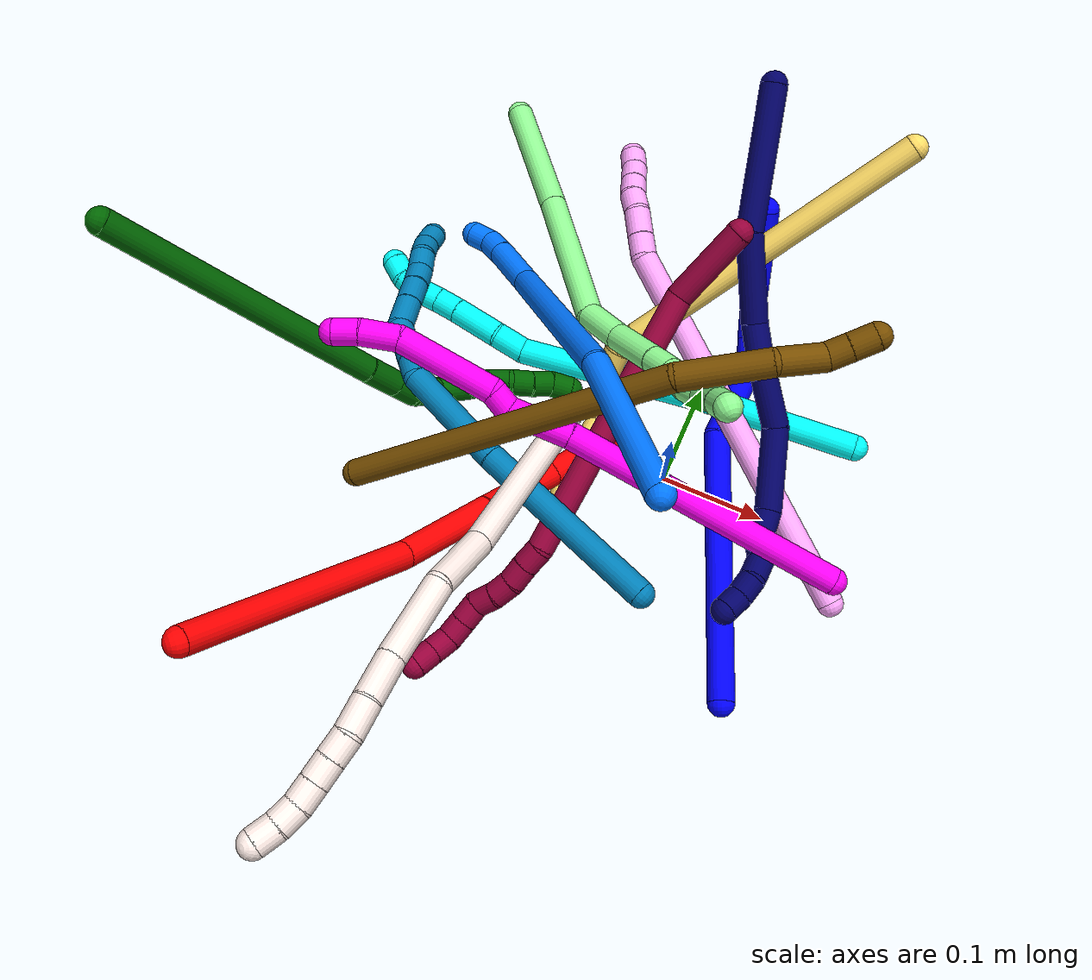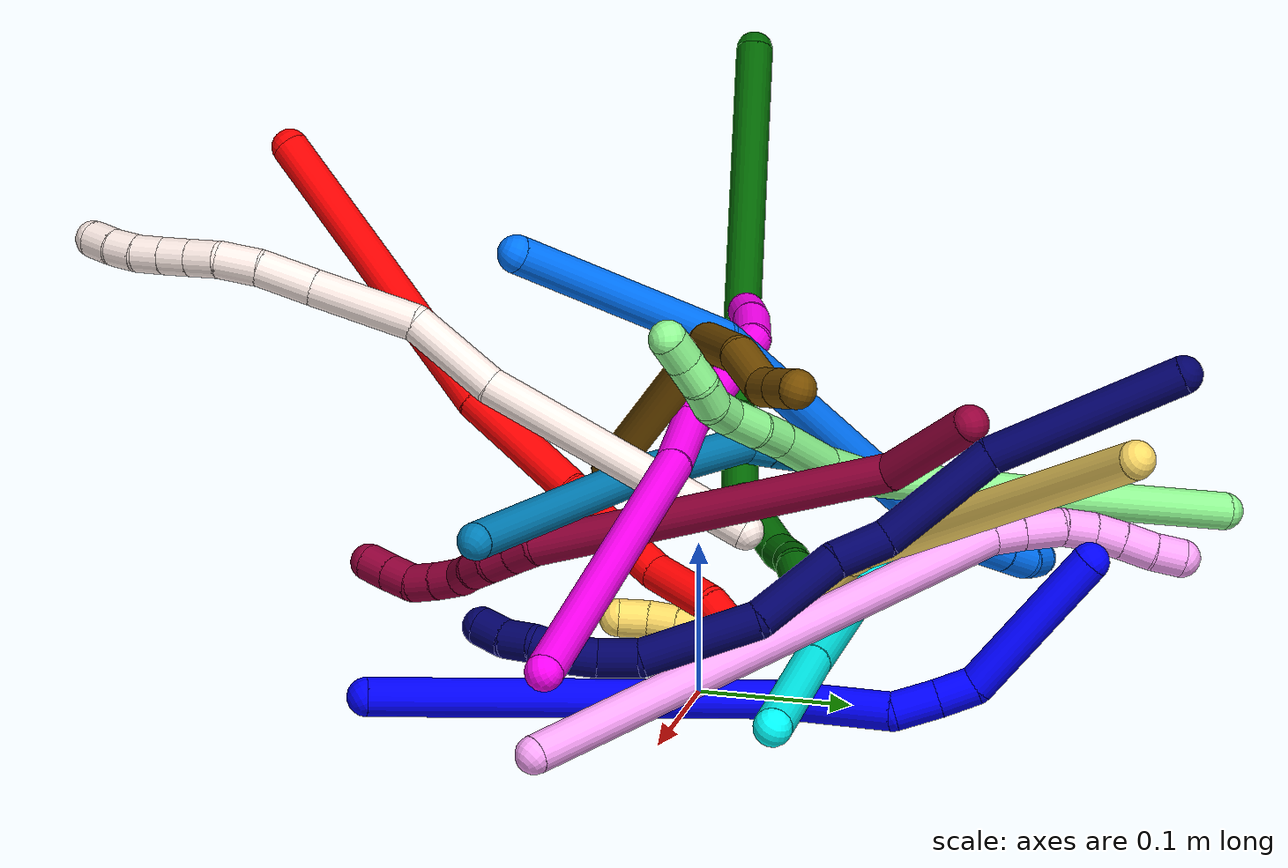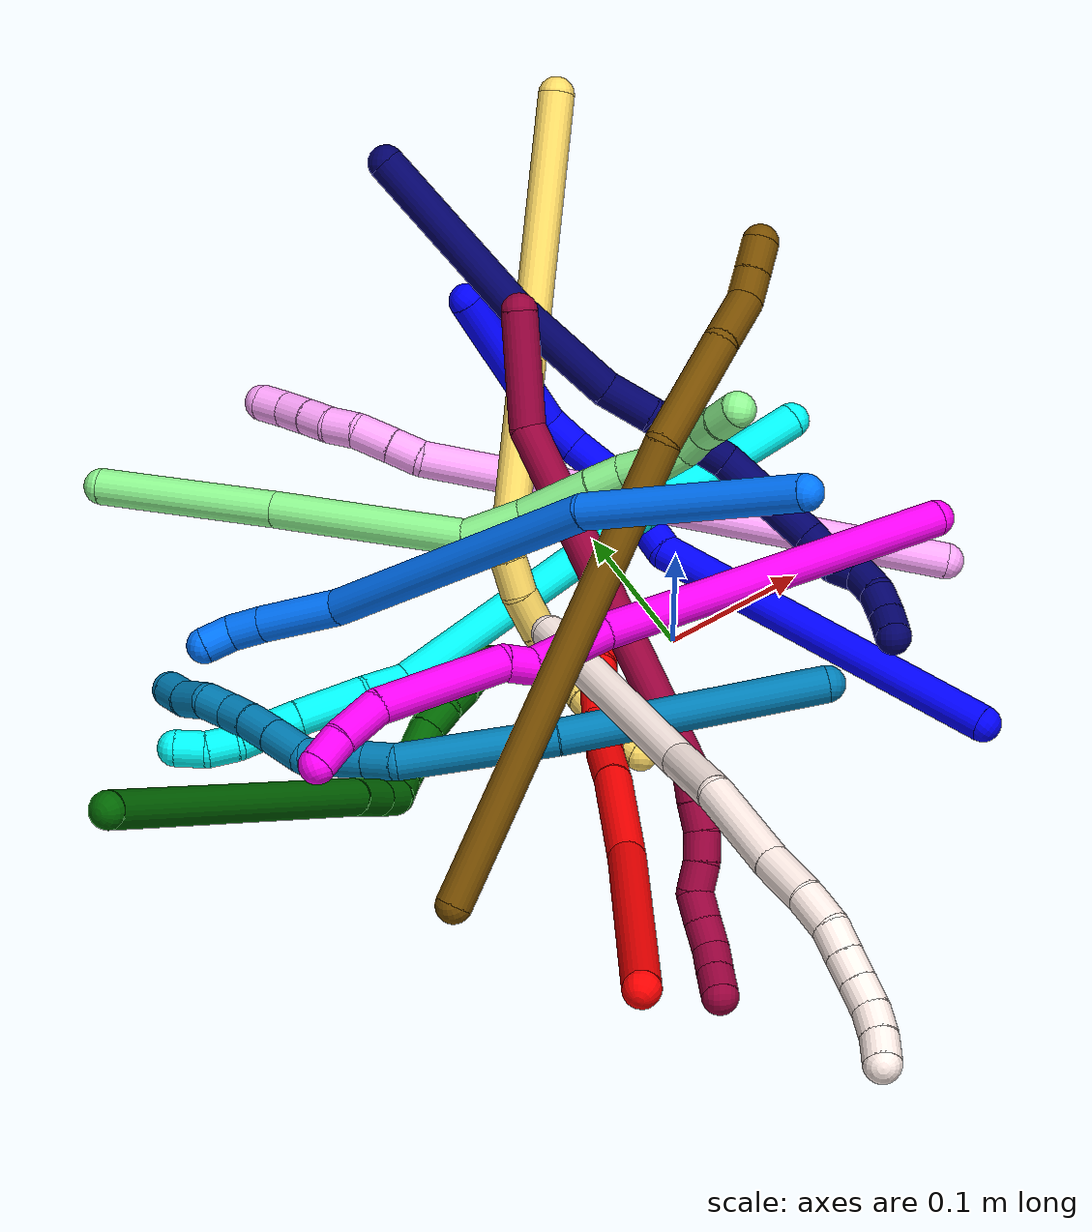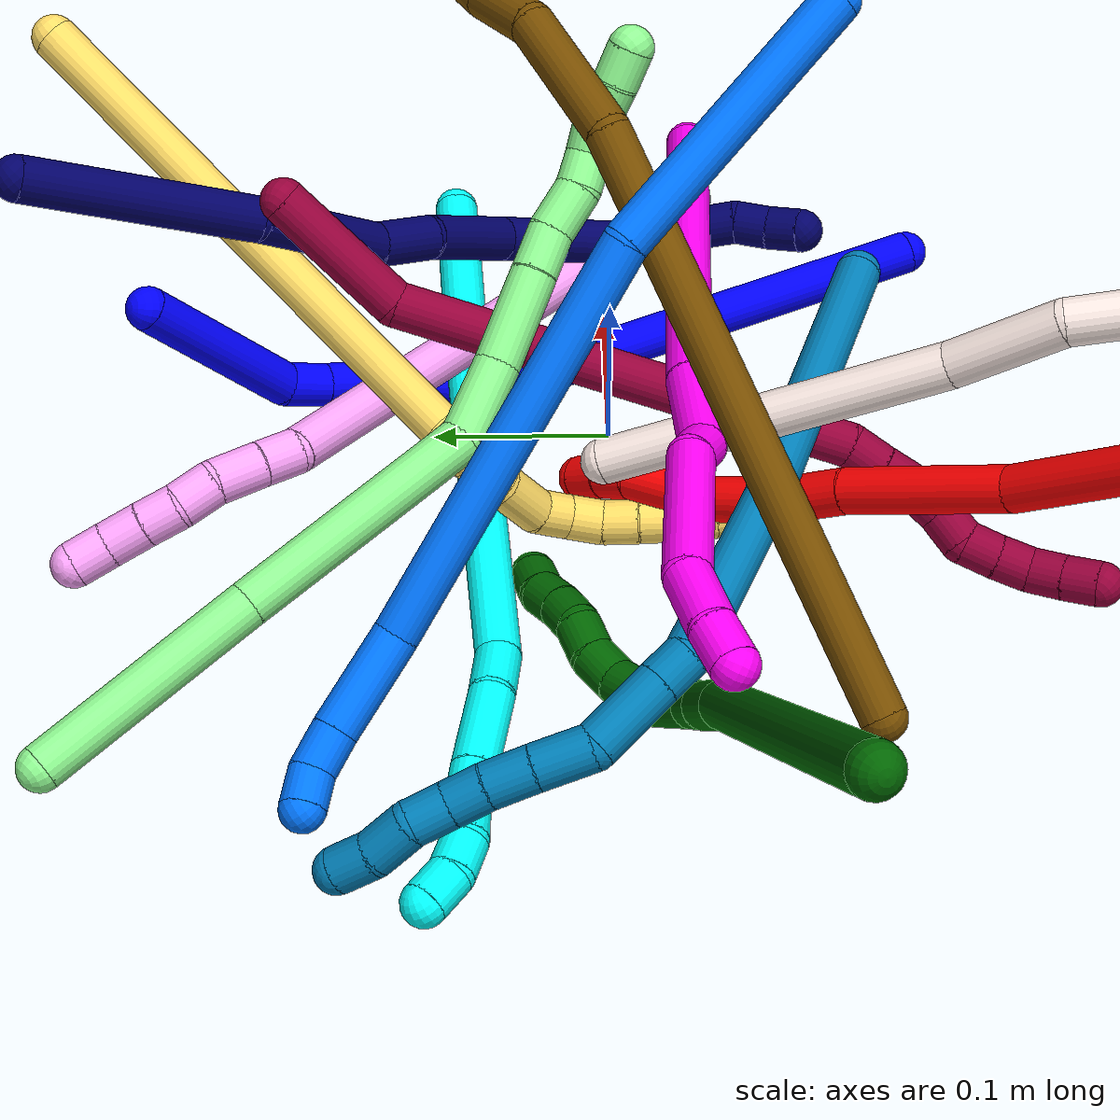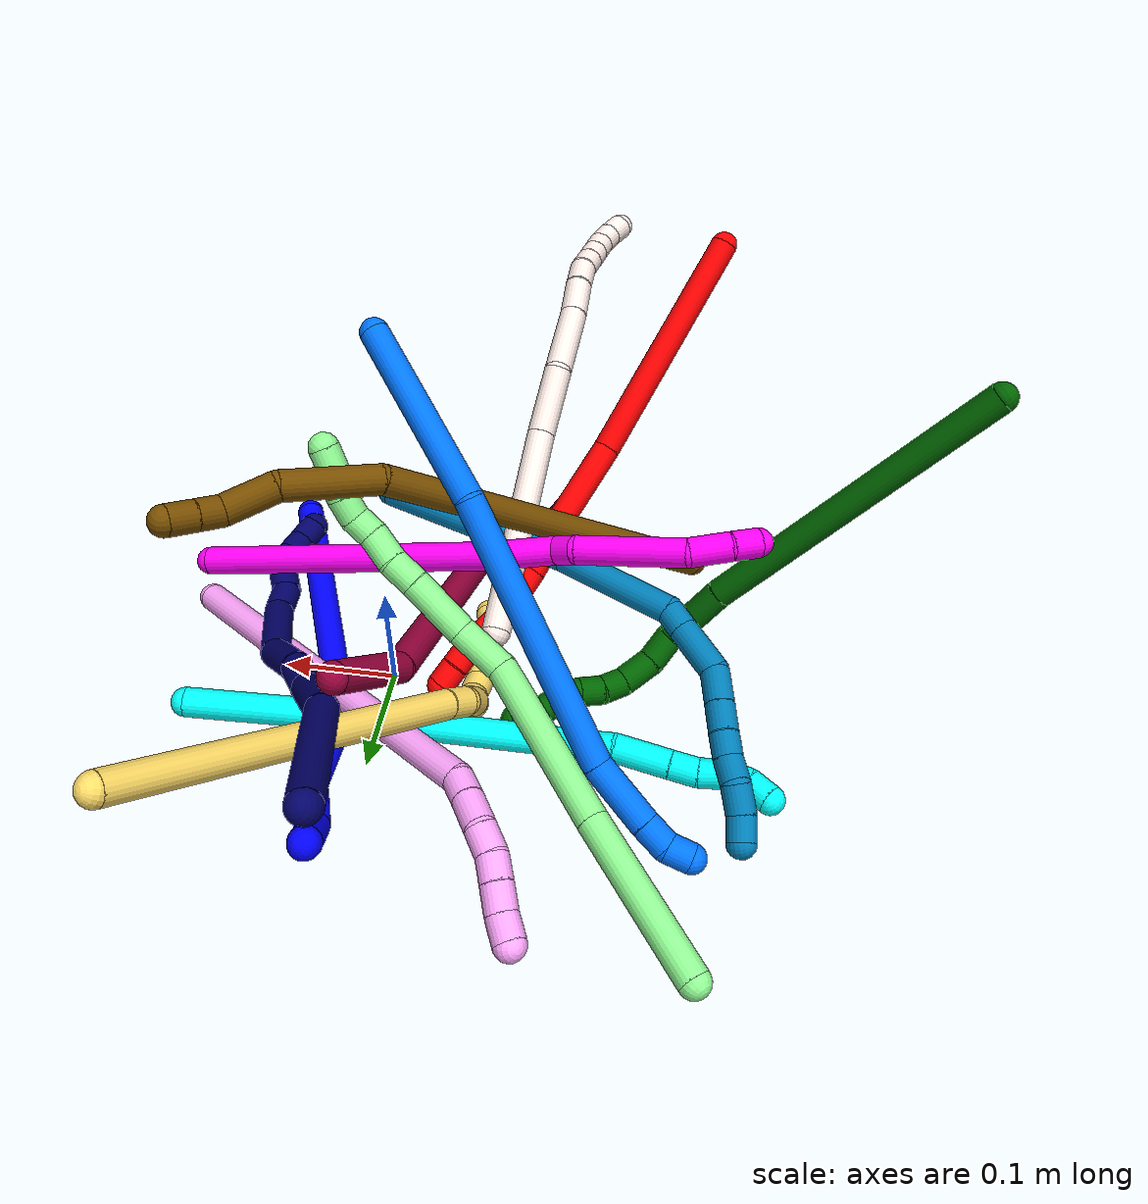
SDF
<sdf version="1.7">
 <world name="default">
  <plugin name="TubeGeneratorPlugin" filename="libtube_generator_plugin.so"/>
  <model name="photoneo_s_sensor">
   <static>1</static>
   <pose>0 0 2 1.57079 1.57079 3.14159</pose>
   <link name="link">
    <inertial><mass>0.1</mass></inertial>
    <sensor name="sensor" type="depth">
     <update_rate>30</update_rate>
     <camera>
      <horizontal_fov>1.22</horizontal_fov>
      <image><width>1920</width><height>1200</height><format>B8G8R8</format></image>
      <clip><near>0.1</near><far>4</far></clip>
      <depth_camera><output>points</output></depth_camera>
     </camera>
     <plugin name="camera_plugin" filename="libgazebo_ros_depth_camera.so">
      <baseline>0.2</baseline>
      <alwaysOn>1</alwaysOn>
      <updateRate>0.0</updateRate>
      <cameraName>camera_ir</cameraName>
      <imageTopicName>/camera/color/image_raw</imageTopicName>
      <cameraInfoTopicName>/camera/color/camera_info</cameraInfoTopicName>
      <depthImageTopicName>/camera/depth/image_raw</depthImageTopicName>
      <depthImageCameraInfoTopicName>/camera/depth/camera_info</depthImageCameraInfoTopicName>
      <pointCloudTopicName>/camera/depth/points</pointCloudTopicName>
      <frameName>fr_optical</frameName>
      <pointCloudCutoff>0.1</pointCloudCutoff>
      <pointCloudCutoffMax>2.0</pointCloudCutoffMax>
      <distortionK1>0</distortionK1>
      <distortionK2>0</distortionK2>
      <distortionK3>0</distortionK3>
      <distortionT1>0</distortionT1>
      <distortionT2>0</distortionT2>
      <CxPrime>0</CxPrime>
      <Cx>0</Cx>
      <Cy>0</Cy>
      <focalLength>0</focalLength>
      <hackBaseline>0</hackBaseline>
     </plugin>
    </sensor>
   </link>
  </model>
  <gravity>0 0 -9.8</gravity>
  <magnetic_field>6e-06 2.3e-05 -4.2e-05</magnetic_field>
  <atmosphere type="adiabatic"/>
  <physics name="default_physics" default="0" type="ode">
   <max_step_size>0.003</max_step_size>
   <real_time_factor>1</real_time_factor>
   <real_time_update_rate>1000</real_time_update_rate>
   <max_contacts>10000</max_contacts>
   <ode>
    <solver>
     <type>quick</type>
     <iters>100</iters>
     <sor>1.3</sor>
     <use_dynamic_moi_rescaling>0</use_dynamic_moi_rescaling>
    </solver>
    <constraints>
     <contact_max_correcting_vel>0</contact_max_correcting_vel>
     <contact_surface_layer>0.001</contact_surface_layer>
     <cfm>0</cfm>
     <erp>0.2</erp>
    </constraints>
   </ode>
  </physics>
  <scene><ambient>0.4 0.4 0.4 1</ambient><background>0.7 0.7 0.7 1</background><shadows>0</shadows></scene>
  <audio><device>default</device></audio>
  <spherical_coordinates>
   <surface_model>EARTH_WGS84</surface_model>
   <latitude_deg>0</latitude_deg>
   <longitude_deg>0</longitude_deg>
   <elevation>0</elevation>
   <heading_deg>0</heading_deg>
  </spherical_coordinates>
  <model name="bin">
   <static>1</static>
   <link name="bottom">
    <collision name="collision-bottom">
     <pose>0 0 -0.01 0 -0 0</pose>
     <geometry><box><size>0.8 0.6 0.02</size></box></geometry>
     <surface>
      <friction><ode><mu>100</mu><mu2>100</mu2></ode></friction>
      <contact><collide_bitmask>65535</collide_bitmask></contact>
     </surface>
    </collision>
   </link>
   <link name="west_wall">
    <collision name="collision-west_wall">
     <pose>-0.41 0 0.1 0 -0 0</pose>
     <geometry><box><size>0.02 0.6 0.2</size></box></geometry>
     <surface>
      <friction><ode><mu>100</mu><mu2>100</mu2></ode></friction>
      <contact><collide_bitmask>65535</collide_bitmask></contact>
     </surface>
    </collision>
   </link>
   <link name="east_wall">
    <collision name="collision-east_wall">
     <pose>0.41 0 0.1 0 -0 0</pose>
     <geometry><box><size>0.02 0.6 0.2</size></box></geometry>
     <surface>
      <friction><ode><mu>100</mu><mu2>100</mu2></ode></friction>
      <contact><collide_bitmask>65535</collide_bitmask></contact>
     </surface>
    </collision>
   </link>
   <link name="south_wall">
    <collision name="collision-south_wall">
     <pose>0 -0.31 0.1 0 -0 0</pose>
     <geometry><box><size>0.8 0.02 0.2</size></box></geometry>
     <surface>
      <friction><ode><mu>100</mu><mu2>100</mu2></ode></friction>
      <contact><collide_bitmask>65535</collide_bitmask></contact>
     </surface>
    </collision>
   </link>
   <link name="north_wall">
    <collision name="collision-north_wall">
     <pose>0 0.31 0.1 0 -0 0</pose>
     <geometry><box><size>0.8 0.02 0.2</size></box></geometry>
     <surface>
      <friction><ode><mu>100</mu><mu2>100</mu2></ode></friction>
      <contact><collide_bitmask>65535</collide_bitmask></contact>
     </surface>
    </collision>
   </link>
  </model>
  <model name="1">
   <static>0</static>
   <link name="1">
    <collision name="collision-cylinder-e_1_1_4">
     <pose>-0.010954 0.064503 0.112461 -0.520752 -0.084293 0.02247</pose>
     <geometry><cylinder><radius>0.0125</radius><length>0.260216</length></cylinder></geometry>
     <surface>
      <friction><ode><mu>1.16</mu><mu2>1.16</mu2><slip1>0</slip1><slip2>0</slip2></ode></friction>
      <contact><ode><kp>1e+06</kp><kd>1</kd><max_vel>0</max_vel><min_depth>0.001</min_depth></ode></contact>
     </surface>
    </collision>
    <visual name="visual-cylinder-e_1_1_4">
     <pose>-0.010954 0.064503 0.112461 -0.520752 -0.084293 0.02247</pose>
     <geometry><cylinder><radius>0.0125</radius><length>0.260216</length></cylinder></geometry>
     <material><ambient>0 0 1 1</ambient></material>
    </visual>
    <collision name="collision-cylinder-e_2_4_5">
     <pose>-0.009129 0.1502 0.254788 -0.617145 0.335745 -0.107932</pose>
     <geometry><cylinder><radius>0.0125</radius><length>0.077577</length></cylinder></geometry>
     <surface>
      <friction><ode><mu>1.16</mu><mu2>1.16</mu2><slip1>0</slip1><slip2>0</slip2></ode></friction>
      <contact><ode><kp>1e+06</kp><kd>1</kd><max_vel>0</max_vel><min_depth>0.001</min_depth></ode></contact>
     </surface>
    </collision>
    <visual name="visual-cylinder-e_2_4_5">
     <pose>-0.009129 0.1502 0.254788 -0.617145 0.335745 -0.107932</pose>
     <geometry><cylinder><radius>0.0125</radius><length>0.077577</length></cylinder></geometry>
     <material><ambient>0 0 1 1</ambient></material>
    </visual>
    <collision name="collision-cylinder-e_3_5_6">
     <pose>0.004182 0.174736 0.299035 -0.228345 0.035945 -0.004122</pose>
     <geometry><cylinder><radius>0.0125</radius><length>0.029544</length></cylinder></geometry>
     <surface>
      <friction><ode><mu>1.16</mu><mu2>1.16</mu2><slip1>0</slip1><slip2>0</slip2></ode></friction>
      <contact><ode><kp>1e+06</kp><kd>1</kd><max_vel>0</max_vel><min_depth>0.001</min_depth></ode></contact>
     </surface>
    </collision>
    <visual name="visual-cylinder-e_3_5_6">
     <pose>0.004182 0.174736 0.299035 -0.228345 0.035945 -0.004122</pose>
     <geometry><cylinder><radius>0.0125</radius><length>0.029544</length></cylinder></geometry>
     <material><ambient>0 0 1 1</ambient></material>
    </visual>
    <collision name="collision-cylinder-e_4_6_7">
     <pose>0.005878 0.180184 0.325742 -0.169281 0.092932 -0.00789</pose>
     <geometry><cylinder><radius>0.0125</radius><length>0.025123</length></cylinder></geometry>
     <surface>
      <friction><ode><mu>1.16</mu><mu2>1.16</mu2><slip1>0</slip1><slip2>0</slip2></ode></friction>
      <contact><ode><kp>1e+06</kp><kd>1</kd><max_vel>0</max_vel><min_depth>0.001</min_depth></ode></contact>
     </surface>
    </collision>
    <visual name="visual-cylinder-e_4_6_7">
     <pose>0.005878 0.180184 0.325742 -0.169281 0.092932 -0.00789</pose>
     <geometry><cylinder><radius>0.0125</radius><length>0.025123</length></cylinder></geometry>
     <material><ambient>0 0 1 1</ambient></material>
    </visual>
    <collision name="collision-cylinder-e_5_7_2">
     <pose>0.019838 0.165661 0.387578 0.32408 0.240246 0.039459</pose>
     <geometry><cylinder><radius>0.0125</radius><length>0.107541</length></cylinder></geometry>
     <surface>
      <friction><ode><mu>1.16</mu><mu2>1.16</mu2><slip1>0</slip1><slip2>0</slip2></ode></friction>
      <contact><ode><kp>1e+06</kp><kd>1</kd><max_vel>0</max_vel><min_depth>0.001</min_depth></ode></contact>
     </surface>
    </collision>
    <visual name="visual-cylinder-e_5_7_2">
     <pose>0.019838 0.165661 0.387578 0.32408 0.240246 0.039459</pose>
     <geometry><cylinder><radius>0.0125</radius><length>0.107541</length></cylinder></geometry>
     <material><ambient>0 0 1 1</ambient></material>
    </visual>
    <collision name="collision-sphere-2">
     <pose>0.032633 0.14903 0.437086 0 -0 0</pose>
     <geometry><sphere><radius>0.0125</radius></sphere></geometry>
     <surface>
      <friction><ode><mu>1.16</mu><mu2>1.16</mu2><slip1>0</slip1><slip2>0</slip2></ode></friction>
      <contact><ode><kp>1e+06</kp><kd>1</kd><max_vel>0</max_vel><min_depth>0.001</min_depth></ode></contact>
     </surface>
    </collision>
    <visual name="visual-sphere-2">
     <pose>0.032633 0.14903 0.437086 0 -0 0</pose>
     <geometry><sphere><radius>0.0125</radius></sphere></geometry>
     <material><ambient>0 0 1 1</ambient></material>
    </visual>
    <collision name="collision-sphere-7">
     <pose>0.007044 0.182292 0.338071 0 -0 0</pose>
     <geometry><sphere><radius>0.0125</radius></sphere></geometry>
     <surface>
      <friction><ode><mu>1.16</mu><mu2>1.16</mu2><slip1>0</slip1><slip2>0</slip2></ode></friction>
      <contact><ode><kp>1e+06</kp><kd>1</kd><max_vel>0</max_vel><min_depth>0.001</min_depth></ode></contact>
     </surface>
    </collision>
    <visual name="visual-sphere-7">
     <pose>0.007044 0.182292 0.338071 0 -0 0</pose>
     <geometry><sphere><radius>0.0125</radius></sphere></geometry>
     <material><ambient>0 0 1 1</ambient></material>
    </visual>
    <collision name="collision-sphere-6">
     <pose>0.004713 0.178077 0.313414 0 -0 0</pose>
     <geometry><sphere><radius>0.0125</radius></sphere></geometry>
     <surface>
      <friction><ode><mu>1.16</mu><mu2>1.16</mu2><slip1>0</slip1><slip2>0</slip2></ode></friction>
      <contact><ode><kp>1e+06</kp><kd>1</kd><max_vel>0</max_vel><min_depth>0.001</min_depth></ode></contact>
     </surface>
    </collision>
    <visual name="visual-sphere-6">
     <pose>0.004713 0.178077 0.313414 0 -0 0</pose>
     <geometry><sphere><radius>0.0125</radius></sphere></geometry>
     <material><ambient>0 0 1 1</ambient></material>
    </visual>
    <collision name="collision-sphere-5">
     <pose>0.003651 0.171394 0.284655 0 -0 0</pose>
     <geometry><sphere><radius>0.0125</radius></sphere></geometry>
     <surface>
      <friction><ode><mu>1.16</mu><mu2>1.16</mu2><slip1>0</slip1><slip2>0</slip2></ode></friction>
      <contact><ode><kp>1e+06</kp><kd>1</kd><max_vel>0</max_vel><min_depth>0.001</min_depth></ode></contact>
     </surface>
    </collision>
    <visual name="visual-sphere-5">
     <pose>0.003651 0.171394 0.284655 0 -0 0</pose>
     <geometry><sphere><radius>0.0125</radius></sphere></geometry>
     <material><ambient>0 0 1 1</ambient></material>
    </visual>
    <collision name="collision-sphere-1">
     <geometry><sphere><radius>0.0125</radius></sphere></geometry>
     <surface>
      <friction><ode><mu>1.16</mu><mu2>1.16</mu2><slip1>0</slip1><slip2>0</slip2></ode></friction>
      <contact><ode><kp>1e+06</kp><kd>1</kd><max_vel>0</max_vel><min_depth>0.001</min_depth></ode></contact>
     </surface>
    </collision>
    <visual name="visual-sphere-1">
     <geometry><sphere><radius>0.0125</radius></sphere></geometry>
     <material><ambient>0 0 1 1</ambient></material>
    </visual>
    <collision name="collision-sphere-4">
     <pose>-0.021908 0.129006 0.224921 0 -0 0</pose>
     <geometry><sphere><radius>0.0125</radius></sphere></geometry>
     <surface>
      <friction><ode><mu>1.16</mu><mu2>1.16</mu2><slip1>0</slip1><slip2>0</slip2></ode></friction>
      <contact><ode><kp>1e+06</kp><kd>1</kd><max_vel>0</max_vel><min_depth>0.001</min_depth></ode></contact>
     </surface>
    </collision>
    <visual name="visual-sphere-4">
     <pose>-0.021908 0.129006 0.224921 0 -0 0</pose>
     <geometry><sphere><radius>0.0125</radius></sphere></geometry>
     <material><ambient>0 0 1 1</ambient></material>
    </visual>
    <inertial>
     <pose>-0.002308 0.111882 0.215457 0 -0 0</pose>
     <mass>0.5</mass>
     <inertia>
      <ixx>0.001658</ixx>
      <ixy>0</ixy>
      <ixz>0</ixz>
      <iyy>0.001471</iyy>
      <iyz>0</iyz>
      <izz>-0.000605</izz>
     </inertia>
    </inertial>
   </link>
   <pose>0.128129 -0.182706 0.024771 -1.07408 -0.345266 0.30941</pose>
  </model>
  <model name="2">
   <static>0</static>
   <link name="2">
    <collision name="collision-cylinder-e_1_1_4">
     <pose>0.029552 -0.036676 -0.103546 2.80118 0.262799 1.31106</pose>
     <geometry><cylinder><radius>0.0125</radius><length>0.227509</length></cylinder></geometry>
     <surface>
      <friction><ode><mu>1.16</mu><mu2>1.16</mu2><slip1>0</slip1><slip2>0</slip2></ode></friction>
      <contact><ode><kp>1e+06</kp><kd>1</kd><max_vel>0</max_vel><min_depth>0.001</min_depth></ode></contact>
     </surface>
    </collision>
    <visual name="visual-cylinder-e_1_1_4">
     <pose>0.029552 -0.036676 -0.103546 2.80118 0.262799 1.31106</pose>
     <geometry><cylinder><radius>0.0125</radius><length>0.227509</length></cylinder></geometry>
     <material><ambient>1 0 0 1</ambient></material>
    </visual>
    <collision name="collision-cylinder-e_2_4_5">
     <pose>0.061602 -0.088009 -0.252565 2.82978 0.052256 0.329516</pose>
     <geometry><cylinder><radius>0.0125</radius><length>0.095686</length></cylinder></geometry>
     <surface>
      <friction><ode><mu>1.16</mu><mu2>1.16</mu2><slip1>0</slip1><slip2>0</slip2></ode></friction>
      <contact><ode><kp>1e+06</kp><kd>1</kd><max_vel>0</max_vel><min_depth>0.001</min_depth></ode></contact>
     </surface>
    </collision>
    <visual name="visual-cylinder-e_2_4_5">
     <pose>0.061602 -0.088009 -0.252565 2.82978 0.052256 0.329516</pose>
     <geometry><cylinder><radius>0.0125</radius><length>0.095686</length></cylinder></geometry>
     <material><ambient>1 0 0 1</ambient></material>
    </visual>
    <collision name="collision-cylinder-e_3_5_6">
     <pose>0.06745 -0.110586 -0.317532 2.7557 0.157833 0.769215</pose>
     <geometry><cylinder><radius>0.0125</radius><length>0.04261</length></cylinder></geometry>
     <surface>
      <friction><ode><mu>1.16</mu><mu2>1.16</mu2><slip1>0</slip1><slip2>0</slip2></ode></friction>
      <contact><ode><kp>1e+06</kp><kd>1</kd><max_vel>0</max_vel><min_depth>0.001</min_depth></ode></contact>
     </surface>
    </collision>
    <visual name="visual-cylinder-e_3_5_6">
     <pose>0.06745 -0.110586 -0.317532 2.7557 0.157833 0.769215</pose>
     <geometry><cylinder><radius>0.0125</radius><length>0.04261</length></cylinder></geometry>
     <material><ambient>1 0 0 1</ambient></material>
    </visual>
    <collision name="collision-cylinder-e_4_6_7">
     <pose>0.071557 -0.124767 -0.357898 2.85013 0.034801 0.236033</pose>
     <geometry><cylinder><radius>0.0125</radius><length>0.043609</length></cylinder></geometry>
     <surface>
      <friction><ode><mu>1.16</mu><mu2>1.16</mu2><slip1>0</slip1><slip2>0</slip2></ode></friction>
      <contact><ode><kp>1e+06</kp><kd>1</kd><max_vel>0</max_vel><min_depth>0.001</min_depth></ode></contact>
     </surface>
    </collision>
    <visual name="visual-cylinder-e_4_6_7">
     <pose>0.071557 -0.124767 -0.357898 2.85013 0.034801 0.236033</pose>
     <geometry><cylinder><radius>0.0125</radius><length>0.043609</length></cylinder></geometry>
     <material><ambient>1 0 0 1</ambient></material>
    </visual>
    <collision name="collision-cylinder-e_5_7_8">
     <pose>0.067951 -0.134702 -0.403278 2.99281 -0.174331 -1.72926</pose>
     <geometry><cylinder><radius>0.0125</radius><length>0.050327</length></cylinder></geometry>
     <surface>
      <friction><ode><mu>1.16</mu><mu2>1.16</mu2><slip1>0</slip1><slip2>0</slip2></ode></friction>
      <contact><ode><kp>1e+06</kp><kd>1</kd><max_vel>0</max_vel><min_depth>0.001</min_depth></ode></contact>
     </surface>
    </collision>
    <visual name="visual-cylinder-e_5_7_8">
     <pose>0.067951 -0.134702 -0.403278 2.99281 -0.174331 -1.72926</pose>
     <geometry><cylinder><radius>0.0125</radius><length>0.050327</length></cylinder></geometry>
     <material><ambient>1 0 0 1</ambient></material>
    </visual>
    <collision name="collision-cylinder-e_6_8_9">
     <pose>0.065116 -0.140553 -0.437444 2.91989 0.153281 1.20785</pose>
     <geometry><cylinder><radius>0.0125</radius><length>0.020035</length></cylinder></geometry>
     <surface>
      <friction><ode><mu>1.16</mu><mu2>1.16</mu2><slip1>0</slip1><slip2>0</slip2></ode></friction>
      <contact><ode><kp>1e+06</kp><kd>1</kd><max_vel>0</max_vel><min_depth>0.001</min_depth></ode></contact>
     </surface>
    </collision>
    <visual name="visual-cylinder-e_6_8_9">
     <pose>0.065116 -0.140553 -0.437444 2.91989 0.153281 1.20785</pose>
     <geometry><cylinder><radius>0.0125</radius><length>0.020035</length></cylinder></geometry>
     <material><ambient>1 0 0 1</ambient></material>
    </visual>
    <collision name="collision-cylinder-e_7_9_2">
     <pose>0.069306 -0.144835 -0.456627 2.92401 0.266212 1.77307</pose>
     <geometry><cylinder><radius>0.0125</radius><length>0.020223</length></cylinder></geometry>
     <surface>
      <friction><ode><mu>1.16</mu><mu2>1.16</mu2><slip1>0</slip1><slip2>0</slip2></ode></friction>
      <contact><ode><kp>1e+06</kp><kd>1</kd><max_vel>0</max_vel><min_depth>0.001</min_depth></ode></contact>
     </surface>
    </collision>
    <visual name="visual-cylinder-e_7_9_2">
     <pose>0.069306 -0.144835 -0.456627 2.92401 0.266212 1.77307</pose>
     <geometry><cylinder><radius>0.0125</radius><length>0.020223</length></cylinder></geometry>
     <material><ambient>1 0 0 1</ambient></material>
    </visual>
    <collision name="collision-sphere-2">
     <pose>0.071966 -0.146941 -0.466153 0 -0 0</pose>
     <geometry><sphere><radius>0.0125</radius></sphere></geometry>
     <surface>
      <friction><ode><mu>1.16</mu><mu2>1.16</mu2><slip1>0</slip1><slip2>0</slip2></ode></friction>
      <contact><ode><kp>1e+06</kp><kd>1</kd><max_vel>0</max_vel><min_depth>0.001</min_depth></ode></contact>
     </surface>
    </collision>
    <visual name="visual-sphere-2">
     <pose>0.071966 -0.146941 -0.466153 0 -0 0</pose>
     <geometry><sphere><radius>0.0125</radius></sphere></geometry>
     <material><ambient>1 0 0 1</ambient></material>
    </visual>
    <collision name="collision-sphere-9">
     <pose>0.066646 -0.142729 -0.447102 0 -0 0</pose>
     <geometry><sphere><radius>0.0125</radius></sphere></geometry>
     <surface>
      <friction><ode><mu>1.16</mu><mu2>1.16</mu2><slip1>0</slip1><slip2>0</slip2></ode></friction>
      <contact><ode><kp>1e+06</kp><kd>1</kd><max_vel>0</max_vel><min_depth>0.001</min_depth></ode></contact>
     </surface>
    </collision>
    <visual name="visual-sphere-9">
     <pose>0.066646 -0.142729 -0.447102 0 -0 0</pose>
     <geometry><sphere><radius>0.0125</radius></sphere></geometry>
     <material><ambient>1 0 0 1</ambient></material>
    </visual>
    <collision name="collision-sphere-4">
     <pose>0.059103 -0.073352 -0.207091 0 -0 0</pose>
     <geometry><sphere><radius>0.0125</radius></sphere></geometry>
     <surface>
      <friction><ode><mu>1.16</mu><mu2>1.16</mu2><slip1>0</slip1><slip2>0</slip2></ode></friction>
      <contact><ode><kp>1e+06</kp><kd>1</kd><max_vel>0</max_vel><min_depth>0.001</min_depth></ode></contact>
     </surface>
    </collision>
    <visual name="visual-sphere-4">
     <pose>0.059103 -0.073352 -0.207091 0 -0 0</pose>
     <geometry><sphere><radius>0.0125</radius></sphere></geometry>
     <material><ambient>1 0 0 1</ambient></material>
    </visual>
    <collision name="collision-sphere-1">
     <geometry><sphere><radius>0.0125</radius></sphere></geometry>
     <surface>
      <friction><ode><mu>1.16</mu><mu2>1.16</mu2><slip1>0</slip1><slip2>0</slip2></ode></friction>
      <contact><ode><kp>1e+06</kp><kd>1</kd><max_vel>0</max_vel><min_depth>0.001</min_depth></ode></contact>
     </surface>
    </collision>
    <visual name="visual-sphere-1">
     <geometry><sphere><radius>0.0125</radius></sphere></geometry>
     <material><ambient>1 0 0 1</ambient></material>
    </visual>
    <collision name="collision-sphere-8">
     <pose>0.063587 -0.138376 -0.427786 0 -0 0</pose>
     <geometry><sphere><radius>0.0125</radius></sphere></geometry>
     <surface>
      <friction><ode><mu>1.16</mu><mu2>1.16</mu2><slip1>0</slip1><slip2>0</slip2></ode></friction>
      <contact><ode><kp>1e+06</kp><kd>1</kd><max_vel>0</max_vel><min_depth>0.001</min_depth></ode></contact>
     </surface>
    </collision>
    <visual name="visual-sphere-8">
     <pose>0.063587 -0.138376 -0.427786 0 -0 0</pose>
     <geometry><sphere><radius>0.0125</radius></sphere></geometry>
     <material><ambient>1 0 0 1</ambient></material>
    </visual>
    <collision name="collision-sphere-5">
     <pose>0.064101 -0.102667 -0.298039 0 -0 0</pose>
     <geometry><sphere><radius>0.0125</radius></sphere></geometry>
     <surface>
      <friction><ode><mu>1.16</mu><mu2>1.16</mu2><slip1>0</slip1><slip2>0</slip2></ode></friction>
      <contact><ode><kp>1e+06</kp><kd>1</kd><max_vel>0</max_vel><min_depth>0.001</min_depth></ode></contact>
     </surface>
    </collision>
    <visual name="visual-sphere-5">
     <pose>0.064101 -0.102667 -0.298039 0 -0 0</pose>
     <geometry><sphere><radius>0.0125</radius></sphere></geometry>
     <material><ambient>1 0 0 1</ambient></material>
    </visual>
    <collision name="collision-sphere-6">
     <pose>0.070799 -0.118505 -0.337025 0 -0 0</pose>
     <geometry><sphere><radius>0.0125</radius></sphere></geometry>
     <surface>
      <friction><ode><mu>1.16</mu><mu2>1.16</mu2><slip1>0</slip1><slip2>0</slip2></ode></friction>
      <contact><ode><kp>1e+06</kp><kd>1</kd><max_vel>0</max_vel><min_depth>0.001</min_depth></ode></contact>
     </surface>
    </collision>
    <visual name="visual-sphere-6">
     <pose>0.070799 -0.118505 -0.337025 0 -0 0</pose>
     <geometry><sphere><radius>0.0125</radius></sphere></geometry>
     <material><ambient>1 0 0 1</ambient></material>
    </visual>
    <collision name="collision-sphere-7">
     <pose>0.072316 -0.131028 -0.37877 0 -0 0</pose>
     <geometry><sphere><radius>0.0125</radius></sphere></geometry>
     <surface>
      <friction><ode><mu>1.16</mu><mu2>1.16</mu2><slip1>0</slip1><slip2>0</slip2></ode></friction>
      <contact><ode><kp>1e+06</kp><kd>1</kd><max_vel>0</max_vel><min_depth>0.001</min_depth></ode></contact>
     </surface>
    </collision>
    <visual name="visual-sphere-7">
     <pose>0.072316 -0.131028 -0.37877 0 -0 0</pose>
     <geometry><sphere><radius>0.0125</radius></sphere></geometry>
     <material><ambient>1 0 0 1</ambient></material>
    </visual>
    <inertial>
     <pose>0.049477 -0.078885 -0.230314 0 -0 0</pose>
     <mass>0.5</mass>
     <inertia>
      <ixx>0.001283</ixx>
      <ixy>0</ixy>
      <ixz>0</ixz>
      <iyy>0.000699</iyy>
      <iyz>0</iyz>
      <izz>5.3e-05</izz>
     </inertia>
    </inertial>
   </link>
   <pose>-0.260994 -0.352629 0.263068 1.00253 1.04981 -1.26838</pose>
  </model>
  <model name="3">
   <static>0</static>
   <link name="3">
    <collision name="collision-cylinder-e_1_1_4">
     <pose>-0.057579 -0.01938 0.023783 0.683741 -1.08124 -0.420883</pose>
     <geometry><cylinder><radius>0.0125</radius><length>0.130484</length></cylinder></geometry>
     <surface>
      <friction><ode><mu>1.16</mu><mu2>1.16</mu2><slip1>0</slip1><slip2>0</slip2></ode></friction>
      <contact><ode><kp>1e+06</kp><kd>1</kd><max_vel>0</max_vel><min_depth>0.001</min_depth></ode></contact>
     </surface>
    </collision>
    <visual name="visual-cylinder-e_1_1_4">
     <pose>-0.057579 -0.01938 0.023783 0.683741 -1.08124 -0.420883</pose>
     <geometry><cylinder><radius>0.0125</radius><length>0.130484</length></cylinder></geometry>
     <material><ambient>0.003922 1 0.996078 1</ambient></material>
    </visual>
    <collision name="collision-cylinder-e_2_4_5">
     <pose>-0.201052 -0.069261 0.091883 0.602794 -1.01122 -0.340861</pose>
     <geometry><cylinder><radius>0.0125</radius><length>0.202705</length></cylinder></geometry>
     <surface>
      <friction><ode><mu>1.16</mu><mu2>1.16</mu2><slip1>0</slip1><slip2>0</slip2></ode></friction>
      <contact><ode><kp>1e+06</kp><kd>1</kd><max_vel>0</max_vel><min_depth>0.001</min_depth></ode></contact>
     </surface>
    </collision>
    <visual name="visual-cylinder-e_2_4_5">
     <pose>-0.201052 -0.069261 0.091883 0.602794 -1.01122 -0.340861</pose>
     <geometry><cylinder><radius>0.0125</radius><length>0.202705</length></cylinder></geometry>
     <material><ambient>0.003922 1 0.996078 1</ambient></material>
    </visual>
    <collision name="collision-cylinder-e_3_5_6">
     <pose>-0.301008 -0.105442 0.138073 1.25239 -1.16876 -0.892481</pose>
     <geometry><cylinder><radius>0.0125</radius><length>0.030561</length></cylinder></geometry>
     <surface>
      <friction><ode><mu>1.16</mu><mu2>1.16</mu2><slip1>0</slip1><slip2>0</slip2></ode></friction>
      <contact><ode><kp>1e+06</kp><kd>1</kd><max_vel>0</max_vel><min_depth>0.001</min_depth></ode></contact>
     </surface>
    </collision>
    <visual name="visual-cylinder-e_3_5_6">
     <pose>-0.301008 -0.105442 0.138073 1.25239 -1.16876 -0.892481</pose>
     <geometry><cylinder><radius>0.0125</radius><length>0.030561</length></cylinder></geometry>
     <material><ambient>0.003922 1 0.996078 1</ambient></material>
    </visual>
    <collision name="collision-cylinder-e_4_6_7">
     <pose>-0.33473 -0.123445 0.14622 1.09987 -0.957755 -0.616264</pose>
     <geometry><cylinder><radius>0.0125</radius><length>0.048074</length></cylinder></geometry>
     <surface>
      <friction><ode><mu>1.16</mu><mu2>1.16</mu2><slip1>0</slip1><slip2>0</slip2></ode></friction>
      <contact><ode><kp>1e+06</kp><kd>1</kd><max_vel>0</max_vel><min_depth>0.001</min_depth></ode></contact>
     </surface>
    </collision>
    <visual name="visual-cylinder-e_4_6_7">
     <pose>-0.33473 -0.123445 0.14622 1.09987 -0.957755 -0.616264</pose>
     <geometry><cylinder><radius>0.0125</radius><length>0.048074</length></cylinder></geometry>
     <material><ambient>0.003922 1 0.996078 1</ambient></material>
    </visual>
    <collision name="collision-cylinder-e_5_7_8">
     <pose>-0.364206 -0.141739 0.155985 1.04165 -0.957096 -0.578499</pose>
     <geometry><cylinder><radius>0.0125</radius><length>0.024016</length></cylinder></geometry>
     <surface>
      <friction><ode><mu>1.16</mu><mu2>1.16</mu2><slip1>0</slip1><slip2>0</slip2></ode></friction>
      <contact><ode><kp>1e+06</kp><kd>1</kd><max_vel>0</max_vel><min_depth>0.001</min_depth></ode></contact>
     </surface>
    </collision>
    <visual name="visual-cylinder-e_5_7_8">
     <pose>-0.364206 -0.141739 0.155985 1.04165 -0.957096 -0.578499</pose>
     <geometry><cylinder><radius>0.0125</radius><length>0.024016</length></cylinder></geometry>
     <material><ambient>0.003922 1 0.996078 1</ambient></material>
    </visual>
    <collision name="collision-cylinder-e_6_8_9">
     <pose>-0.384418 -0.151095 0.161516 1.02881 -1.20735 -0.743195</pose>
     <geometry><cylinder><radius>0.0125</radius><length>0.022242</length></cylinder></geometry>
     <surface>
      <friction><ode><mu>1.16</mu><mu2>1.16</mu2><slip1>0</slip1><slip2>0</slip2></ode></friction>
      <contact><ode><kp>1e+06</kp><kd>1</kd><max_vel>0</max_vel><min_depth>0.001</min_depth></ode></contact>
     </surface>
    </collision>
    <visual name="visual-cylinder-e_6_8_9">
     <pose>-0.384418 -0.151095 0.161516 1.02881 -1.20735 -0.743195</pose>
     <geometry><cylinder><radius>0.0125</radius><length>0.022242</length></cylinder></geometry>
     <material><ambient>0.003922 1 0.996078 1</ambient></material>
    </visual>
    <collision name="collision-cylinder-e_7_9_10">
     <pose>-0.402946 -0.160738 0.165243 1.30726 -0.898105 -0.70718</pose>
     <geometry><cylinder><radius>0.0125</radius><length>0.0208</length></cylinder></geometry>
     <surface>
      <friction><ode><mu>1.16</mu><mu2>1.16</mu2><slip1>0</slip1><slip2>0</slip2></ode></friction>
      <contact><ode><kp>1e+06</kp><kd>1</kd><max_vel>0</max_vel><min_depth>0.001</min_depth></ode></contact>
     </surface>
    </collision>
    <visual name="visual-cylinder-e_7_9_10">
     <pose>-0.402946 -0.160738 0.165243 1.30726 -0.898105 -0.70718</pose>
     <geometry><cylinder><radius>0.0125</radius><length>0.0208</length></cylinder></geometry>
     <material><ambient>0.003922 1 0.996078 1</ambient></material>
    </visual>
    <collision name="collision-cylinder-e_8_10_2">
     <pose>-0.417102 -0.175668 0.167026 1.55984 -0.606838 -0.600618</pose>
     <geometry><cylinder><radius>0.0125</radius><length>0.02112</length></cylinder></geometry>
     <surface>
      <friction><ode><mu>1.16</mu><mu2>1.16</mu2><slip1>0</slip1><slip2>0</slip2></ode></friction>
      <contact><ode><kp>1e+06</kp><kd>1</kd><max_vel>0</max_vel><min_depth>0.001</min_depth></ode></contact>
     </surface>
    </collision>
    <visual name="visual-cylinder-e_8_10_2">
     <pose>-0.417102 -0.175668 0.167026 1.55984 -0.606838 -0.600618</pose>
     <geometry><cylinder><radius>0.0125</radius><length>0.02112</length></cylinder></geometry>
     <material><ambient>0.003922 1 0.996078 1</ambient></material>
    </visual>
    <collision name="collision-sphere-2">
     <pose>-0.423125 -0.184343 0.167121 0 -0 0</pose>
     <geometry><sphere><radius>0.0125</radius></sphere></geometry>
     <surface>
      <friction><ode><mu>1.16</mu><mu2>1.16</mu2><slip1>0</slip1><slip2>0</slip2></ode></friction>
      <contact><ode><kp>1e+06</kp><kd>1</kd><max_vel>0</max_vel><min_depth>0.001</min_depth></ode></contact>
     </surface>
    </collision>
    <visual name="visual-sphere-2">
     <pose>-0.423125 -0.184343 0.167121 0 -0 0</pose>
     <geometry><sphere><radius>0.0125</radius></sphere></geometry>
     <material><ambient>0.003922 1 0.996078 1</ambient></material>
    </visual>
    <collision name="collision-sphere-10">
     <pose>-0.41108 -0.166994 0.166931 0 -0 0</pose>
     <geometry><sphere><radius>0.0125</radius></sphere></geometry>
     <surface>
      <friction><ode><mu>1.16</mu><mu2>1.16</mu2><slip1>0</slip1><slip2>0</slip2></ode></friction>
      <contact><ode><kp>1e+06</kp><kd>1</kd><max_vel>0</max_vel><min_depth>0.001</min_depth></ode></contact>
     </surface>
    </collision>
    <visual name="visual-sphere-10">
     <pose>-0.41108 -0.166994 0.166931 0 -0 0</pose>
     <geometry><sphere><radius>0.0125</radius></sphere></geometry>
     <material><ambient>0.003922 1 0.996078 1</ambient></material>
    </visual>
    <collision name="collision-sphere-9">
     <pose>-0.394812 -0.154482 0.163555 0 -0 0</pose>
     <geometry><sphere><radius>0.0125</radius></sphere></geometry>
     <surface>
      <friction><ode><mu>1.16</mu><mu2>1.16</mu2><slip1>0</slip1><slip2>0</slip2></ode></friction>
      <contact><ode><kp>1e+06</kp><kd>1</kd><max_vel>0</max_vel><min_depth>0.001</min_depth></ode></contact>
     </surface>
    </collision>
    <visual name="visual-sphere-9">
     <pose>-0.394812 -0.154482 0.163555 0 -0 0</pose>
     <geometry><sphere><radius>0.0125</radius></sphere></geometry>
     <material><ambient>0.003922 1 0.996078 1</ambient></material>
    </visual>
    <collision name="collision-sphere-4">
     <pose>-0.115158 -0.038759 0.047565 0 -0 0</pose>
     <geometry><sphere><radius>0.0125</radius></sphere></geometry>
     <surface>
      <friction><ode><mu>1.16</mu><mu2>1.16</mu2><slip1>0</slip1><slip2>0</slip2></ode></friction>
      <contact><ode><kp>1e+06</kp><kd>1</kd><max_vel>0</max_vel><min_depth>0.001</min_depth></ode></contact>
     </surface>
    </collision>
    <visual name="visual-sphere-4">
     <pose>-0.115158 -0.038759 0.047565 0 -0 0</pose>
     <geometry><sphere><radius>0.0125</radius></sphere></geometry>
     <material><ambient>0.003922 1 0.996078 1</ambient></material>
    </visual>
    <collision name="collision-sphere-1">
     <geometry><sphere><radius>0.0125</radius></sphere></geometry>
     <surface>
      <friction><ode><mu>1.16</mu><mu2>1.16</mu2><slip1>0</slip1><slip2>0</slip2></ode></friction>
      <contact><ode><kp>1e+06</kp><kd>1</kd><max_vel>0</max_vel><min_depth>0.001</min_depth></ode></contact>
     </surface>
    </collision>
    <visual name="visual-sphere-1">
     <geometry><sphere><radius>0.0125</radius></sphere></geometry>
     <material><ambient>0.003922 1 0.996078 1</ambient></material>
    </visual>
    <collision name="collision-sphere-8">
     <pose>-0.374023 -0.147708 0.159476 0 -0 0</pose>
     <geometry><sphere><radius>0.0125</radius></sphere></geometry>
     <surface>
      <friction><ode><mu>1.16</mu><mu2>1.16</mu2><slip1>0</slip1><slip2>0</slip2></ode></friction>
      <contact><ode><kp>1e+06</kp><kd>1</kd><max_vel>0</max_vel><min_depth>0.001</min_depth></ode></contact>
     </surface>
    </collision>
    <visual name="visual-sphere-8">
     <pose>-0.374023 -0.147708 0.159476 0 -0 0</pose>
     <geometry><sphere><radius>0.0125</radius></sphere></geometry>
     <material><ambient>0.003922 1 0.996078 1</ambient></material>
    </visual>
    <collision name="collision-sphere-5">
     <pose>-0.286946 -0.099763 0.136202 0 -0 0</pose>
     <geometry><sphere><radius>0.0125</radius></sphere></geometry>
     <surface>
      <friction><ode><mu>1.16</mu><mu2>1.16</mu2><slip1>0</slip1><slip2>0</slip2></ode></friction>
      <contact><ode><kp>1e+06</kp><kd>1</kd><max_vel>0</max_vel><min_depth>0.001</min_depth></ode></contact>
     </surface>
    </collision>
    <visual name="visual-sphere-5">
     <pose>-0.286946 -0.099763 0.136202 0 -0 0</pose>
     <geometry><sphere><radius>0.0125</radius></sphere></geometry>
     <material><ambient>0.003922 1 0.996078 1</ambient></material>
    </visual>
    <collision name="collision-sphere-6">
     <pose>-0.31507 -0.11112 0.139945 0 -0 0</pose>
     <geometry><sphere><radius>0.0125</radius></sphere></geometry>
     <surface>
      <friction><ode><mu>1.16</mu><mu2>1.16</mu2><slip1>0</slip1><slip2>0</slip2></ode></friction>
      <contact><ode><kp>1e+06</kp><kd>1</kd><max_vel>0</max_vel><min_depth>0.001</min_depth></ode></contact>
     </surface>
    </collision>
    <visual name="visual-sphere-6">
     <pose>-0.31507 -0.11112 0.139945 0 -0 0</pose>
     <geometry><sphere><radius>0.0125</radius></sphere></geometry>
     <material><ambient>0.003922 1 0.996078 1</ambient></material>
    </visual>
    <collision name="collision-sphere-7">
     <pose>-0.35439 -0.135769 0.152495 0 -0 0</pose>
     <geometry><sphere><radius>0.0125</radius></sphere></geometry>
     <surface>
      <friction><ode><mu>1.16</mu><mu2>1.16</mu2><slip1>0</slip1><slip2>0</slip2></ode></friction>
      <contact><ode><kp>1e+06</kp><kd>1</kd><max_vel>0</max_vel><min_depth>0.001</min_depth></ode></contact>
     </surface>
    </collision>
    <visual name="visual-sphere-7">
     <pose>-0.35439 -0.135769 0.152495 0 -0 0</pose>
     <geometry><sphere><radius>0.0125</radius></sphere></geometry>
     <material><ambient>0.003922 1 0.996078 1</ambient></material>
    </visual>
    <inertial>
     <pose>-0.21609 -0.079086 0.094561 0 -0 0</pose>
     <mass>0.5</mass>
     <inertia>
      <ixx>0.000241</ixx>
      <ixy>0</ixy>
      <ixz>0</ixz>
      <iyy>0.00067</iyy>
      <iyz>0</iyz>
      <izz>0.001072</izz>
     </inertia>
    </inertial>
   </link>
   <pose>0.154921 0.087585 0.040485 2.74782 0.431727 0.193329</pose>
  </model>
  <model name="4">
   <static>0</static>
   <link name="4">
    <collision name="collision-cylinder-e_1_1_4">
     <pose>-0.067863 0.033648 0.167219 -0.198572 -0.378658 0.038172</pose>
     <geometry><cylinder><radius>0.0125</radius><length>0.36715</length></cylinder></geometry>
     <surface>
      <friction><ode><mu>1.16</mu><mu2>1.16</mu2><slip1>0</slip1><slip2>0</slip2></ode></friction>
      <contact><ode><kp>1e+06</kp><kd>1</kd><max_vel>0</max_vel><min_depth>0.001</min_depth></ode></contact>
     </surface>
    </collision>
    <visual name="visual-cylinder-e_1_1_4">
     <pose>-0.067863 0.033648 0.167219 -0.198572 -0.378658 0.038172</pose>
     <geometry><cylinder><radius>0.0125</radius><length>0.36715</length></cylinder></geometry>
     <material><ambient>1 0.65098 0.996078 1</ambient></material>
    </visual>
    <collision name="collision-cylinder-e_2_4_5">
     <pose>-0.13843 0.07292 0.34326 -0.567422 -0.252977 0.074124</pose>
     <geometry><cylinder><radius>0.0125</radius><length>0.021612</length></cylinder></geometry>
     <surface>
      <friction><ode><mu>1.16</mu><mu2>1.16</mu2><slip1>0</slip1><slip2>0</slip2></ode></friction>
      <contact><ode><kp>1e+06</kp><kd>1</kd><max_vel>0</max_vel><min_depth>0.001</min_depth></ode></contact>
     </surface>
    </collision>
    <visual name="visual-cylinder-e_2_4_5">
     <pose>-0.13843 0.07292 0.34326 -0.567422 -0.252977 0.074124</pose>
     <geometry><cylinder><radius>0.0125</radius><length>0.021612</length></cylinder></geometry>
     <material><ambient>1 0.65098 0.996078 1</ambient></material>
    </visual>
    <collision name="collision-cylinder-e_3_5_6">
     <pose>-0.144782 0.086054 0.362707 -0.615413 -0.273331 0.087354</pose>
     <geometry><cylinder><radius>0.0125</radius><length>0.027024</length></cylinder></geometry>
     <surface>
      <friction><ode><mu>1.16</mu><mu2>1.16</mu2><slip1>0</slip1><slip2>0</slip2></ode></friction>
      <contact><ode><kp>1e+06</kp><kd>1</kd><max_vel>0</max_vel><min_depth>0.001</min_depth></ode></contact>
     </surface>
    </collision>
    <visual name="visual-cylinder-e_3_5_6">
     <pose>-0.144782 0.086054 0.362707 -0.615413 -0.273331 0.087354</pose>
     <geometry><cylinder><radius>0.0125</radius><length>0.027024</length></cylinder></geometry>
     <material><ambient>1 0.65098 0.996078 1</ambient></material>
    </visual>
    <collision name="collision-cylinder-e_4_6_7">
     <pose>-0.153583 0.100341 0.380202 -0.778365 -0.490452 0.204549</pose>
     <geometry><cylinder><radius>0.0125</radius><length>0.021881</length></cylinder></geometry>
     <surface>
      <friction><ode><mu>1.16</mu><mu2>1.16</mu2><slip1>0</slip1><slip2>0</slip2></ode></friction>
      <contact><ode><kp>1e+06</kp><kd>1</kd><max_vel>0</max_vel><min_depth>0.001</min_depth></ode></contact>
     </surface>
    </collision>
    <visual name="visual-cylinder-e_4_6_7">
     <pose>-0.153583 0.100341 0.380202 -0.778365 -0.490452 0.204549</pose>
     <geometry><cylinder><radius>0.0125</radius><length>0.021881</length></cylinder></geometry>
     <material><ambient>1 0.65098 0.996078 1</ambient></material>
    </visual>
    <collision name="collision-cylinder-e_5_7_8">
     <pose>-0.162591 0.115108 0.391963 -1.02177 -0.39039 0.220743</pose>
     <geometry><cylinder><radius>0.0125</radius><length>0.02026</length></cylinder></geometry>
     <surface>
      <friction><ode><mu>1.16</mu><mu2>1.16</mu2><slip1>0</slip1><slip2>0</slip2></ode></friction>
      <contact><ode><kp>1e+06</kp><kd>1</kd><max_vel>0</max_vel><min_depth>0.001</min_depth></ode></contact>
     </surface>
    </collision>
    <visual name="visual-cylinder-e_5_7_8">
     <pose>-0.162591 0.115108 0.391963 -1.02177 -0.39039 0.220743</pose>
     <geometry><cylinder><radius>0.0125</radius><length>0.02026</length></cylinder></geometry>
     <material><ambient>1 0.65098 0.996078 1</ambient></material>
    </visual>
    <collision name="collision-cylinder-e_6_8_9">
     <pose>-0.170775 0.13176 0.401665 -1.06353 -0.411856 0.24455</pose>
     <geometry><cylinder><radius>0.0125</radius><length>0.021626</length></cylinder></geometry>
     <surface>
      <friction><ode><mu>1.16</mu><mu2>1.16</mu2><slip1>0</slip1><slip2>0</slip2></ode></friction>
      <contact><ode><kp>1e+06</kp><kd>1</kd><max_vel>0</max_vel><min_depth>0.001</min_depth></ode></contact>
     </surface>
    </collision>
    <visual name="visual-cylinder-e_6_8_9">
     <pose>-0.170775 0.13176 0.401665 -1.06353 -0.411856 0.24455</pose>
     <geometry><cylinder><radius>0.0125</radius><length>0.021626</length></cylinder></geometry>
     <material><ambient>1 0.65098 0.996078 1</ambient></material>
    </visual>
    <collision name="collision-cylinder-e_7_9_2">
     <pose>-0.179365 0.147759 0.41218 -0.910322 -0.430008 0.212957</pose>
     <geometry><cylinder><radius>0.0125</radius><length>0.020447</length></cylinder></geometry>
     <surface>
      <friction><ode><mu>1.16</mu><mu2>1.16</mu2><slip1>0</slip1><slip2>0</slip2></ode></friction>
      <contact><ode><kp>1e+06</kp><kd>1</kd><max_vel>0</max_vel><min_depth>0.001</min_depth></ode></contact>
     </surface>
    </collision>
    <visual name="visual-cylinder-e_7_9_2">
     <pose>-0.179365 0.147759 0.41218 -0.910322 -0.430008 0.212957</pose>
     <geometry><cylinder><radius>0.0125</radius><length>0.020447</length></cylinder></geometry>
     <material><ambient>1 0.65098 0.996078 1</ambient></material>
    </visual>
    <collision name="collision-sphere-2">
     <pose>-0.183627 0.155098 0.417881 0 -0 0</pose>
     <geometry><sphere><radius>0.0125</radius></sphere></geometry>
     <surface>
      <friction><ode><mu>1.16</mu><mu2>1.16</mu2><slip1>0</slip1><slip2>0</slip2></ode></friction>
      <contact><ode><kp>1e+06</kp><kd>1</kd><max_vel>0</max_vel><min_depth>0.001</min_depth></ode></contact>
     </surface>
    </collision>
    <visual name="visual-sphere-2">
     <pose>-0.183627 0.155098 0.417881 0 -0 0</pose>
     <geometry><sphere><radius>0.0125</radius></sphere></geometry>
     <material><ambient>1 0.65098 0.996078 1</ambient></material>
    </visual>
    <collision name="collision-sphere-9">
     <pose>-0.175103 0.140421 0.406478 0 -0 0</pose>
     <geometry><sphere><radius>0.0125</radius></sphere></geometry>
     <surface>
      <friction><ode><mu>1.16</mu><mu2>1.16</mu2><slip1>0</slip1><slip2>0</slip2></ode></friction>
      <contact><ode><kp>1e+06</kp><kd>1</kd><max_vel>0</max_vel><min_depth>0.001</min_depth></ode></contact>
     </surface>
    </collision>
    <visual name="visual-sphere-9">
     <pose>-0.175103 0.140421 0.406478 0 -0 0</pose>
     <geometry><sphere><radius>0.0125</radius></sphere></geometry>
     <material><ambient>1 0.65098 0.996078 1</ambient></material>
    </visual>
    <collision name="collision-sphere-4">
     <pose>-0.135726 0.067297 0.334438 0 -0 0</pose>
     <geometry><sphere><radius>0.0125</radius></sphere></geometry>
     <surface>
      <friction><ode><mu>1.16</mu><mu2>1.16</mu2><slip1>0</slip1><slip2>0</slip2></ode></friction>
      <contact><ode><kp>1e+06</kp><kd>1</kd><max_vel>0</max_vel><min_depth>0.001</min_depth></ode></contact>
     </surface>
    </collision>
    <visual name="visual-sphere-4">
     <pose>-0.135726 0.067297 0.334438 0 -0 0</pose>
     <geometry><sphere><radius>0.0125</radius></sphere></geometry>
     <material><ambient>1 0.65098 0.996078 1</ambient></material>
    </visual>
    <collision name="collision-sphere-1">
     <geometry><sphere><radius>0.0125</radius></sphere></geometry>
     <surface>
      <friction><ode><mu>1.16</mu><mu2>1.16</mu2><slip1>0</slip1><slip2>0</slip2></ode></friction>
      <contact><ode><kp>1e+06</kp><kd>1</kd><max_vel>0</max_vel><min_depth>0.001</min_depth></ode></contact>
     </surface>
    </collision>
    <visual name="visual-sphere-1">
     <geometry><sphere><radius>0.0125</radius></sphere></geometry>
     <material><ambient>1 0.65098 0.996078 1</ambient></material>
    </visual>
    <collision name="collision-sphere-8">
     <pose>-0.166446 0.123099 0.396851 0 -0 0</pose>
     <geometry><sphere><radius>0.0125</radius></sphere></geometry>
     <surface>
      <friction><ode><mu>1.16</mu><mu2>1.16</mu2><slip1>0</slip1><slip2>0</slip2></ode></friction>
      <contact><ode><kp>1e+06</kp><kd>1</kd><max_vel>0</max_vel><min_depth>0.001</min_depth></ode></contact>
     </surface>
    </collision>
    <visual name="visual-sphere-8">
     <pose>-0.166446 0.123099 0.396851 0 -0 0</pose>
     <geometry><sphere><radius>0.0125</radius></sphere></geometry>
     <material><ambient>1 0.65098 0.996078 1</ambient></material>
    </visual>
    <collision name="collision-sphere-5">
     <pose>-0.141135 0.078543 0.352083 0 -0 0</pose>
     <geometry><sphere><radius>0.0125</radius></sphere></geometry>
     <surface>
      <friction><ode><mu>1.16</mu><mu2>1.16</mu2><slip1>0</slip1><slip2>0</slip2></ode></friction>
      <contact><ode><kp>1e+06</kp><kd>1</kd><max_vel>0</max_vel><min_depth>0.001</min_depth></ode></contact>
     </surface>
    </collision>
    <visual name="visual-sphere-5">
     <pose>-0.141135 0.078543 0.352083 0 -0 0</pose>
     <geometry><sphere><radius>0.0125</radius></sphere></geometry>
     <material><ambient>1 0.65098 0.996078 1</ambient></material>
    </visual>
    <collision name="collision-sphere-6">
     <pose>-0.14843 0.093565 0.37333 0 -0 0</pose>
     <geometry><sphere><radius>0.0125</radius></sphere></geometry>
     <surface>
      <friction><ode><mu>1.16</mu><mu2>1.16</mu2><slip1>0</slip1><slip2>0</slip2></ode></friction>
      <contact><ode><kp>1e+06</kp><kd>1</kd><max_vel>0</max_vel><min_depth>0.001</min_depth></ode></contact>
     </surface>
    </collision>
    <visual name="visual-sphere-6">
     <pose>-0.14843 0.093565 0.37333 0 -0 0</pose>
     <geometry><sphere><radius>0.0125</radius></sphere></geometry>
     <material><ambient>1 0.65098 0.996078 1</ambient></material>
    </visual>
    <collision name="collision-sphere-7">
     <pose>-0.158736 0.107117 0.387074 0 -0 0</pose>
     <geometry><sphere><radius>0.0125</radius></sphere></geometry>
     <surface>
      <friction><ode><mu>1.16</mu><mu2>1.16</mu2><slip1>0</slip1><slip2>0</slip2></ode></friction>
      <contact><ode><kp>1e+06</kp><kd>1</kd><max_vel>0</max_vel><min_depth>0.001</min_depth></ode></contact>
     </surface>
    </collision>
    <visual name="visual-sphere-7">
     <pose>-0.158736 0.107117 0.387074 0 -0 0</pose>
     <geometry><sphere><radius>0.0125</radius></sphere></geometry>
     <material><ambient>1 0.65098 0.996078 1</ambient></material>
    </visual>
    <inertial>
     <pose>-0.091671 0.053308 0.223979 0 -0 0</pose>
     <mass>0.5</mass>
     <inertia>
      <ixx>0.003987</ixx>
      <ixy>0</ixy>
      <ixz>0</ixz>
      <iyy>0.004234</iyy>
      <iyz>0</iyz>
      <izz>0.000801</izz>
     </inertia>
    </inertial>
   </link>
   <pose>0.186144 -0.056286 0.019654 -0.652806 -0.765931 0.118436</pose>
  </model>
  <model name="5">
   <static>0</static>
   <link name="5">
    <collision name="collision-cylinder-e_1_1_4">
     <pose>-0.025903 0.013572 -0.146652 -3.04931 -0.174097 2.1683</pose>
     <geometry><cylinder><radius>0.0125</radius><length>0.299078</length></cylinder></geometry>
     <surface>
      <friction><ode><mu>1.16</mu><mu2>1.16</mu2><slip1>0</slip1><slip2>0</slip2></ode></friction>
      <contact><ode><kp>1e+06</kp><kd>1</kd><max_vel>0</max_vel><min_depth>0.001</min_depth></ode></contact>
     </surface>
    </collision>
    <visual name="visual-cylinder-e_1_1_4">
     <pose>-0.025903 0.013572 -0.146652 -3.04931 -0.174097 2.1683</pose>
     <geometry><cylinder><radius>0.0125</radius><length>0.299078</length></cylinder></geometry>
     <material><ambient>1 0.858824 0.4 1</ambient></material>
    </visual>
    <collision name="collision-cylinder-e_2_4_5">
     <pose>-0.052812 0.027571 -0.304708 -3.10413 -0.087944 2.33653</pose>
     <geometry><cylinder><radius>0.0125</radius><length>0.022914</length></cylinder></geometry>
     <surface>
      <friction><ode><mu>1.16</mu><mu2>1.16</mu2><slip1>0</slip1><slip2>0</slip2></ode></friction>
      <contact><ode><kp>1e+06</kp><kd>1</kd><max_vel>0</max_vel><min_depth>0.001</min_depth></ode></contact>
     </surface>
    </collision>
    <visual name="visual-cylinder-e_2_4_5">
     <pose>-0.052812 0.027571 -0.304708 -3.10413 -0.087944 2.33653</pose>
     <geometry><cylinder><radius>0.0125</radius><length>0.022914</length></cylinder></geometry>
     <material><ambient>1 0.858824 0.4 1</ambient></material>
    </visual>
    <collision name="collision-cylinder-e_3_5_6">
     <pose>-0.052315 0.023021 -0.327903 2.74217 0.116984 0.56324</pose>
     <geometry><cylinder><radius>0.0125</radius><length>0.025771</length></cylinder></geometry>
     <surface>
      <friction><ode><mu>1.16</mu><mu2>1.16</mu2><slip1>0</slip1><slip2>0</slip2></ode></friction>
      <contact><ode><kp>1e+06</kp><kd>1</kd><max_vel>0</max_vel><min_depth>0.001</min_depth></ode></contact>
     </surface>
    </collision>
    <visual name="visual-cylinder-e_3_5_6">
     <pose>-0.052315 0.023021 -0.327903 2.74217 0.116984 0.56324</pose>
     <geometry><cylinder><radius>0.0125</radius><length>0.025771</length></cylinder></geometry>
     <material><ambient>1 0.858824 0.4 1</ambient></material>
    </visual>
    <collision name="collision-cylinder-e_4_6_7">
     <pose>-0.047063 0.009091 -0.352396 2.52761 0.23665 0.717545</pose>
     <geometry><cylinder><radius>0.0125</radius><length>0.031973</length></cylinder></geometry>
     <surface>
      <friction><ode><mu>1.16</mu><mu2>1.16</mu2><slip1>0</slip1><slip2>0</slip2></ode></friction>
      <contact><ode><kp>1e+06</kp><kd>1</kd><max_vel>0</max_vel><min_depth>0.001</min_depth></ode></contact>
     </surface>
    </collision>
    <visual name="visual-cylinder-e_4_6_7">
     <pose>-0.047063 0.009091 -0.352396 2.52761 0.23665 0.717545</pose>
     <geometry><cylinder><radius>0.0125</radius><length>0.031973</length></cylinder></geometry>
     <material><ambient>1 0.858824 0.4 1</ambient></material>
    </visual>
    <collision name="collision-cylinder-e_5_7_8">
     <pose>-0.045203 -0.006549 -0.372384 2.39902 -0.188734 -0.476942</pose>
     <geometry><cylinder><radius>0.0125</radius><length>0.020135</length></cylinder></geometry>
     <surface>
      <friction><ode><mu>1.16</mu><mu2>1.16</mu2><slip1>0</slip1><slip2>0</slip2></ode></friction>
      <contact><ode><kp>1e+06</kp><kd>1</kd><max_vel>0</max_vel><min_depth>0.001</min_depth></ode></contact>
     </surface>
    </collision>
    <visual name="visual-cylinder-e_5_7_8">
     <pose>-0.045203 -0.006549 -0.372384 2.39902 -0.188734 -0.476942</pose>
     <geometry><cylinder><radius>0.0125</radius><length>0.020135</length></cylinder></geometry>
     <material><ambient>1 0.858824 0.4 1</ambient></material>
    </visual>
    <collision name="collision-cylinder-e_6_8_9">
     <pose>-0.052521 -0.016832 -0.387265 2.69943 -0.573591 -1.83923</pose>
     <geometry><cylinder><radius>0.0125</radius><length>0.02001</length></cylinder></geometry>
     <surface>
      <friction><ode><mu>1.16</mu><mu2>1.16</mu2><slip1>0</slip1><slip2>0</slip2></ode></friction>
      <contact><ode><kp>1e+06</kp><kd>1</kd><max_vel>0</max_vel><min_depth>0.001</min_depth></ode></contact>
     </surface>
    </collision>
    <visual name="visual-cylinder-e_6_8_9">
     <pose>-0.052521 -0.016832 -0.387265 2.69943 -0.573591 -1.83923</pose>
     <geometry><cylinder><radius>0.0125</radius><length>0.02001</length></cylinder></geometry>
     <material><ambient>1 0.858824 0.4 1</ambient></material>
    </visual>
    <collision name="collision-cylinder-e_7_9_10">
     <pose>-0.065146 -0.023909 -0.400907 2.61919 -0.8008 -2.01502</pose>
     <geometry><cylinder><radius>0.0125</radius><length>0.020046</length></cylinder></geometry>
     <surface>
      <friction><ode><mu>1.16</mu><mu2>1.16</mu2><slip1>0</slip1><slip2>0</slip2></ode></friction>
      <contact><ode><kp>1e+06</kp><kd>1</kd><max_vel>0</max_vel><min_depth>0.001</min_depth></ode></contact>
     </surface>
    </collision>
    <visual name="visual-cylinder-e_7_9_10">
     <pose>-0.065146 -0.023909 -0.400907 2.61919 -0.8008 -2.01502</pose>
     <geometry><cylinder><radius>0.0125</radius><length>0.020046</length></cylinder></geometry>
     <material><ambient>1 0.858824 0.4 1</ambient></material>
    </visual>
    <collision name="collision-cylinder-e_8_10_11">
     <pose>-0.079125 -0.031574 -0.412995 2.53583 -0.745453 -1.79307</pose>
     <geometry><cylinder><radius>0.0125</radius><length>0.02</length></cylinder></geometry>
     <surface>
      <friction><ode><mu>1.16</mu><mu2>1.16</mu2><slip1>0</slip1><slip2>0</slip2></ode></friction>
      <contact><ode><kp>1e+06</kp><kd>1</kd><max_vel>0</max_vel><min_depth>0.001</min_depth></ode></contact>
     </surface>
    </collision>
    <visual name="visual-cylinder-e_8_10_11">
     <pose>-0.079125 -0.031574 -0.412995 2.53583 -0.745453 -1.79307</pose>
     <geometry><cylinder><radius>0.0125</radius><length>0.02</length></cylinder></geometry>
     <material><ambient>1 0.858824 0.4 1</ambient></material>
    </visual>
    <collision name="collision-cylinder-e_9_11_12">
     <pose>-0.093009 -0.039902 -0.424765 2.51545 -0.787507 -1.81773</pose>
     <geometry><cylinder><radius>0.0125</radius><length>0.020044</length></cylinder></geometry>
     <surface>
      <friction><ode><mu>1.16</mu><mu2>1.16</mu2><slip1>0</slip1><slip2>0</slip2></ode></friction>
      <contact><ode><kp>1e+06</kp><kd>1</kd><max_vel>0</max_vel><min_depth>0.001</min_depth></ode></contact>
     </surface>
    </collision>
    <visual name="visual-cylinder-e_9_11_12">
     <pose>-0.093009 -0.039902 -0.424765 2.51545 -0.787507 -1.81773</pose>
     <geometry><cylinder><radius>0.0125</radius><length>0.020044</length></cylinder></geometry>
     <material><ambient>1 0.858824 0.4 1</ambient></material>
    </visual>
    <collision name="collision-cylinder-e_10_12_2">
     <pose>-0.106581 -0.050283 -0.434915 2.18739 -0.702406 -1.23319</pose>
     <geometry><cylinder><radius>0.0125</radius><length>0.020028</length></cylinder></geometry>
     <surface>
      <friction><ode><mu>1.16</mu><mu2>1.16</mu2><slip1>0</slip1><slip2>0</slip2></ode></friction>
      <contact><ode><kp>1e+06</kp><kd>1</kd><max_vel>0</max_vel><min_depth>0.001</min_depth></ode></contact>
     </surface>
    </collision>
    <visual name="visual-cylinder-e_10_12_2">
     <pose>-0.106581 -0.050283 -0.434915 2.18739 -0.702406 -1.23319</pose>
     <geometry><cylinder><radius>0.0125</radius><length>0.020028</length></cylinder></geometry>
     <material><ambient>1 0.858824 0.4 1</ambient></material>
    </visual>
    <collision name="collision-sphere-2">
     <pose>-0.11305 -0.056519 -0.439335 0 -0 0</pose>
     <geometry><sphere><radius>0.0125</radius></sphere></geometry>
     <surface>
      <friction><ode><mu>1.16</mu><mu2>1.16</mu2><slip1>0</slip1><slip2>0</slip2></ode></friction>
      <contact><ode><kp>1e+06</kp><kd>1</kd><max_vel>0</max_vel><min_depth>0.001</min_depth></ode></contact>
     </surface>
    </collision>
    <visual name="visual-sphere-2">
     <pose>-0.11305 -0.056519 -0.439335 0 -0 0</pose>
     <geometry><sphere><radius>0.0125</radius></sphere></geometry>
     <material><ambient>1 0.858824 0.4 1</ambient></material>
    </visual>
    <collision name="collision-sphere-12">
     <pose>-0.100111 -0.044047 -0.430495 0 -0 0</pose>
     <geometry><sphere><radius>0.0125</radius></sphere></geometry>
     <surface>
      <friction><ode><mu>1.16</mu><mu2>1.16</mu2><slip1>0</slip1><slip2>0</slip2></ode></friction>
      <contact><ode><kp>1e+06</kp><kd>1</kd><max_vel>0</max_vel><min_depth>0.001</min_depth></ode></contact>
     </surface>
    </collision>
    <visual name="visual-sphere-12">
     <pose>-0.100111 -0.044047 -0.430495 0 -0 0</pose>
     <geometry><sphere><radius>0.0125</radius></sphere></geometry>
     <material><ambient>1 0.858824 0.4 1</ambient></material>
    </visual>
    <collision name="collision-sphere-11">
     <pose>-0.085908 -0.035758 -0.419035 0 -0 0</pose>
     <geometry><sphere><radius>0.0125</radius></sphere></geometry>
     <surface>
      <friction><ode><mu>1.16</mu><mu2>1.16</mu2><slip1>0</slip1><slip2>0</slip2></ode></friction>
      <contact><ode><kp>1e+06</kp><kd>1</kd><max_vel>0</max_vel><min_depth>0.001</min_depth></ode></contact>
     </surface>
    </collision>
    <visual name="visual-sphere-11">
     <pose>-0.085908 -0.035758 -0.419035 0 -0 0</pose>
     <geometry><sphere><radius>0.0125</radius></sphere></geometry>
     <material><ambient>1 0.858824 0.4 1</ambient></material>
    </visual>
    <collision name="collision-sphere-10">
     <pose>-0.072342 -0.027391 -0.406954 0 -0 0</pose>
     <geometry><sphere><radius>0.0125</radius></sphere></geometry>
     <surface>
      <friction><ode><mu>1.16</mu><mu2>1.16</mu2><slip1>0</slip1><slip2>0</slip2></ode></friction>
      <contact><ode><kp>1e+06</kp><kd>1</kd><max_vel>0</max_vel><min_depth>0.001</min_depth></ode></contact>
     </surface>
    </collision>
    <visual name="visual-sphere-10">
     <pose>-0.072342 -0.027391 -0.406954 0 -0 0</pose>
     <geometry><sphere><radius>0.0125</radius></sphere></geometry>
     <material><ambient>1 0.858824 0.4 1</ambient></material>
    </visual>
    <collision name="collision-sphere-9">
     <pose>-0.057951 -0.020428 -0.394861 0 -0 0</pose>
     <geometry><sphere><radius>0.0125</radius></sphere></geometry>
     <surface>
      <friction><ode><mu>1.16</mu><mu2>1.16</mu2><slip1>0</slip1><slip2>0</slip2></ode></friction>
      <contact><ode><kp>1e+06</kp><kd>1</kd><max_vel>0</max_vel><min_depth>0.001</min_depth></ode></contact>
     </surface>
    </collision>
    <visual name="visual-sphere-9">
     <pose>-0.057951 -0.020428 -0.394861 0 -0 0</pose>
     <geometry><sphere><radius>0.0125</radius></sphere></geometry>
     <material><ambient>1 0.858824 0.4 1</ambient></material>
    </visual>
    <collision name="collision-sphere-4">
     <pose>-0.051806 0.027143 -0.293304 0 -0 0</pose>
     <geometry><sphere><radius>0.0125</radius></sphere></geometry>
     <surface>
      <friction><ode><mu>1.16</mu><mu2>1.16</mu2><slip1>0</slip1><slip2>0</slip2></ode></friction>
      <contact><ode><kp>1e+06</kp><kd>1</kd><max_vel>0</max_vel><min_depth>0.001</min_depth></ode></contact>
     </surface>
    </collision>
    <visual name="visual-sphere-4">
     <pose>-0.051806 0.027143 -0.293304 0 -0 0</pose>
     <geometry><sphere><radius>0.0125</radius></sphere></geometry>
     <material><ambient>1 0.858824 0.4 1</ambient></material>
    </visual>
    <collision name="collision-sphere-1">
     <geometry><sphere><radius>0.0125</radius></sphere></geometry>
     <surface>
      <friction><ode><mu>1.16</mu><mu2>1.16</mu2><slip1>0</slip1><slip2>0</slip2></ode></friction>
      <contact><ode><kp>1e+06</kp><kd>1</kd><max_vel>0</max_vel><min_depth>0.001</min_depth></ode></contact>
     </surface>
    </collision>
    <visual name="visual-sphere-1">
     <geometry><sphere><radius>0.0125</radius></sphere></geometry>
     <material><ambient>1 0.858824 0.4 1</ambient></material>
    </visual>
    <collision name="collision-sphere-8">
     <pose>-0.047092 -0.013236 -0.37967 0 -0 0</pose>
     <geometry><sphere><radius>0.0125</radius></sphere></geometry>
     <surface>
      <friction><ode><mu>1.16</mu><mu2>1.16</mu2><slip1>0</slip1><slip2>0</slip2></ode></friction>
      <contact><ode><kp>1e+06</kp><kd>1</kd><max_vel>0</max_vel><min_depth>0.001</min_depth></ode></contact>
     </surface>
    </collision>
    <visual name="visual-sphere-8">
     <pose>-0.047092 -0.013236 -0.37967 0 -0 0</pose>
     <geometry><sphere><radius>0.0125</radius></sphere></geometry>
     <material><ambient>1 0.858824 0.4 1</ambient></material>
    </visual>
    <collision name="collision-sphere-5">
     <pose>-0.053818 0.027998 -0.316113 0 -0 0</pose>
     <geometry><sphere><radius>0.0125</radius></sphere></geometry>
     <surface>
      <friction><ode><mu>1.16</mu><mu2>1.16</mu2><slip1>0</slip1><slip2>0</slip2></ode></friction>
      <contact><ode><kp>1e+06</kp><kd>1</kd><max_vel>0</max_vel><min_depth>0.001</min_depth></ode></contact>
     </surface>
    </collision>
    <visual name="visual-sphere-5">
     <pose>-0.053818 0.027998 -0.316113 0 -0 0</pose>
     <geometry><sphere><radius>0.0125</radius></sphere></geometry>
     <material><ambient>1 0.858824 0.4 1</ambient></material>
    </visual>
    <collision name="collision-sphere-6">
     <pose>-0.050811 0.018045 -0.339693 0 -0 0</pose>
     <geometry><sphere><radius>0.0125</radius></sphere></geometry>
     <surface>
      <friction><ode><mu>1.16</mu><mu2>1.16</mu2><slip1>0</slip1><slip2>0</slip2></ode></friction>
      <contact><ode><kp>1e+06</kp><kd>1</kd><max_vel>0</max_vel><min_depth>0.001</min_depth></ode></contact>
     </surface>
    </collision>
    <visual name="visual-sphere-6">
     <pose>-0.050811 0.018045 -0.339693 0 -0 0</pose>
     <geometry><sphere><radius>0.0125</radius></sphere></geometry>
     <material><ambient>1 0.858824 0.4 1</ambient></material>
    </visual>
    <collision name="collision-sphere-7">
     <pose>-0.043314 0.000137 -0.365099 0 -0 0</pose>
     <geometry><sphere><radius>0.0125</radius></sphere></geometry>
     <surface>
      <friction><ode><mu>1.16</mu><mu2>1.16</mu2><slip1>0</slip1><slip2>0</slip2></ode></friction>
      <contact><ode><kp>1e+06</kp><kd>1</kd><max_vel>0</max_vel><min_depth>0.001</min_depth></ode></contact>
     </surface>
    </collision>
    <visual name="visual-sphere-7">
     <pose>-0.043314 0.000137 -0.365099 0 -0 0</pose>
     <geometry><sphere><radius>0.0125</radius></sphere></geometry>
     <material><ambient>1 0.858824 0.4 1</ambient></material>
    </visual>
    <inertial>
     <pose>-0.041317 0.004377 -0.238657 0 -0 0</pose>
     <mass>0.5</mass>
     <inertia>
      <ixx>0.000578</ixx>
      <ixy>0</ixy>
      <ixz>0</ixz>
      <iyy>0.003105</iyy>
      <iyz>0</iyz>
      <izz>0.000162</izz>
     </inertia>
    </inertial>
   </link>
   <pose>0.097861 0.30056 0.214037 0.384503 0.851942 1.41369</pose>
  </model>
  <model name="6">
   <static>0</static>
   <link name="6">
    <collision name="collision-cylinder-e_1_1_4">
     <pose>-0.03055 -0.001041 -0.135612 3.13392 -0.221573 -3.07262</pose>
     <geometry><cylinder><radius>0.0125</radius><length>0.278029</length></cylinder></geometry>
     <surface>
      <friction><ode><mu>1.16</mu><mu2>1.16</mu2><slip1>0</slip1><slip2>0</slip2></ode></friction>
      <contact><ode><kp>1e+06</kp><kd>1</kd><max_vel>0</max_vel><min_depth>0.001</min_depth></ode></contact>
     </surface>
    </collision>
    <visual name="visual-cylinder-e_1_1_4">
     <pose>-0.03055 -0.001041 -0.135612 3.13392 -0.221573 -3.07262</pose>
     <geometry><cylinder><radius>0.0125</radius><length>0.278029</length></cylinder></geometry>
     <material><ambient>0 0.392157 0.003922 1</ambient></material>
    </visual>
    <collision name="collision-cylinder-e_2_4_5">
     <pose>-0.065794 -0.000406 -0.288128 -3.04279 -0.269561 2.44231</pose>
     <geometry><cylinder><radius>0.0125</radius><length>0.035248</length></cylinder></geometry>
     <surface>
      <friction><ode><mu>1.16</mu><mu2>1.16</mu2><slip1>0</slip1><slip2>0</slip2></ode></friction>
      <contact><ode><kp>1e+06</kp><kd>1</kd><max_vel>0</max_vel><min_depth>0.001</min_depth></ode></contact>
     </surface>
    </collision>
    <visual name="visual-cylinder-e_2_4_5">
     <pose>-0.065794 -0.000406 -0.288128 -3.04279 -0.269561 2.44231</pose>
     <geometry><cylinder><radius>0.0125</radius><length>0.035248</length></cylinder></geometry>
     <material><ambient>0 0.392157 0.003922 1</ambient></material>
    </visual>
    <collision name="collision-cylinder-e_3_5_6">
     <pose>-0.073441 0.002275 -0.317409 -3.06056 -0.233488 2.47602</pose>
     <geometry><cylinder><radius>0.0125</radius><length>0.025526</length></cylinder></geometry>
     <surface>
      <friction><ode><mu>1.16</mu><mu2>1.16</mu2><slip1>0</slip1><slip2>0</slip2></ode></friction>
      <contact><ode><kp>1e+06</kp><kd>1</kd><max_vel>0</max_vel><min_depth>0.001</min_depth></ode></contact>
     </surface>
    </collision>
    <visual name="visual-cylinder-e_3_5_6">
     <pose>-0.073441 0.002275 -0.317409 -3.06056 -0.233488 2.47602</pose>
     <geometry><cylinder><radius>0.0125</radius><length>0.025526</length></cylinder></geometry>
     <material><ambient>0 0.392157 0.003922 1</ambient></material>
    </visual>
    <collision name="collision-cylinder-e_4_6_7">
     <pose>-0.075247 0.008921 -0.342562 -2.72584 0.081899 -0.383725</pose>
     <geometry><cylinder><radius>0.0125</radius><length>0.028029</length></cylinder></geometry>
     <surface>
      <friction><ode><mu>1.16</mu><mu2>1.16</mu2><slip1>0</slip1><slip2>0</slip2></ode></friction>
      <contact><ode><kp>1e+06</kp><kd>1</kd><max_vel>0</max_vel><min_depth>0.001</min_depth></ode></contact>
     </surface>
    </collision>
    <visual name="visual-cylinder-e_4_6_7">
     <pose>-0.075247 0.008921 -0.342562 -2.72584 0.081899 -0.383725</pose>
     <geometry><cylinder><radius>0.0125</radius><length>0.028029</length></cylinder></geometry>
     <material><ambient>0 0.392157 0.003922 1</ambient></material>
    </visual>
    <collision name="collision-cylinder-e_5_7_8">
     <pose>-0.068552 0.017694 -0.36959 -2.92519 0.363386 -2.07368</pose>
     <geometry><cylinder><radius>0.0125</radius><length>0.031219</length></cylinder></geometry>
     <surface>
      <friction><ode><mu>1.16</mu><mu2>1.16</mu2><slip1>0</slip1><slip2>0</slip2></ode></friction>
      <contact><ode><kp>1e+06</kp><kd>1</kd><max_vel>0</max_vel><min_depth>0.001</min_depth></ode></contact>
     </surface>
    </collision>
    <visual name="visual-cylinder-e_5_7_8">
     <pose>-0.068552 0.017694 -0.36959 -2.92519 0.363386 -2.07368</pose>
     <geometry><cylinder><radius>0.0125</radius><length>0.031219</length></cylinder></geometry>
     <material><ambient>0 0.392157 0.003922 1</ambient></material>
    </visual>
    <collision name="collision-cylinder-e_6_8_9">
     <pose>-0.056263 0.021119 -0.392004 -3.10581 0.68988 -3.04207</pose>
     <geometry><cylinder><radius>0.0125</radius><length>0.021184</length></cylinder></geometry>
     <surface>
      <friction><ode><mu>1.16</mu><mu2>1.16</mu2><slip1>0</slip1><slip2>0</slip2></ode></friction>
      <contact><ode><kp>1e+06</kp><kd>1</kd><max_vel>0</max_vel><min_depth>0.001</min_depth></ode></contact>
     </surface>
    </collision>
    <visual name="visual-cylinder-e_6_8_9">
     <pose>-0.056263 0.021119 -0.392004 -3.10581 0.68988 -3.04207</pose>
     <geometry><cylinder><radius>0.0125</radius><length>0.021184</length></cylinder></geometry>
     <material><ambient>0 0.392157 0.003922 1</ambient></material>
    </visual>
    <collision name="collision-cylinder-e_7_9_10">
     <pose>-0.043365 0.018736 -0.407981 2.81161 0.640687 2.21131</pose>
     <geometry><cylinder><radius>0.0125</radius><length>0.020602</length></cylinder></geometry>
     <surface>
      <friction><ode><mu>1.16</mu><mu2>1.16</mu2><slip1>0</slip1><slip2>0</slip2></ode></friction>
      <contact><ode><kp>1e+06</kp><kd>1</kd><max_vel>0</max_vel><min_depth>0.001</min_depth></ode></contact>
     </surface>
    </collision>
    <visual name="visual-cylinder-e_7_9_10">
     <pose>-0.043365 0.018736 -0.407981 2.81161 0.640687 2.21131</pose>
     <geometry><cylinder><radius>0.0125</radius><length>0.020602</length></cylinder></geometry>
     <material><ambient>0 0.392157 0.003922 1</ambient></material>
    </visual>
    <collision name="collision-cylinder-e_8_10_11">
     <pose>-0.033946 0.015653 -0.425303 3.09882 0.33011 2.88615</pose>
     <geometry><cylinder><radius>0.0125</radius><length>0.020122</length></cylinder></geometry>
     <surface>
      <friction><ode><mu>1.16</mu><mu2>1.16</mu2><slip1>0</slip1><slip2>0</slip2></ode></friction>
      <contact><ode><kp>1e+06</kp><kd>1</kd><max_vel>0</max_vel><min_depth>0.001</min_depth></ode></contact>
     </surface>
    </collision>
    <visual name="visual-cylinder-e_8_10_11">
     <pose>-0.033946 0.015653 -0.425303 3.09882 0.33011 2.88615</pose>
     <geometry><cylinder><radius>0.0125</radius><length>0.020122</length></cylinder></geometry>
     <material><ambient>0 0.392157 0.003922 1</ambient></material>
    </visual>
    <collision name="collision-cylinder-e_9_11_12">
     <pose>-0.027441 0.016168 -0.444244 -3.04412 0.329741 -2.57125</pose>
     <geometry><cylinder><radius>0.0125</radius><length>0.020034</length></cylinder></geometry>
     <surface>
      <friction><ode><mu>1.16</mu><mu2>1.16</mu2><slip1>0</slip1><slip2>0</slip2></ode></friction>
      <contact><ode><kp>1e+06</kp><kd>1</kd><max_vel>0</max_vel><min_depth>0.001</min_depth></ode></contact>
     </surface>
    </collision>
    <visual name="visual-cylinder-e_9_11_12">
     <pose>-0.027441 0.016168 -0.444244 -3.04412 0.329741 -2.57125</pose>
     <geometry><cylinder><radius>0.0125</radius><length>0.020034</length></cylinder></geometry>
     <material><ambient>0 0.392157 0.003922 1</ambient></material>
    </visual>
    <collision name="collision-cylinder-e_10_12_2">
     <pose>-0.022117 0.01494 -0.463223 2.92002 0.209515 1.51444</pose>
     <geometry><cylinder><radius>0.0125</radius><length>0.020008</length></cylinder></geometry>
     <surface>
      <friction><ode><mu>1.16</mu><mu2>1.16</mu2><slip1>0</slip1><slip2>0</slip2></ode></friction>
      <contact><ode><kp>1e+06</kp><kd>1</kd><max_vel>0</max_vel><min_depth>0.001</min_depth></ode></contact>
     </surface>
    </collision>
    <visual name="visual-cylinder-e_10_12_2">
     <pose>-0.022117 0.01494 -0.463223 2.92002 0.209515 1.51444</pose>
     <geometry><cylinder><radius>0.0125</radius><length>0.020008</length></cylinder></geometry>
     <material><ambient>0 0.392157 0.003922 1</ambient></material>
    </visual>
    <collision name="collision-sphere-2">
     <pose>-0.020036 0.01279 -0.472769 0 -0 0</pose>
     <geometry><sphere><radius>0.0125</radius></sphere></geometry>
     <surface>
      <friction><ode><mu>1.16</mu><mu2>1.16</mu2><slip1>0</slip1><slip2>0</slip2></ode></friction>
      <contact><ode><kp>1e+06</kp><kd>1</kd><max_vel>0</max_vel><min_depth>0.001</min_depth></ode></contact>
     </surface>
    </collision>
    <visual name="visual-sphere-2">
     <pose>-0.020036 0.01279 -0.472769 0 -0 0</pose>
     <geometry><sphere><radius>0.0125</radius></sphere></geometry>
     <material><ambient>0 0.392157 0.003922 1</ambient></material>
    </visual>
    <collision name="collision-sphere-12">
     <pose>-0.024198 0.017091 -0.453677 0 -0 0</pose>
     <geometry><sphere><radius>0.0125</radius></sphere></geometry>
     <surface>
      <friction><ode><mu>1.16</mu><mu2>1.16</mu2><slip1>0</slip1><slip2>0</slip2></ode></friction>
      <contact><ode><kp>1e+06</kp><kd>1</kd><max_vel>0</max_vel><min_depth>0.001</min_depth></ode></contact>
     </surface>
    </collision>
    <visual name="visual-sphere-12">
     <pose>-0.024198 0.017091 -0.453677 0 -0 0</pose>
     <geometry><sphere><radius>0.0125</radius></sphere></geometry>
     <material><ambient>0 0.392157 0.003922 1</ambient></material>
    </visual>
    <collision name="collision-sphere-11">
     <pose>-0.030685 0.015246 -0.434812 0 -0 0</pose>
     <geometry><sphere><radius>0.0125</radius></sphere></geometry>
     <surface>
      <friction><ode><mu>1.16</mu><mu2>1.16</mu2><slip1>0</slip1><slip2>0</slip2></ode></friction>
      <contact><ode><kp>1e+06</kp><kd>1</kd><max_vel>0</max_vel><min_depth>0.001</min_depth></ode></contact>
     </surface>
    </collision>
    <visual name="visual-sphere-11">
     <pose>-0.030685 0.015246 -0.434812 0 -0 0</pose>
     <geometry><sphere><radius>0.0125</radius></sphere></geometry>
     <material><ambient>0 0.392157 0.003922 1</ambient></material>
    </visual>
    <collision name="collision-sphere-10">
     <pose>-0.037207 0.01606 -0.415793 0 -0 0</pose>
     <geometry><sphere><radius>0.0125</radius></sphere></geometry>
     <surface>
      <friction><ode><mu>1.16</mu><mu2>1.16</mu2><slip1>0</slip1><slip2>0</slip2></ode></friction>
      <contact><ode><kp>1e+06</kp><kd>1</kd><max_vel>0</max_vel><min_depth>0.001</min_depth></ode></contact>
     </surface>
    </collision>
    <visual name="visual-sphere-10">
     <pose>-0.037207 0.01606 -0.415793 0 -0 0</pose>
     <geometry><sphere><radius>0.0125</radius></sphere></geometry>
     <material><ambient>0 0.392157 0.003922 1</ambient></material>
    </visual>
    <collision name="collision-sphere-9">
     <pose>-0.049522 0.021412 -0.400168 0 -0 0</pose>
     <geometry><sphere><radius>0.0125</radius></sphere></geometry>
     <surface>
      <friction><ode><mu>1.16</mu><mu2>1.16</mu2><slip1>0</slip1><slip2>0</slip2></ode></friction>
      <contact><ode><kp>1e+06</kp><kd>1</kd><max_vel>0</max_vel><min_depth>0.001</min_depth></ode></contact>
     </surface>
    </collision>
    <visual name="visual-sphere-9">
     <pose>-0.049522 0.021412 -0.400168 0 -0 0</pose>
     <geometry><sphere><radius>0.0125</radius></sphere></geometry>
     <material><ambient>0 0.392157 0.003922 1</ambient></material>
    </visual>
    <collision name="collision-sphere-4">
     <pose>-0.061101 -0.002082 -0.271224 0 -0 0</pose>
     <geometry><sphere><radius>0.0125</radius></sphere></geometry>
     <surface>
      <friction><ode><mu>1.16</mu><mu2>1.16</mu2><slip1>0</slip1><slip2>0</slip2></ode></friction>
      <contact><ode><kp>1e+06</kp><kd>1</kd><max_vel>0</max_vel><min_depth>0.001</min_depth></ode></contact>
     </surface>
    </collision>
    <visual name="visual-sphere-4">
     <pose>-0.061101 -0.002082 -0.271224 0 -0 0</pose>
     <geometry><sphere><radius>0.0125</radius></sphere></geometry>
     <material><ambient>0 0.392157 0.003922 1</ambient></material>
    </visual>
    <collision name="collision-sphere-1">
     <geometry><sphere><radius>0.0125</radius></sphere></geometry>
     <surface>
      <friction><ode><mu>1.16</mu><mu2>1.16</mu2><slip1>0</slip1><slip2>0</slip2></ode></friction>
      <contact><ode><kp>1e+06</kp><kd>1</kd><max_vel>0</max_vel><min_depth>0.001</min_depth></ode></contact>
     </surface>
    </collision>
    <visual name="visual-sphere-1">
     <geometry><sphere><radius>0.0125</radius></sphere></geometry>
     <material><ambient>0 0.392157 0.003922 1</ambient></material>
    </visual>
    <collision name="collision-sphere-8">
     <pose>-0.063004 0.020827 -0.383839 0 -0 0</pose>
     <geometry><sphere><radius>0.0125</radius></sphere></geometry>
     <surface>
      <friction><ode><mu>1.16</mu><mu2>1.16</mu2><slip1>0</slip1><slip2>0</slip2></ode></friction>
      <contact><ode><kp>1e+06</kp><kd>1</kd><max_vel>0</max_vel><min_depth>0.001</min_depth></ode></contact>
     </surface>
    </collision>
    <visual name="visual-sphere-8">
     <pose>-0.063004 0.020827 -0.383839 0 -0 0</pose>
     <geometry><sphere><radius>0.0125</radius></sphere></geometry>
     <material><ambient>0 0.392157 0.003922 1</ambient></material>
    </visual>
    <collision name="collision-sphere-5">
     <pose>-0.070488 0.00127 -0.305033 0 -0 0</pose>
     <geometry><sphere><radius>0.0125</radius></sphere></geometry>
     <surface>
      <friction><ode><mu>1.16</mu><mu2>1.16</mu2><slip1>0</slip1><slip2>0</slip2></ode></friction>
      <contact><ode><kp>1e+06</kp><kd>1</kd><max_vel>0</max_vel><min_depth>0.001</min_depth></ode></contact>
     </surface>
    </collision>
    <visual name="visual-sphere-5">
     <pose>-0.070488 0.00127 -0.305033 0 -0 0</pose>
     <geometry><sphere><radius>0.0125</radius></sphere></geometry>
     <material><ambient>0 0.392157 0.003922 1</ambient></material>
    </visual>
    <collision name="collision-sphere-6">
     <pose>-0.076394 0.00328 -0.329785 0 -0 0</pose>
     <geometry><sphere><radius>0.0125</radius></sphere></geometry>
     <surface>
      <friction><ode><mu>1.16</mu><mu2>1.16</mu2><slip1>0</slip1><slip2>0</slip2></ode></friction>
      <contact><ode><kp>1e+06</kp><kd>1</kd><max_vel>0</max_vel><min_depth>0.001</min_depth></ode></contact>
     </surface>
    </collision>
    <visual name="visual-sphere-6">
     <pose>-0.076394 0.00328 -0.329785 0 -0 0</pose>
     <geometry><sphere><radius>0.0125</radius></sphere></geometry>
     <material><ambient>0 0.392157 0.003922 1</ambient></material>
    </visual>
    <collision name="collision-sphere-7">
     <pose>-0.074101 0.014562 -0.35534 0 -0 0</pose>
     <geometry><sphere><radius>0.0125</radius></sphere></geometry>
     <surface>
      <friction><ode><mu>1.16</mu><mu2>1.16</mu2><slip1>0</slip1><slip2>0</slip2></ode></friction>
      <contact><ode><kp>1e+06</kp><kd>1</kd><max_vel>0</max_vel><min_depth>0.001</min_depth></ode></contact>
     </surface>
    </collision>
    <visual name="visual-sphere-7">
     <pose>-0.074101 0.014562 -0.35534 0 -0 0</pose>
     <geometry><sphere><radius>0.0125</radius></sphere></geometry>
     <material><ambient>0 0.392157 0.003922 1</ambient></material>
    </visual>
    <inertial>
     <pose>-0.041395 0.004656 -0.241075 0 -0 0</pose>
     <mass>0.5</mass>
     <inertia>
      <ixx>-0.001883</ixx>
      <ixy>0</ixy>
      <ixz>0</ixz>
      <iyy>0.001691</iyy>
      <iyz>0</iyz>
      <izz>0.000368</izz>
     </inertia>
    </inertial>
   </link>
   <pose>-0.475951 -0.084612 0.292848 -0.569876 -0.853317 1.04187</pose>
  </model>
  <model name="7">
   <static>0</static>
   <link name="7">
    <collision name="collision-cylinder-e_1_1_4">
     <pose>0.007265 -0.041772 -0.050498 2.45049 0.110404 0.304617</pose>
     <geometry><cylinder><radius>0.0125</radius><length>0.131874</length></cylinder></geometry>
     <surface>
      <friction><ode><mu>1.16</mu><mu2>1.16</mu2><slip1>0</slip1><slip2>0</slip2></ode></friction>
      <contact><ode><kp>1e+06</kp><kd>1</kd><max_vel>0</max_vel><min_depth>0.001</min_depth></ode></contact>
     </surface>
    </collision>
    <visual name="visual-cylinder-e_1_1_4">
     <pose>0.007265 -0.041772 -0.050498 2.45049 0.110404 0.304617</pose>
     <geometry><cylinder><radius>0.0125</radius><length>0.131874</length></cylinder></geometry>
     <material><ambient>0.003922 0 0.403922 1</ambient></material>
    </visual>
    <collision name="collision-cylinder-e_2_4_5">
     <pose>0.031657 -0.106799 -0.13104 2.48288 0.423509 1.12286</pose>
     <geometry><cylinder><radius>0.0125</radius><length>0.08335</length></cylinder></geometry>
     <surface>
      <friction><ode><mu>1.16</mu><mu2>1.16</mu2><slip1>0</slip1><slip2>0</slip2></ode></friction>
      <contact><ode><kp>1e+06</kp><kd>1</kd><max_vel>0</max_vel><min_depth>0.001</min_depth></ode></contact>
     </surface>
    </collision>
    <visual name="visual-cylinder-e_2_4_5">
     <pose>0.031657 -0.106799 -0.13104 2.48288 0.423509 1.12286</pose>
     <geometry><cylinder><radius>0.0125</radius><length>0.08335</length></cylinder></geometry>
     <material><ambient>0.003922 0 0.403922 1</ambient></material>
    </visual>
    <collision name="collision-cylinder-e_3_5_6">
     <pose>0.054035 -0.144317 -0.171028 2.1796 0.293308 0.551658</pose>
     <geometry><cylinder><radius>0.0125</radius><length>0.036325</length></cylinder></geometry>
     <surface>
      <friction><ode><mu>1.16</mu><mu2>1.16</mu2><slip1>0</slip1><slip2>0</slip2></ode></friction>
      <contact><ode><kp>1e+06</kp><kd>1</kd><max_vel>0</max_vel><min_depth>0.001</min_depth></ode></contact>
     </surface>
    </collision>
    <visual name="visual-cylinder-e_3_5_6">
     <pose>0.054035 -0.144317 -0.171028 2.1796 0.293308 0.551658</pose>
     <geometry><cylinder><radius>0.0125</radius><length>0.036325</length></cylinder></geometry>
     <material><ambient>0.003922 0 0.403922 1</ambient></material>
    </visual>
    <collision name="collision-cylinder-e_4_6_7">
     <pose>0.074434 -0.178019 -0.199037 2.3196 0.518675 1.09369</pose>
     <geometry><cylinder><radius>0.0125</radius><length>0.061113</length></cylinder></geometry>
     <surface>
      <friction><ode><mu>1.16</mu><mu2>1.16</mu2><slip1>0</slip1><slip2>0</slip2></ode></friction>
      <contact><ode><kp>1e+06</kp><kd>1</kd><max_vel>0</max_vel><min_depth>0.001</min_depth></ode></contact>
     </surface>
    </collision>
    <visual name="visual-cylinder-e_4_6_7">
     <pose>0.074434 -0.178019 -0.199037 2.3196 0.518675 1.09369</pose>
     <geometry><cylinder><radius>0.0125</radius><length>0.061113</length></cylinder></geometry>
     <material><ambient>0.003922 0 0.403922 1</ambient></material>
    </visual>
    <collision name="collision-cylinder-e_5_7_8">
     <pose>0.093323 -0.225432 -0.243352 2.32439 0.097219 0.223779</pose>
     <geometry><cylinder><radius>0.0125</radius><length>0.077085</length></cylinder></geometry>
     <surface>
      <friction><ode><mu>1.16</mu><mu2>1.16</mu2><slip1>0</slip1><slip2>0</slip2></ode></friction>
      <contact><ode><kp>1e+06</kp><kd>1</kd><max_vel>0</max_vel><min_depth>0.001</min_depth></ode></contact>
     </surface>
    </collision>
    <visual name="visual-cylinder-e_5_7_8">
     <pose>0.093323 -0.225432 -0.243352 2.32439 0.097219 0.223779</pose>
     <geometry><cylinder><radius>0.0125</radius><length>0.077085</length></cylinder></geometry>
     <material><ambient>0.003922 0 0.403922 1</ambient></material>
    </visual>
    <collision name="collision-cylinder-e_6_8_9">
     <pose>0.093621 -0.263831 -0.278663 2.2864 -0.244259 -0.526186</pose>
     <geometry><cylinder><radius>0.0125</radius><length>0.028473</length></cylinder></geometry>
     <surface>
      <friction><ode><mu>1.16</mu><mu2>1.16</mu2><slip1>0</slip1><slip2>0</slip2></ode></friction>
      <contact><ode><kp>1e+06</kp><kd>1</kd><max_vel>0</max_vel><min_depth>0.001</min_depth></ode></contact>
     </surface>
    </collision>
    <visual name="visual-cylinder-e_6_8_9">
     <pose>0.093621 -0.263831 -0.278663 2.2864 -0.244259 -0.526186</pose>
     <geometry><cylinder><radius>0.0125</radius><length>0.028473</length></cylinder></geometry>
     <material><ambient>0.003922 0 0.403922 1</ambient></material>
    </visual>
    <collision name="collision-cylinder-e_7_9_10">
     <pose>0.089041 -0.28386 -0.290432 1.84544 -0.113528 -0.149817</pose>
     <geometry><cylinder><radius>0.0125</radius><length>0.020084</length></cylinder></geometry>
     <surface>
      <friction><ode><mu>1.16</mu><mu2>1.16</mu2><slip1>0</slip1><slip2>0</slip2></ode></friction>
      <contact><ode><kp>1e+06</kp><kd>1</kd><max_vel>0</max_vel><min_depth>0.001</min_depth></ode></contact>
     </surface>
    </collision>
    <visual name="visual-cylinder-e_7_9_10">
     <pose>0.089041 -0.28386 -0.290432 1.84544 -0.113528 -0.149817</pose>
     <geometry><cylinder><radius>0.0125</radius><length>0.020084</length></cylinder></geometry>
     <material><ambient>0.003922 0 0.403922 1</ambient></material>
    </visual>
    <collision name="collision-cylinder-e_8_10_11">
     <pose>0.082641 -0.301565 -0.297852 2.09776 -0.511554 -0.853519</pose>
     <geometry><cylinder><radius>0.0125</radius><length>0.021499</length></cylinder></geometry>
     <surface>
      <friction><ode><mu>1.16</mu><mu2>1.16</mu2><slip1>0</slip1><slip2>0</slip2></ode></friction>
      <contact><ode><kp>1e+06</kp><kd>1</kd><max_vel>0</max_vel><min_depth>0.001</min_depth></ode></contact>
     </surface>
    </collision>
    <visual name="visual-cylinder-e_8_10_11">
     <pose>0.082641 -0.301565 -0.297852 2.09776 -0.511554 -0.853519</pose>
     <geometry><cylinder><radius>0.0125</radius><length>0.021499</length></cylinder></geometry>
     <material><ambient>0.003922 0 0.403922 1</ambient></material>
    </visual>
    <collision name="collision-cylinder-e_9_11_12">
     <pose>0.072429 -0.315129 -0.30942 2.4688 -0.514077 -1.28915</pose>
     <geometry><cylinder><radius>0.0125</radius><length>0.02013</length></cylinder></geometry>
     <surface>
      <friction><ode><mu>1.16</mu><mu2>1.16</mu2><slip1>0</slip1><slip2>0</slip2></ode></friction>
      <contact><ode><kp>1e+06</kp><kd>1</kd><max_vel>0</max_vel><min_depth>0.001</min_depth></ode></contact>
     </surface>
    </collision>
    <visual name="visual-cylinder-e_9_11_12">
     <pose>0.072429 -0.315129 -0.30942 2.4688 -0.514077 -1.28915</pose>
     <geometry><cylinder><radius>0.0125</radius><length>0.02013</length></cylinder></geometry>
     <material><ambient>0.003922 0 0.403922 1</ambient></material>
    </visual>
    <collision name="collision-cylinder-e_10_12_2">
     <pose>0.060486 -0.325531 -0.321504 2.38457 -0.771297 -1.59143</pose>
     <geometry><cylinder><radius>0.0125</radius><length>0.020066</length></cylinder></geometry>
     <surface>
      <friction><ode><mu>1.16</mu><mu2>1.16</mu2><slip1>0</slip1><slip2>0</slip2></ode></friction>
      <contact><ode><kp>1e+06</kp><kd>1</kd><max_vel>0</max_vel><min_depth>0.001</min_depth></ode></contact>
     </surface>
    </collision>
    <visual name="visual-cylinder-e_10_12_2">
     <pose>0.060486 -0.325531 -0.321504 2.38457 -0.771297 -1.59143</pose>
     <geometry><cylinder><radius>0.0125</radius><length>0.020066</length></cylinder></geometry>
     <material><ambient>0.003922 0 0.403922 1</ambient></material>
    </visual>
    <collision name="collision-sphere-2">
     <pose>0.053492 -0.330471 -0.326733 0 -0 0</pose>
     <geometry><sphere><radius>0.0125</radius></sphere></geometry>
     <surface>
      <friction><ode><mu>1.16</mu><mu2>1.16</mu2><slip1>0</slip1><slip2>0</slip2></ode></friction>
      <contact><ode><kp>1e+06</kp><kd>1</kd><max_vel>0</max_vel><min_depth>0.001</min_depth></ode></contact>
     </surface>
    </collision>
    <visual name="visual-sphere-2">
     <pose>0.053492 -0.330471 -0.326733 0 -0 0</pose>
     <geometry><sphere><radius>0.0125</radius></sphere></geometry>
     <material><ambient>0.003922 0 0.403922 1</ambient></material>
    </visual>
    <collision name="collision-sphere-12">
     <pose>0.06748 -0.32059 -0.316275 0 -0 0</pose>
     <geometry><sphere><radius>0.0125</radius></sphere></geometry>
     <surface>
      <friction><ode><mu>1.16</mu><mu2>1.16</mu2><slip1>0</slip1><slip2>0</slip2></ode></friction>
      <contact><ode><kp>1e+06</kp><kd>1</kd><max_vel>0</max_vel><min_depth>0.001</min_depth></ode></contact>
     </surface>
    </collision>
    <visual name="visual-sphere-12">
     <pose>0.06748 -0.32059 -0.316275 0 -0 0</pose>
     <geometry><sphere><radius>0.0125</radius></sphere></geometry>
     <material><ambient>0.003922 0 0.403922 1</ambient></material>
    </visual>
    <collision name="collision-sphere-11">
     <pose>0.077379 -0.309667 -0.302566 0 -0 0</pose>
     <geometry><sphere><radius>0.0125</radius></sphere></geometry>
     <surface>
      <friction><ode><mu>1.16</mu><mu2>1.16</mu2><slip1>0</slip1><slip2>0</slip2></ode></friction>
      <contact><ode><kp>1e+06</kp><kd>1</kd><max_vel>0</max_vel><min_depth>0.001</min_depth></ode></contact>
     </surface>
    </collision>
    <visual name="visual-sphere-11">
     <pose>0.077379 -0.309667 -0.302566 0 -0 0</pose>
     <geometry><sphere><radius>0.0125</radius></sphere></geometry>
     <material><ambient>0.003922 0 0.403922 1</ambient></material>
    </visual>
    <collision name="collision-sphere-10">
     <pose>0.087903 -0.293463 -0.293138 0 -0 0</pose>
     <geometry><sphere><radius>0.0125</radius></sphere></geometry>
     <surface>
      <friction><ode><mu>1.16</mu><mu2>1.16</mu2><slip1>0</slip1><slip2>0</slip2></ode></friction>
      <contact><ode><kp>1e+06</kp><kd>1</kd><max_vel>0</max_vel><min_depth>0.001</min_depth></ode></contact>
     </surface>
    </collision>
    <visual name="visual-sphere-10">
     <pose>0.087903 -0.293463 -0.293138 0 -0 0</pose>
     <geometry><sphere><radius>0.0125</radius></sphere></geometry>
     <material><ambient>0.003922 0 0.403922 1</ambient></material>
    </visual>
    <collision name="collision-sphere-9">
     <pose>0.090178 -0.274256 -0.287726 0 -0 0</pose>
     <geometry><sphere><radius>0.0125</radius></sphere></geometry>
     <surface>
      <friction><ode><mu>1.16</mu><mu2>1.16</mu2><slip1>0</slip1><slip2>0</slip2></ode></friction>
      <contact><ode><kp>1e+06</kp><kd>1</kd><max_vel>0</max_vel><min_depth>0.001</min_depth></ode></contact>
     </surface>
    </collision>
    <visual name="visual-sphere-9">
     <pose>0.090178 -0.274256 -0.287726 0 -0 0</pose>
     <geometry><sphere><radius>0.0125</radius></sphere></geometry>
     <material><ambient>0.003922 0 0.403922 1</ambient></material>
    </visual>
    <collision name="collision-sphere-4">
     <pose>0.01453 -0.083543 -0.100996 0 -0 0</pose>
     <geometry><sphere><radius>0.0125</radius></sphere></geometry>
     <surface>
      <friction><ode><mu>1.16</mu><mu2>1.16</mu2><slip1>0</slip1><slip2>0</slip2></ode></friction>
      <contact><ode><kp>1e+06</kp><kd>1</kd><max_vel>0</max_vel><min_depth>0.001</min_depth></ode></contact>
     </surface>
    </collision>
    <visual name="visual-sphere-4">
     <pose>0.01453 -0.083543 -0.100996 0 -0 0</pose>
     <geometry><sphere><radius>0.0125</radius></sphere></geometry>
     <material><ambient>0.003922 0 0.403922 1</ambient></material>
    </visual>
    <collision name="collision-sphere-1">
     <geometry><sphere><radius>0.0125</radius></sphere></geometry>
     <surface>
      <friction><ode><mu>1.16</mu><mu2>1.16</mu2><slip1>0</slip1><slip2>0</slip2></ode></friction>
      <contact><ode><kp>1e+06</kp><kd>1</kd><max_vel>0</max_vel><min_depth>0.001</min_depth></ode></contact>
     </surface>
    </collision>
    <visual name="visual-sphere-1">
     <geometry><sphere><radius>0.0125</radius></sphere></geometry>
     <material><ambient>0.003922 0 0.403922 1</ambient></material>
    </visual>
    <collision name="collision-sphere-8">
     <pose>0.097064 -0.253406 -0.269601 0 -0 0</pose>
     <geometry><sphere><radius>0.0125</radius></sphere></geometry>
     <surface>
      <friction><ode><mu>1.16</mu><mu2>1.16</mu2><slip1>0</slip1><slip2>0</slip2></ode></friction>
      <contact><ode><kp>1e+06</kp><kd>1</kd><max_vel>0</max_vel><min_depth>0.001</min_depth></ode></contact>
     </surface>
    </collision>
    <visual name="visual-sphere-8">
     <pose>0.097064 -0.253406 -0.269601 0 -0 0</pose>
     <geometry><sphere><radius>0.0125</radius></sphere></geometry>
     <material><ambient>0.003922 0 0.403922 1</ambient></material>
    </visual>
    <collision name="collision-sphere-5">
     <pose>0.048784 -0.130054 -0.161085 0 -0 0</pose>
     <geometry><sphere><radius>0.0125</radius></sphere></geometry>
     <surface>
      <friction><ode><mu>1.16</mu><mu2>1.16</mu2><slip1>0</slip1><slip2>0</slip2></ode></friction>
      <contact><ode><kp>1e+06</kp><kd>1</kd><max_vel>0</max_vel><min_depth>0.001</min_depth></ode></contact>
     </surface>
    </collision>
    <visual name="visual-sphere-5">
     <pose>0.048784 -0.130054 -0.161085 0 -0 0</pose>
     <geometry><sphere><radius>0.0125</radius></sphere></geometry>
     <material><ambient>0.003922 0 0.403922 1</ambient></material>
    </visual>
    <collision name="collision-sphere-6">
     <pose>0.059286 -0.15858 -0.180971 0 -0 0</pose>
     <geometry><sphere><radius>0.0125</radius></sphere></geometry>
     <surface>
      <friction><ode><mu>1.16</mu><mu2>1.16</mu2><slip1>0</slip1><slip2>0</slip2></ode></friction>
      <contact><ode><kp>1e+06</kp><kd>1</kd><max_vel>0</max_vel><min_depth>0.001</min_depth></ode></contact>
     </surface>
    </collision>
    <visual name="visual-sphere-6">
     <pose>0.059286 -0.15858 -0.180971 0 -0 0</pose>
     <geometry><sphere><radius>0.0125</radius></sphere></geometry>
     <material><ambient>0.003922 0 0.403922 1</ambient></material>
    </visual>
    <collision name="collision-sphere-7">
     <pose>0.089582 -0.197458 -0.217103 0 -0 0</pose>
     <geometry><sphere><radius>0.0125</radius></sphere></geometry>
     <surface>
      <friction><ode><mu>1.16</mu><mu2>1.16</mu2><slip1>0</slip1><slip2>0</slip2></ode></friction>
      <contact><ode><kp>1e+06</kp><kd>1</kd><max_vel>0</max_vel><min_depth>0.001</min_depth></ode></contact>
     </surface>
    </collision>
    <visual name="visual-sphere-7">
     <pose>0.089582 -0.197458 -0.217103 0 -0 0</pose>
     <geometry><sphere><radius>0.0125</radius></sphere></geometry>
     <material><ambient>0.003922 0 0.403922 1</ambient></material>
    </visual>
    <inertial>
     <pose>0.052409 -0.160963 -0.175136 0 -0 0</pose>
     <mass>0.5</mass>
     <inertia>
      <ixx>0.000393</ixx>
      <ixy>0</ixy>
      <ixz>0</ixz>
      <iyy>-7.7e-05</iyy>
      <iyz>0</iyz>
      <izz>0.000126</izz>
     </inertia>
    </inertial>
   </link>
   <pose>-0.037056 0.303386 0.226611 -0.434053 0.634918 0.429129</pose>
  </model>
  <model name="8">
   <static>0</static>
   <link name="8">
    <collision name="collision-cylinder-e_1_1_4">
     <pose>-0.018624 -0.034772 -0.001416 1.6115 -0.49138 -0.510938</pose>
     <geometry><cylinder><radius>0.0125</radius><length>0.078942</length></cylinder></geometry>
     <surface>
      <friction><ode><mu>1.16</mu><mu2>1.16</mu2><slip1>0</slip1><slip2>0</slip2></ode></friction>
      <contact><ode><kp>1e+06</kp><kd>1</kd><max_vel>0</max_vel><min_depth>0.001</min_depth></ode></contact>
     </surface>
    </collision>
    <visual name="visual-cylinder-e_1_1_4">
     <pose>-0.018624 -0.034772 -0.001416 1.6115 -0.49138 -0.510938</pose>
     <geometry><cylinder><radius>0.0125</radius><length>0.078942</length></cylinder></geometry>
     <material><ambient>0.584314 0 0.227451 1</ambient></material>
    </visual>
    <collision name="collision-cylinder-e_2_4_5">
     <pose>-0.065665 -0.184755 -0.054314 1.99102 -0.221495 -0.339675</pose>
     <geometry><cylinder><radius>0.0125</radius><length>0.258701</length></cylinder></geometry>
     <surface>
      <friction><ode><mu>1.16</mu><mu2>1.16</mu2><slip1>0</slip1><slip2>0</slip2></ode></friction>
      <contact><ode><kp>1e+06</kp><kd>1</kd><max_vel>0</max_vel><min_depth>0.001</min_depth></ode></contact>
     </surface>
    </collision>
    <visual name="visual-cylinder-e_2_4_5">
     <pose>-0.065665 -0.184755 -0.054314 1.99102 -0.221495 -0.339675</pose>
     <geometry><cylinder><radius>0.0125</radius><length>0.258701</length></cylinder></geometry>
     <material><ambient>0.584314 0 0.227451 1</ambient></material>
    </visual>
    <collision name="collision-cylinder-e_3_5_6">
     <pose>-0.097726 -0.309753 -0.107086 1.70198 -0.353678 -0.402158</pose>
     <geometry><cylinder><radius>0.0125</radius><length>0.021046</length></cylinder></geometry>
     <surface>
      <friction><ode><mu>1.16</mu><mu2>1.16</mu2><slip1>0</slip1><slip2>0</slip2></ode></friction>
      <contact><ode><kp>1e+06</kp><kd>1</kd><max_vel>0</max_vel><min_depth>0.001</min_depth></ode></contact>
     </surface>
    </collision>
    <visual name="visual-cylinder-e_3_5_6">
     <pose>-0.097726 -0.309753 -0.107086 1.70198 -0.353678 -0.402158</pose>
     <geometry><cylinder><radius>0.0125</radius><length>0.021046</length></cylinder></geometry>
     <material><ambient>0.584314 0 0.227451 1</ambient></material>
    </visual>
    <collision name="collision-cylinder-e_4_6_7">
     <pose>-0.10503 -0.328816 -0.110276 1.77266 -0.368773 -0.449359</pose>
     <geometry><cylinder><radius>0.0125</radius><length>0.020301</length></cylinder></geometry>
     <surface>
      <friction><ode><mu>1.16</mu><mu2>1.16</mu2><slip1>0</slip1><slip2>0</slip2></ode></friction>
      <contact><ode><kp>1e+06</kp><kd>1</kd><max_vel>0</max_vel><min_depth>0.001</min_depth></ode></contact>
     </surface>
    </collision>
    <visual name="visual-cylinder-e_4_6_7">
     <pose>-0.10503 -0.328816 -0.110276 1.77266 -0.368773 -0.449359</pose>
     <geometry><cylinder><radius>0.0125</radius><length>0.020301</length></cylinder></geometry>
     <material><ambient>0.584314 0 0.227451 1</ambient></material>
    </visual>
    <collision name="collision-cylinder-e_5_7_8">
     <pose>-0.112148 -0.347773 -0.111627 1.51437 -0.34268 -0.324206</pose>
     <geometry><cylinder><radius>0.0125</radius><length>0.020592</length></cylinder></geometry>
     <surface>
      <friction><ode><mu>1.16</mu><mu2>1.16</mu2><slip1>0</slip1><slip2>0</slip2></ode></friction>
      <contact><ode><kp>1e+06</kp><kd>1</kd><max_vel>0</max_vel><min_depth>0.001</min_depth></ode></contact>
     </surface>
    </collision>
    <visual name="visual-cylinder-e_5_7_8">
     <pose>-0.112148 -0.347773 -0.111627 1.51437 -0.34268 -0.324206</pose>
     <geometry><cylinder><radius>0.0125</radius><length>0.020592</length></cylinder></geometry>
     <material><ambient>0.584314 0 0.227451 1</ambient></material>
    </visual>
    <collision name="collision-cylinder-e_6_8_9">
     <pose>-0.119194 -0.366663 -0.108519 1.29952 -0.359009 -0.274026</pose>
     <geometry><cylinder><radius>0.0125</radius><length>0.020417</length></cylinder></geometry>
     <surface>
      <friction><ode><mu>1.16</mu><mu2>1.16</mu2><slip1>0</slip1><slip2>0</slip2></ode></friction>
      <contact><ode><kp>1e+06</kp><kd>1</kd><max_vel>0</max_vel><min_depth>0.001</min_depth></ode></contact>
     </surface>
    </collision>
    <visual name="visual-cylinder-e_6_8_9">
     <pose>-0.119194 -0.366663 -0.108519 1.29952 -0.359009 -0.274026</pose>
     <geometry><cylinder><radius>0.0125</radius><length>0.020417</length></cylinder></geometry>
     <material><ambient>0.584314 0 0.227451 1</ambient></material>
    </visual>
    <collision name="collision-cylinder-e_7_9_10">
     <pose>-0.124916 -0.385354 -0.10831 1.81388 -0.215122 -0.274317</pose>
     <geometry><cylinder><radius>0.0125</radius><length>0.020002</length></cylinder></geometry>
     <surface>
      <friction><ode><mu>1.16</mu><mu2>1.16</mu2><slip1>0</slip1><slip2>0</slip2></ode></friction>
      <contact><ode><kp>1e+06</kp><kd>1</kd><max_vel>0</max_vel><min_depth>0.001</min_depth></ode></contact>
     </surface>
    </collision>
    <visual name="visual-cylinder-e_7_9_10">
     <pose>-0.124916 -0.385354 -0.10831 1.81388 -0.215122 -0.274317</pose>
     <geometry><cylinder><radius>0.0125</radius><length>0.020002</length></cylinder></geometry>
     <material><ambient>0.584314 0 0.227451 1</ambient></material>
    </visual>
    <collision name="collision-cylinder-e_8_10_11">
     <pose>-0.128436 -0.404417 -0.113175 1.82737 -0.138958 -0.179921</pose>
     <geometry><cylinder><radius>0.0125</radius><length>0.02</length></cylinder></geometry>
     <surface>
      <friction><ode><mu>1.16</mu><mu2>1.16</mu2><slip1>0</slip1><slip2>0</slip2></ode></friction>
      <contact><ode><kp>1e+06</kp><kd>1</kd><max_vel>0</max_vel><min_depth>0.001</min_depth></ode></contact>
     </surface>
    </collision>
    <visual name="visual-cylinder-e_8_10_11">
     <pose>-0.128436 -0.404417 -0.113175 1.82737 -0.138958 -0.179921</pose>
     <geometry><cylinder><radius>0.0125</radius><length>0.02</length></cylinder></geometry>
     <material><ambient>0.584314 0 0.227451 1</ambient></material>
    </visual>
    <collision name="collision-cylinder-e_9_11_12">
     <pose>-0.127307 -0.42359 -0.116975 1.70413 0.254167 0.290057</pose>
     <geometry><cylinder><radius>0.0125</radius><length>0.02</length></cylinder></geometry>
     <surface>
      <friction><ode><mu>1.16</mu><mu2>1.16</mu2><slip1>0</slip1><slip2>0</slip2></ode></friction>
      <contact><ode><kp>1e+06</kp><kd>1</kd><max_vel>0</max_vel><min_depth>0.001</min_depth></ode></contact>
     </surface>
    </collision>
    <visual name="visual-cylinder-e_9_11_12">
     <pose>-0.127307 -0.42359 -0.116975 1.70413 0.254167 0.290057</pose>
     <geometry><cylinder><radius>0.0125</radius><length>0.02</length></cylinder></geometry>
     <material><ambient>0.584314 0 0.227451 1</ambient></material>
    </visual>
    <collision name="collision-cylinder-e_10_12_2">
     <pose>-0.121808 -0.442613 -0.119733 1.72559 0.303036 0.353011</pose>
     <geometry><cylinder><radius>0.0125</radius><length>0.02</length></cylinder></geometry>
     <surface>
      <friction><ode><mu>1.16</mu><mu2>1.16</mu2><slip1>0</slip1><slip2>0</slip2></ode></friction>
      <contact><ode><kp>1e+06</kp><kd>1</kd><max_vel>0</max_vel><min_depth>0.001</min_depth></ode></contact>
     </surface>
    </collision>
    <visual name="visual-cylinder-e_10_12_2">
     <pose>-0.121808 -0.442613 -0.119733 1.72559 0.303036 0.353011</pose>
     <geometry><cylinder><radius>0.0125</radius><length>0.02</length></cylinder></geometry>
     <material><ambient>0.584314 0 0.227451 1</ambient></material>
    </visual>
    <collision name="collision-sphere-2">
     <pose>-0.118824 -0.452043 -0.121204 0 -0 0</pose>
     <geometry><sphere><radius>0.0125</radius></sphere></geometry>
     <surface>
      <friction><ode><mu>1.16</mu><mu2>1.16</mu2><slip1>0</slip1><slip2>0</slip2></ode></friction>
      <contact><ode><kp>1e+06</kp><kd>1</kd><max_vel>0</max_vel><min_depth>0.001</min_depth></ode></contact>
     </surface>
    </collision>
    <visual name="visual-sphere-2">
     <pose>-0.118824 -0.452043 -0.121204 0 -0 0</pose>
     <geometry><sphere><radius>0.0125</radius></sphere></geometry>
     <material><ambient>0.584314 0 0.227451 1</ambient></material>
    </visual>
    <collision name="collision-sphere-12">
     <pose>-0.124792 -0.433183 -0.118261 0 -0 0</pose>
     <geometry><sphere><radius>0.0125</radius></sphere></geometry>
     <surface>
      <friction><ode><mu>1.16</mu><mu2>1.16</mu2><slip1>0</slip1><slip2>0</slip2></ode></friction>
      <contact><ode><kp>1e+06</kp><kd>1</kd><max_vel>0</max_vel><min_depth>0.001</min_depth></ode></contact>
     </surface>
    </collision>
    <visual name="visual-sphere-12">
     <pose>-0.124792 -0.433183 -0.118261 0 -0 0</pose>
     <geometry><sphere><radius>0.0125</radius></sphere></geometry>
     <material><ambient>0.584314 0 0.227451 1</ambient></material>
    </visual>
    <collision name="collision-sphere-11">
     <pose>-0.129821 -0.413997 -0.115688 0 -0 0</pose>
     <geometry><sphere><radius>0.0125</radius></sphere></geometry>
     <surface>
      <friction><ode><mu>1.16</mu><mu2>1.16</mu2><slip1>0</slip1><slip2>0</slip2></ode></friction>
      <contact><ode><kp>1e+06</kp><kd>1</kd><max_vel>0</max_vel><min_depth>0.001</min_depth></ode></contact>
     </surface>
    </collision>
    <visual name="visual-sphere-11">
     <pose>-0.129821 -0.413997 -0.115688 0 -0 0</pose>
     <geometry><sphere><radius>0.0125</radius></sphere></geometry>
     <material><ambient>0.584314 0 0.227451 1</ambient></material>
    </visual>
    <collision name="collision-sphere-10">
     <pose>-0.127051 -0.394838 -0.110662 0 -0 0</pose>
     <geometry><sphere><radius>0.0125</radius></sphere></geometry>
     <surface>
      <friction><ode><mu>1.16</mu><mu2>1.16</mu2><slip1>0</slip1><slip2>0</slip2></ode></friction>
      <contact><ode><kp>1e+06</kp><kd>1</kd><max_vel>0</max_vel><min_depth>0.001</min_depth></ode></contact>
     </surface>
    </collision>
    <visual name="visual-sphere-10">
     <pose>-0.127051 -0.394838 -0.110662 0 -0 0</pose>
     <geometry><sphere><radius>0.0125</radius></sphere></geometry>
     <material><ambient>0.584314 0 0.227451 1</ambient></material>
    </visual>
    <collision name="collision-sphere-9">
     <pose>-0.122781 -0.375871 -0.105958 0 -0 0</pose>
     <geometry><sphere><radius>0.0125</radius></sphere></geometry>
     <surface>
      <friction><ode><mu>1.16</mu><mu2>1.16</mu2><slip1>0</slip1><slip2>0</slip2></ode></friction>
      <contact><ode><kp>1e+06</kp><kd>1</kd><max_vel>0</max_vel><min_depth>0.001</min_depth></ode></contact>
     </surface>
    </collision>
    <visual name="visual-sphere-9">
     <pose>-0.122781 -0.375871 -0.105958 0 -0 0</pose>
     <geometry><sphere><radius>0.0125</radius></sphere></geometry>
     <material><ambient>0.584314 0 0.227451 1</ambient></material>
    </visual>
    <collision name="collision-sphere-4">
     <pose>-0.037248 -0.069544 -0.002832 0 -0 0</pose>
     <geometry><sphere><radius>0.0125</radius></sphere></geometry>
     <surface>
      <friction><ode><mu>1.16</mu><mu2>1.16</mu2><slip1>0</slip1><slip2>0</slip2></ode></friction>
      <contact><ode><kp>1e+06</kp><kd>1</kd><max_vel>0</max_vel><min_depth>0.001</min_depth></ode></contact>
     </surface>
    </collision>
    <visual name="visual-sphere-4">
     <pose>-0.037248 -0.069544 -0.002832 0 -0 0</pose>
     <geometry><sphere><radius>0.0125</radius></sphere></geometry>
     <material><ambient>0.584314 0 0.227451 1</ambient></material>
    </visual>
    <collision name="collision-sphere-1">
     <geometry><sphere><radius>0.0125</radius></sphere></geometry>
     <surface>
      <friction><ode><mu>1.16</mu><mu2>1.16</mu2><slip1>0</slip1><slip2>0</slip2></ode></friction>
      <contact><ode><kp>1e+06</kp><kd>1</kd><max_vel>0</max_vel><min_depth>0.001</min_depth></ode></contact>
     </surface>
    </collision>
    <visual name="visual-sphere-1">
     <geometry><sphere><radius>0.0125</radius></sphere></geometry>
     <material><ambient>0.584314 0 0.227451 1</ambient></material>
    </visual>
    <collision name="collision-sphere-8">
     <pose>-0.115608 -0.357455 -0.11108 0 -0 0</pose>
     <geometry><sphere><radius>0.0125</radius></sphere></geometry>
     <surface>
      <friction><ode><mu>1.16</mu><mu2>1.16</mu2><slip1>0</slip1><slip2>0</slip2></ode></friction>
      <contact><ode><kp>1e+06</kp><kd>1</kd><max_vel>0</max_vel><min_depth>0.001</min_depth></ode></contact>
     </surface>
    </collision>
    <visual name="visual-sphere-8">
     <pose>-0.115608 -0.357455 -0.11108 0 -0 0</pose>
     <geometry><sphere><radius>0.0125</radius></sphere></geometry>
     <material><ambient>0.584314 0 0.227451 1</ambient></material>
    </visual>
    <collision name="collision-sphere-5">
     <pose>-0.094082 -0.299966 -0.105795 0 -0 0</pose>
     <geometry><sphere><radius>0.0125</radius></sphere></geometry>
     <surface>
      <friction><ode><mu>1.16</mu><mu2>1.16</mu2><slip1>0</slip1><slip2>0</slip2></ode></friction>
      <contact><ode><kp>1e+06</kp><kd>1</kd><max_vel>0</max_vel><min_depth>0.001</min_depth></ode></contact>
     </surface>
    </collision>
    <visual name="visual-sphere-5">
     <pose>-0.094082 -0.299966 -0.105795 0 -0 0</pose>
     <geometry><sphere><radius>0.0125</radius></sphere></geometry>
     <material><ambient>0.584314 0 0.227451 1</ambient></material>
    </visual>
    <collision name="collision-sphere-6">
     <pose>-0.101371 -0.31954 -0.108378 0 -0 0</pose>
     <geometry><sphere><radius>0.0125</radius></sphere></geometry>
     <surface>
      <friction><ode><mu>1.16</mu><mu2>1.16</mu2><slip1>0</slip1><slip2>0</slip2></ode></friction>
      <contact><ode><kp>1e+06</kp><kd>1</kd><max_vel>0</max_vel><min_depth>0.001</min_depth></ode></contact>
     </surface>
    </collision>
    <visual name="visual-sphere-6">
     <pose>-0.101371 -0.31954 -0.108378 0 -0 0</pose>
     <geometry><sphere><radius>0.0125</radius></sphere></geometry>
     <material><ambient>0.584314 0 0.227451 1</ambient></material>
    </visual>
    <collision name="collision-sphere-7">
     <pose>-0.108689 -0.338091 -0.112174 0 -0 0</pose>
     <geometry><sphere><radius>0.0125</radius></sphere></geometry>
     <surface>
      <friction><ode><mu>1.16</mu><mu2>1.16</mu2><slip1>0</slip1><slip2>0</slip2></ode></friction>
      <contact><ode><kp>1e+06</kp><kd>1</kd><max_vel>0</max_vel><min_depth>0.001</min_depth></ode></contact>
     </surface>
    </collision>
    <visual name="visual-sphere-7">
     <pose>-0.108689 -0.338091 -0.112174 0 -0 0</pose>
     <geometry><sphere><radius>0.0125</radius></sphere></geometry>
     <material><ambient>0.584314 0 0.227451 1</ambient></material>
    </visual>
    <inertial>
     <pose>-0.074878 -0.223007 -0.064667 0 -0 0</pose>
     <mass>0.5</mass>
     <inertia>
      <ixx>0.000879</ixx>
      <ixy>0</ixy>
      <ixz>0</ixz>
      <iyy>-0.000982</iyy>
      <iyz>0</iyz>
      <izz>0.001676</izz>
     </inertia>
    </inertial>
   </link>
   <pose>-0.014204 0.172081 0.190316 1.95598 -1.42197 -2.52133</pose>
  </model>
  <model name="9">
   <static>0</static>
   <link name="9">
    <collision name="collision-cylinder-e_1_1_4">
     <pose>-0.030052 0.024366 0.082381 -0.287576 -0.336506 0.049177</pose>
     <geometry><cylinder><radius>0.0125</radius><length>0.182027</length></cylinder></geometry>
     <surface>
      <friction><ode><mu>1.16</mu><mu2>1.16</mu2><slip1>0</slip1><slip2>0</slip2></ode></friction>
      <contact><ode><kp>1e+06</kp><kd>1</kd><max_vel>0</max_vel><min_depth>0.001</min_depth></ode></contact>
     </surface>
    </collision>
    <visual name="visual-cylinder-e_1_1_4">
     <pose>-0.030052 0.024366 0.082381 -0.287576 -0.336506 0.049177</pose>
     <geometry><cylinder><radius>0.0125</radius><length>0.182027</length></cylinder></geometry>
     <material><ambient>0 0.490196 0.709804 1</ambient></material>
    </visual>
    <collision name="collision-cylinder-e_2_4_5">
     <pose>-0.077523 0.067728 0.211933 -0.382821 -0.330031 0.064519</pose>
     <geometry><cylinder><radius>0.0125</radius><length>0.107504</length></cylinder></geometry>
     <surface>
      <friction><ode><mu>1.16</mu><mu2>1.16</mu2><slip1>0</slip1><slip2>0</slip2></ode></friction>
      <contact><ode><kp>1e+06</kp><kd>1</kd><max_vel>0</max_vel><min_depth>0.001</min_depth></ode></contact>
     </surface>
    </collision>
    <visual name="visual-cylinder-e_2_4_5">
     <pose>-0.077523 0.067728 0.211933 -0.382821 -0.330031 0.064519</pose>
     <geometry><cylinder><radius>0.0125</radius><length>0.107504</length></cylinder></geometry>
     <material><ambient>0 0.490196 0.709804 1</ambient></material>
    </visual>
    <collision name="collision-cylinder-e_3_5_6">
     <pose>-0.097768 0.09436 0.265538 -0.870719 -0.275645 0.128849</pose>
     <geometry><cylinder><radius>0.0125</radius><length>0.020758</length></cylinder></geometry>
     <surface>
      <friction><ode><mu>1.16</mu><mu2>1.16</mu2><slip1>0</slip1><slip2>0</slip2></ode></friction>
      <contact><ode><kp>1e+06</kp><kd>1</kd><max_vel>0</max_vel><min_depth>0.001</min_depth></ode></contact>
     </surface>
    </collision>
    <visual name="visual-cylinder-e_3_5_6">
     <pose>-0.097768 0.09436 0.265538 -0.870719 -0.275645 0.128849</pose>
     <geometry><cylinder><radius>0.0125</radius><length>0.020758</length></cylinder></geometry>
     <material><ambient>0 0.490196 0.709804 1</ambient></material>
    </visual>
    <collision name="collision-cylinder-e_4_6_7">
     <pose>-0.106805 0.118344 0.286261 -0.852428 -0.27869 0.127192</pose>
     <geometry><cylinder><radius>0.0125</radius><length>0.045165</length></cylinder></geometry>
     <surface>
      <friction><ode><mu>1.16</mu><mu2>1.16</mu2><slip1>0</slip1><slip2>0</slip2></ode></friction>
      <contact><ode><kp>1e+06</kp><kd>1</kd><max_vel>0</max_vel><min_depth>0.001</min_depth></ode></contact>
     </surface>
    </collision>
    <visual name="visual-cylinder-e_4_6_7">
     <pose>-0.106805 0.118344 0.286261 -0.852428 -0.27869 0.127192</pose>
     <geometry><cylinder><radius>0.0125</radius><length>0.045165</length></cylinder></geometry>
     <material><ambient>0 0.490196 0.709804 1</ambient></material>
    </visual>
    <collision name="collision-cylinder-e_5_7_8">
     <pose>-0.112694 0.149401 0.305092 -1.27141 0.021005 -0.0155</pose>
     <geometry><cylinder><radius>0.0125</radius><length>0.030797</length></cylinder></geometry>
     <surface>
      <friction><ode><mu>1.16</mu><mu2>1.16</mu2><slip1>0</slip1><slip2>0</slip2></ode></friction>
      <contact><ode><kp>1e+06</kp><kd>1</kd><max_vel>0</max_vel><min_depth>0.001</min_depth></ode></contact>
     </surface>
    </collision>
    <visual name="visual-cylinder-e_5_7_8">
     <pose>-0.112694 0.149401 0.305092 -1.27141 0.021005 -0.0155</pose>
     <geometry><cylinder><radius>0.0125</radius><length>0.030797</length></cylinder></geometry>
     <material><ambient>0 0.490196 0.709804 1</ambient></material>
    </visual>
    <collision name="collision-cylinder-e_6_8_9">
     <pose>-0.112536 0.176249 0.313101 -1.29241 -0.013116 0.009892</pose>
     <geometry><cylinder><radius>0.0125</radius><length>0.02525</length></cylinder></geometry>
     <surface>
      <friction><ode><mu>1.16</mu><mu2>1.16</mu2><slip1>0</slip1><slip2>0</slip2></ode></friction>
      <contact><ode><kp>1e+06</kp><kd>1</kd><max_vel>0</max_vel><min_depth>0.001</min_depth></ode></contact>
     </surface>
    </collision>
    <visual name="visual-cylinder-e_6_8_9">
     <pose>-0.112536 0.176249 0.313101 -1.29241 -0.013116 0.009892</pose>
     <geometry><cylinder><radius>0.0125</radius><length>0.02525</length></cylinder></geometry>
     <material><ambient>0 0.490196 0.709804 1</ambient></material>
    </visual>
    <collision name="collision-cylinder-e_7_9_10">
     <pose>-0.113831 0.198367 0.319345 -1.2996 -0.108595 0.082554</pose>
     <geometry><cylinder><radius>0.0125</radius><length>0.020841</length></cylinder></geometry>
     <surface>
      <friction><ode><mu>1.16</mu><mu2>1.16</mu2><slip1>0</slip1><slip2>0</slip2></ode></friction>
      <contact><ode><kp>1e+06</kp><kd>1</kd><max_vel>0</max_vel><min_depth>0.001</min_depth></ode></contact>
     </surface>
    </collision>
    <visual name="visual-cylinder-e_7_9_10">
     <pose>-0.113831 0.198367 0.319345 -1.2996 -0.108595 0.082554</pose>
     <geometry><cylinder><radius>0.0125</radius><length>0.020841</length></cylinder></geometry>
     <material><ambient>0 0.490196 0.709804 1</ambient></material>
    </visual>
    <collision name="collision-cylinder-e_8_10_11">
     <pose>-0.115546 0.218107 0.3264 -1.15751 -0.054923 0.035891</pose>
     <geometry><cylinder><radius>0.0125</radius><length>0.021345</length></cylinder></geometry>
     <surface>
      <friction><ode><mu>1.16</mu><mu2>1.16</mu2><slip1>0</slip1><slip2>0</slip2></ode></friction>
      <contact><ode><kp>1e+06</kp><kd>1</kd><max_vel>0</max_vel><min_depth>0.001</min_depth></ode></contact>
     </surface>
    </collision>
    <visual name="visual-cylinder-e_8_10_11">
     <pose>-0.115546 0.218107 0.3264 -1.15751 -0.054923 0.035891</pose>
     <geometry><cylinder><radius>0.0125</radius><length>0.021345</length></cylinder></geometry>
     <material><ambient>0 0.490196 0.709804 1</ambient></material>
    </visual>
    <collision name="collision-cylinder-e_9_11_12">
     <pose>-0.120629 0.239227 0.3328 -1.38628 -0.371062 0.309311</pose>
     <geometry><cylinder><radius>0.0125</radius><length>0.024802</length></cylinder></geometry>
     <surface>
      <friction><ode><mu>1.16</mu><mu2>1.16</mu2><slip1>0</slip1><slip2>0</slip2></ode></friction>
      <contact><ode><kp>1e+06</kp><kd>1</kd><max_vel>0</max_vel><min_depth>0.001</min_depth></ode></contact>
     </surface>
    </collision>
    <visual name="visual-cylinder-e_9_11_12">
     <pose>-0.120629 0.239227 0.3328 -1.38628 -0.371062 0.309311</pose>
     <geometry><cylinder><radius>0.0125</radius><length>0.024802</length></cylinder></geometry>
     <material><ambient>0 0.490196 0.709804 1</ambient></material>
    </visual>
    <collision name="collision-cylinder-e_10_12_2">
     <pose>-0.12669 0.2612 0.335708 -1.49672 -0.14595 0.135553</pose>
     <geometry><cylinder><radius>0.0125</radius><length>0.021511</length></cylinder></geometry>
     <surface>
      <friction><ode><mu>1.16</mu><mu2>1.16</mu2><slip1>0</slip1><slip2>0</slip2></ode></friction>
      <contact><ode><kp>1e+06</kp><kd>1</kd><max_vel>0</max_vel><min_depth>0.001</min_depth></ode></contact>
     </surface>
    </collision>
    <visual name="visual-cylinder-e_10_12_2">
     <pose>-0.12669 0.2612 0.335708 -1.49672 -0.14595 0.135553</pose>
     <geometry><cylinder><radius>0.0125</radius><length>0.021511</length></cylinder></geometry>
     <material><ambient>0 0.490196 0.709804 1</ambient></material>
    </visual>
    <collision name="collision-sphere-2">
     <pose>-0.128254 0.271811 0.336496 0 -0 0</pose>
     <geometry><sphere><radius>0.0125</radius></sphere></geometry>
     <surface>
      <friction><ode><mu>1.16</mu><mu2>1.16</mu2><slip1>0</slip1><slip2>0</slip2></ode></friction>
      <contact><ode><kp>1e+06</kp><kd>1</kd><max_vel>0</max_vel><min_depth>0.001</min_depth></ode></contact>
     </surface>
    </collision>
    <visual name="visual-sphere-2">
     <pose>-0.128254 0.271811 0.336496 0 -0 0</pose>
     <geometry><sphere><radius>0.0125</radius></sphere></geometry>
     <material><ambient>0 0.490196 0.709804 1</ambient></material>
    </visual>
    <collision name="collision-sphere-12">
     <pose>-0.125125 0.250588 0.334921 0 -0 0</pose>
     <geometry><sphere><radius>0.0125</radius></sphere></geometry>
     <surface>
      <friction><ode><mu>1.16</mu><mu2>1.16</mu2><slip1>0</slip1><slip2>0</slip2></ode></friction>
      <contact><ode><kp>1e+06</kp><kd>1</kd><max_vel>0</max_vel><min_depth>0.001</min_depth></ode></contact>
     </surface>
    </collision>
    <visual name="visual-sphere-12">
     <pose>-0.125125 0.250588 0.334921 0 -0 0</pose>
     <geometry><sphere><radius>0.0125</radius></sphere></geometry>
     <material><ambient>0 0.490196 0.709804 1</ambient></material>
    </visual>
    <collision name="collision-sphere-11">
     <pose>-0.116132 0.227866 0.33068 0 -0 0</pose>
     <geometry><sphere><radius>0.0125</radius></sphere></geometry>
     <surface>
      <friction><ode><mu>1.16</mu><mu2>1.16</mu2><slip1>0</slip1><slip2>0</slip2></ode></friction>
      <contact><ode><kp>1e+06</kp><kd>1</kd><max_vel>0</max_vel><min_depth>0.001</min_depth></ode></contact>
     </surface>
    </collision>
    <visual name="visual-sphere-11">
     <pose>-0.116132 0.227866 0.33068 0 -0 0</pose>
     <geometry><sphere><radius>0.0125</radius></sphere></geometry>
     <material><ambient>0 0.490196 0.709804 1</ambient></material>
    </visual>
    <collision name="collision-sphere-10">
     <pose>-0.11496 0.208348 0.32212 0 -0 0</pose>
     <geometry><sphere><radius>0.0125</radius></sphere></geometry>
     <surface>
      <friction><ode><mu>1.16</mu><mu2>1.16</mu2><slip1>0</slip1><slip2>0</slip2></ode></friction>
      <contact><ode><kp>1e+06</kp><kd>1</kd><max_vel>0</max_vel><min_depth>0.001</min_depth></ode></contact>
     </surface>
    </collision>
    <visual name="visual-sphere-10">
     <pose>-0.11496 0.208348 0.32212 0 -0 0</pose>
     <geometry><sphere><radius>0.0125</radius></sphere></geometry>
     <material><ambient>0 0.490196 0.709804 1</ambient></material>
    </visual>
    <collision name="collision-sphere-9">
     <pose>-0.112702 0.188387 0.31657 0 -0 0</pose>
     <geometry><sphere><radius>0.0125</radius></sphere></geometry>
     <surface>
      <friction><ode><mu>1.16</mu><mu2>1.16</mu2><slip1>0</slip1><slip2>0</slip2></ode></friction>
      <contact><ode><kp>1e+06</kp><kd>1</kd><max_vel>0</max_vel><min_depth>0.001</min_depth></ode></contact>
     </surface>
    </collision>
    <visual name="visual-sphere-9">
     <pose>-0.112702 0.188387 0.31657 0 -0 0</pose>
     <geometry><sphere><radius>0.0125</radius></sphere></geometry>
     <material><ambient>0 0.490196 0.709804 1</ambient></material>
    </visual>
    <collision name="collision-sphere-4">
     <pose>-0.060104 0.048733 0.164762 0 -0 0</pose>
     <geometry><sphere><radius>0.0125</radius></sphere></geometry>
     <surface>
      <friction><ode><mu>1.16</mu><mu2>1.16</mu2><slip1>0</slip1><slip2>0</slip2></ode></friction>
      <contact><ode><kp>1e+06</kp><kd>1</kd><max_vel>0</max_vel><min_depth>0.001</min_depth></ode></contact>
     </surface>
    </collision>
    <visual name="visual-sphere-4">
     <pose>-0.060104 0.048733 0.164762 0 -0 0</pose>
     <geometry><sphere><radius>0.0125</radius></sphere></geometry>
     <material><ambient>0 0.490196 0.709804 1</ambient></material>
    </visual>
    <collision name="collision-sphere-1">
     <geometry><sphere><radius>0.0125</radius></sphere></geometry>
     <surface>
      <friction><ode><mu>1.16</mu><mu2>1.16</mu2><slip1>0</slip1><slip2>0</slip2></ode></friction>
      <contact><ode><kp>1e+06</kp><kd>1</kd><max_vel>0</max_vel><min_depth>0.001</min_depth></ode></contact>
     </surface>
    </collision>
    <visual name="visual-sphere-1">
     <geometry><sphere><radius>0.0125</radius></sphere></geometry>
     <material><ambient>0 0.490196 0.709804 1</ambient></material>
    </visual>
    <collision name="collision-sphere-8">
     <pose>-0.112371 0.164111 0.309632 0 -0 0</pose>
     <geometry><sphere><radius>0.0125</radius></sphere></geometry>
     <surface>
      <friction><ode><mu>1.16</mu><mu2>1.16</mu2><slip1>0</slip1><slip2>0</slip2></ode></friction>
      <contact><ode><kp>1e+06</kp><kd>1</kd><max_vel>0</max_vel><min_depth>0.001</min_depth></ode></contact>
     </surface>
    </collision>
    <visual name="visual-sphere-8">
     <pose>-0.112371 0.164111 0.309632 0 -0 0</pose>
     <geometry><sphere><radius>0.0125</radius></sphere></geometry>
     <material><ambient>0 0.490196 0.709804 1</ambient></material>
    </visual>
    <collision name="collision-sphere-5">
     <pose>-0.094943 0.086722 0.259103 0 -0 0</pose>
     <geometry><sphere><radius>0.0125</radius></sphere></geometry>
     <surface>
      <friction><ode><mu>1.16</mu><mu2>1.16</mu2><slip1>0</slip1><slip2>0</slip2></ode></friction>
      <contact><ode><kp>1e+06</kp><kd>1</kd><max_vel>0</max_vel><min_depth>0.001</min_depth></ode></contact>
     </surface>
    </collision>
    <visual name="visual-sphere-5">
     <pose>-0.094943 0.086722 0.259103 0 -0 0</pose>
     <geometry><sphere><radius>0.0125</radius></sphere></geometry>
     <material><ambient>0 0.490196 0.709804 1</ambient></material>
    </visual>
    <collision name="collision-sphere-6">
     <pose>-0.100593 0.101998 0.271972 0 -0 0</pose>
     <geometry><sphere><radius>0.0125</radius></sphere></geometry>
     <surface>
      <friction><ode><mu>1.16</mu><mu2>1.16</mu2><slip1>0</slip1><slip2>0</slip2></ode></friction>
      <contact><ode><kp>1e+06</kp><kd>1</kd><max_vel>0</max_vel><min_depth>0.001</min_depth></ode></contact>
     </surface>
    </collision>
    <visual name="visual-sphere-6">
     <pose>-0.100593 0.101998 0.271972 0 -0 0</pose>
     <geometry><sphere><radius>0.0125</radius></sphere></geometry>
     <material><ambient>0 0.490196 0.709804 1</ambient></material>
    </visual>
    <collision name="collision-sphere-7">
     <pose>-0.113017 0.13469 0.300551 0 -0 0</pose>
     <geometry><sphere><radius>0.0125</radius></sphere></geometry>
     <surface>
      <friction><ode><mu>1.16</mu><mu2>1.16</mu2><slip1>0</slip1><slip2>0</slip2></ode></friction>
      <contact><ode><kp>1e+06</kp><kd>1</kd><max_vel>0</max_vel><min_depth>0.001</min_depth></ode></contact>
     </surface>
    </collision>
    <visual name="visual-sphere-7">
     <pose>-0.113017 0.13469 0.300551 0 -0 0</pose>
     <geometry><sphere><radius>0.0125</radius></sphere></geometry>
     <material><ambient>0 0.490196 0.709804 1</ambient></material>
    </visual>
    <inertial>
     <pose>-0.075051 0.096826 0.20524 0 -0 0</pose>
     <mass>0.5</mass>
     <inertia>
      <ixx>0.000628</ixx>
      <ixy>0</ixy>
      <ixz>0</ixz>
      <iyy>0.000656</iyy>
      <iyz>0</iyz>
      <izz>3.9e-05</izz>
     </inertia>
    </inertial>
   </link>
   <pose>0.027419 -0.139474 0.098452 -0.818796 -0.958684 0.651361</pose>
  </model>
  <model name="10">
   <static>0</static>
   <link name="10">
    <collision name="collision-cylinder-e_1_1_4">
     <pose>-0.132692 -0.006107 0.004286 0.958856 -1.51463 -0.913605</pose>
     <geometry><cylinder><radius>0.0125</radius><length>0.265804</length></cylinder></geometry>
     <surface>
      <friction><ode><mu>1.16</mu><mu2>1.16</mu2><slip1>0</slip1><slip2>0</slip2></ode></friction>
      <contact><ode><kp>1e+06</kp><kd>1</kd><max_vel>0</max_vel><min_depth>0.001</min_depth></ode></contact>
     </surface>
    </collision>
    <visual name="visual-cylinder-e_1_1_4">
     <pose>-0.132692 -0.006107 0.004286 0.958856 -1.51463 -0.913605</pose>
     <geometry><cylinder><radius>0.0125</radius><length>0.265804</length></cylinder></geometry>
     <material><ambient>1 0 0.964706 1</ambient></material>
    </visual>
    <collision name="collision-cylinder-e_2_4_5">
     <pose>-0.294801 -0.01231 0.012609 0.023662 -1.43438 -0.020636</pose>
     <geometry><cylinder><radius>0.0125</radius><length>0.059385</length></cylinder></geometry>
     <surface>
      <friction><ode><mu>1.16</mu><mu2>1.16</mu2><slip1>0</slip1><slip2>0</slip2></ode></friction>
      <contact><ode><kp>1e+06</kp><kd>1</kd><max_vel>0</max_vel><min_depth>0.001</min_depth></ode></contact>
     </surface>
    </collision>
    <visual name="visual-cylinder-e_2_4_5">
     <pose>-0.294801 -0.01231 0.012609 0.023662 -1.43438 -0.020636</pose>
     <geometry><cylinder><radius>0.0125</radius><length>0.059385</length></cylinder></geometry>
     <material><ambient>1 0 0.964706 1</ambient></material>
    </visual>
    <collision name="collision-cylinder-e_3_5_6">
     <pose>-0.333867 -0.011792 0.012882 -2.9801 -1.19436 2.9047</pose>
     <geometry><cylinder><radius>0.0125</radius><length>0.020751</length></cylinder></geometry>
     <surface>
      <friction><ode><mu>1.16</mu><mu2>1.16</mu2><slip1>0</slip1><slip2>0</slip2></ode></friction>
      <contact><ode><kp>1e+06</kp><kd>1</kd><max_vel>0</max_vel><min_depth>0.001</min_depth></ode></contact>
     </surface>
    </collision>
    <visual name="visual-cylinder-e_3_5_6">
     <pose>-0.333867 -0.011792 0.012882 -2.9801 -1.19436 2.9047</pose>
     <geometry><cylinder><radius>0.0125</radius><length>0.020751</length></cylinder></geometry>
     <material><ambient>1 0 0.964706 1</ambient></material>
    </visual>
    <collision name="collision-cylinder-e_4_6_7">
     <pose>-0.390315 -0.015436 0.010625 1.23048 -1.47459 -1.14122</pose>
     <geometry><cylinder><radius>0.0125</radius><length>0.094032</length></cylinder></geometry>
     <surface>
      <friction><ode><mu>1.16</mu><mu2>1.16</mu2><slip1>0</slip1><slip2>0</slip2></ode></friction>
      <contact><ode><kp>1e+06</kp><kd>1</kd><max_vel>0</max_vel><min_depth>0.001</min_depth></ode></contact>
     </surface>
    </collision>
    <visual name="visual-cylinder-e_4_6_7">
     <pose>-0.390315 -0.015436 0.010625 1.23048 -1.47459 -1.14122</pose>
     <geometry><cylinder><radius>0.0125</radius><length>0.094032</length></cylinder></geometry>
     <material><ambient>1 0 0.964706 1</ambient></material>
    </visual>
    <collision name="collision-cylinder-e_5_7_8">
     <pose>-0.453962 -0.019567 0.018631 -0.019556 -1.20259 0.013416</pose>
     <geometry><cylinder><radius>0.0125</radius><length>0.036117</length></cylinder></geometry>
     <surface>
      <friction><ode><mu>1.16</mu><mu2>1.16</mu2><slip1>0</slip1><slip2>0</slip2></ode></friction>
      <contact><ode><kp>1e+06</kp><kd>1</kd><max_vel>0</max_vel><min_depth>0.001</min_depth></ode></contact>
     </surface>
    </collision>
    <visual name="visual-cylinder-e_5_7_8">
     <pose>-0.453962 -0.019567 0.018631 -0.019556 -1.20259 0.013416</pose>
     <geometry><cylinder><radius>0.0125</radius><length>0.036117</length></cylinder></geometry>
     <material><ambient>1 0 0.964706 1</ambient></material>
    </visual>
    <collision name="collision-cylinder-e_6_8_2">
     <pose>-0.481086 -0.020034 0.03121 0.097458 -1.03443 -0.05547</pose>
     <geometry><cylinder><radius>0.0125</radius><length>0.023911</length></cylinder></geometry>
     <surface>
      <friction><ode><mu>1.16</mu><mu2>1.16</mu2><slip1>0</slip1><slip2>0</slip2></ode></friction>
      <contact><ode><kp>1e+06</kp><kd>1</kd><max_vel>0</max_vel><min_depth>0.001</min_depth></ode></contact>
     </surface>
    </collision>
    <visual name="visual-cylinder-e_6_8_2">
     <pose>-0.481086 -0.020034 0.03121 0.097458 -1.03443 -0.05547</pose>
     <geometry><cylinder><radius>0.0125</radius><length>0.023911</length></cylinder></geometry>
     <material><ambient>1 0 0.964706 1</ambient></material>
    </visual>
    <collision name="collision-sphere-2">
     <pose>-0.491363 -0.020628 0.03729 0 -0 0</pose>
     <geometry><sphere><radius>0.0125</radius></sphere></geometry>
     <surface>
      <friction><ode><mu>1.16</mu><mu2>1.16</mu2><slip1>0</slip1><slip2>0</slip2></ode></friction>
      <contact><ode><kp>1e+06</kp><kd>1</kd><max_vel>0</max_vel><min_depth>0.001</min_depth></ode></contact>
     </surface>
    </collision>
    <visual name="visual-sphere-2">
     <pose>-0.491363 -0.020628 0.03729 0 -0 0</pose>
     <geometry><sphere><radius>0.0125</radius></sphere></geometry>
     <material><ambient>1 0 0.964706 1</ambient></material>
    </visual>
    <collision name="collision-sphere-4">
     <pose>-0.265385 -0.012214 0.008572 0 -0 0</pose>
     <geometry><sphere><radius>0.0125</radius></sphere></geometry>
     <surface>
      <friction><ode><mu>1.16</mu><mu2>1.16</mu2><slip1>0</slip1><slip2>0</slip2></ode></friction>
      <contact><ode><kp>1e+06</kp><kd>1</kd><max_vel>0</max_vel><min_depth>0.001</min_depth></ode></contact>
     </surface>
    </collision>
    <visual name="visual-sphere-4">
     <pose>-0.265385 -0.012214 0.008572 0 -0 0</pose>
     <geometry><sphere><radius>0.0125</radius></sphere></geometry>
     <material><ambient>1 0 0.964706 1</ambient></material>
    </visual>
    <collision name="collision-sphere-1">
     <geometry><sphere><radius>0.0125</radius></sphere></geometry>
     <surface>
      <friction><ode><mu>1.16</mu><mu2>1.16</mu2><slip1>0</slip1><slip2>0</slip2></ode></friction>
      <contact><ode><kp>1e+06</kp><kd>1</kd><max_vel>0</max_vel><min_depth>0.001</min_depth></ode></contact>
     </surface>
    </collision>
    <visual name="visual-sphere-1">
     <geometry><sphere><radius>0.0125</radius></sphere></geometry>
     <material><ambient>1 0 0.964706 1</ambient></material>
    </visual>
    <collision name="collision-sphere-8">
     <pose>-0.47081 -0.019439 0.025129 0 -0 0</pose>
     <geometry><sphere><radius>0.0125</radius></sphere></geometry>
     <surface>
      <friction><ode><mu>1.16</mu><mu2>1.16</mu2><slip1>0</slip1><slip2>0</slip2></ode></friction>
      <contact><ode><kp>1e+06</kp><kd>1</kd><max_vel>0</max_vel><min_depth>0.001</min_depth></ode></contact>
     </surface>
    </collision>
    <visual name="visual-sphere-8">
     <pose>-0.47081 -0.019439 0.025129 0 -0 0</pose>
     <geometry><sphere><radius>0.0125</radius></sphere></geometry>
     <material><ambient>1 0 0.964706 1</ambient></material>
    </visual>
    <collision name="collision-sphere-5">
     <pose>-0.324218 -0.012406 0.016646 0 -0 0</pose>
     <geometry><sphere><radius>0.0125</radius></sphere></geometry>
     <surface>
      <friction><ode><mu>1.16</mu><mu2>1.16</mu2><slip1>0</slip1><slip2>0</slip2></ode></friction>
      <contact><ode><kp>1e+06</kp><kd>1</kd><max_vel>0</max_vel><min_depth>0.001</min_depth></ode></contact>
     </surface>
    </collision>
    <visual name="visual-sphere-5">
     <pose>-0.324218 -0.012406 0.016646 0 -0 0</pose>
     <geometry><sphere><radius>0.0125</radius></sphere></geometry>
     <material><ambient>1 0 0.964706 1</ambient></material>
    </visual>
    <collision name="collision-sphere-6">
     <pose>-0.343516 -0.011179 0.009117 0 -0 0</pose>
     <geometry><sphere><radius>0.0125</radius></sphere></geometry>
     <surface>
      <friction><ode><mu>1.16</mu><mu2>1.16</mu2><slip1>0</slip1><slip2>0</slip2></ode></friction>
      <contact><ode><kp>1e+06</kp><kd>1</kd><max_vel>0</max_vel><min_depth>0.001</min_depth></ode></contact>
     </surface>
    </collision>
    <visual name="visual-sphere-6">
     <pose>-0.343516 -0.011179 0.009117 0 -0 0</pose>
     <geometry><sphere><radius>0.0125</radius></sphere></geometry>
     <material><ambient>1 0 0.964706 1</ambient></material>
    </visual>
    <collision name="collision-sphere-7">
     <pose>-0.437114 -0.019694 0.012132 0 -0 0</pose>
     <geometry><sphere><radius>0.0125</radius></sphere></geometry>
     <surface>
      <friction><ode><mu>1.16</mu><mu2>1.16</mu2><slip1>0</slip1><slip2>0</slip2></ode></friction>
      <contact><ode><kp>1e+06</kp><kd>1</kd><max_vel>0</max_vel><min_depth>0.001</min_depth></ode></contact>
     </surface>
    </collision>
    <visual name="visual-sphere-7">
     <pose>-0.437114 -0.019694 0.012132 0 -0 0</pose>
     <geometry><sphere><radius>0.0125</radius></sphere></geometry>
     <material><ambient>1 0 0.964706 1</ambient></material>
    </visual>
    <inertial>
     <pose>-0.248612 -0.010473 0.009147 0 -0 0</pose>
     <mass>0.5</mass>
     <inertia>
      <ixx>-5.3e-05</ixx>
      <ixy>0</ixy>
      <ixz>0</ixz>
      <iyy>0.001595</iyy>
      <iyz>0</iyz>
      <izz>0.001755</izz>
     </inertia>
    </inertial>
   </link>
   <pose>0.177271 -0.052292 0.071446 2.0325 0.247304 -0.060175</pose>
  </model>
  <model name="11">
   <static>0</static>
   <link name="11">
    <collision name="collision-cylinder-e_1_1_4">
     <pose>-0.006504 -0.04889 0.083163 0.531462 -0.067323 -0.018329</pose>
     <geometry><cylinder><radius>0.0125</radius><length>0.193376</length></cylinder></geometry>
     <surface>
      <friction><ode><mu>1.16</mu><mu2>1.16</mu2><slip1>0</slip1><slip2>0</slip2></ode></friction>
      <contact><ode><kp>1e+06</kp><kd>1</kd><max_vel>0</max_vel><min_depth>0.001</min_depth></ode></contact>
     </surface>
    </collision>
    <visual name="visual-cylinder-e_1_1_4">
     <pose>-0.006504 -0.04889 0.083163 0.531462 -0.067323 -0.018329</pose>
     <geometry><cylinder><radius>0.0125</radius><length>0.193376</length></cylinder></geometry>
     <material><ambient>1 0.933333 0.909804 1</ambient></material>
    </visual>
    <collision name="collision-cylinder-e_2_4_5">
     <pose>-0.012878 -0.109167 0.196385 0.362121 0.004059 0.000743</pose>
     <geometry><cylinder><radius>0.0125</radius><length>0.06429</length></cylinder></geometry>
     <surface>
      <friction><ode><mu>1.16</mu><mu2>1.16</mu2><slip1>0</slip1><slip2>0</slip2></ode></friction>
      <contact><ode><kp>1e+06</kp><kd>1</kd><max_vel>0</max_vel><min_depth>0.001</min_depth></ode></contact>
     </surface>
    </collision>
    <visual name="visual-cylinder-e_2_4_5">
     <pose>-0.012878 -0.109167 0.196385 0.362121 0.004059 0.000743</pose>
     <geometry><cylinder><radius>0.0125</radius><length>0.06429</length></cylinder></geometry>
     <material><ambient>1 0.933333 0.909804 1</ambient></material>
    </visual>
    <collision name="collision-cylinder-e_3_5_6">
     <pose>-0.020014 -0.14291 0.254455 0.673598 -0.200028 -0.070243</pose>
     <geometry><cylinder><radius>0.0125</radius><length>0.073134</length></cylinder></geometry>
     <surface>
      <friction><ode><mu>1.16</mu><mu2>1.16</mu2><slip1>0</slip1><slip2>0</slip2></ode></friction>
      <contact><ode><kp>1e+06</kp><kd>1</kd><max_vel>0</max_vel><min_depth>0.001</min_depth></ode></contact>
     </surface>
    </collision>
    <visual name="visual-cylinder-e_3_5_6">
     <pose>-0.020014 -0.14291 0.254455 0.673598 -0.200028 -0.070243</pose>
     <geometry><cylinder><radius>0.0125</radius><length>0.073134</length></cylinder></geometry>
     <material><ambient>1 0.933333 0.909804 1</ambient></material>
    </visual>
    <collision name="collision-cylinder-e_4_6_7">
     <pose>-0.029802 -0.177483 0.297355 0.687136 -0.130268 -0.046662</pose>
     <geometry><cylinder><radius>0.0125</radius><length>0.038848</length></cylinder></geometry>
     <surface>
      <friction><ode><mu>1.16</mu><mu2>1.16</mu2><slip1>0</slip1><slip2>0</slip2></ode></friction>
      <contact><ode><kp>1e+06</kp><kd>1</kd><max_vel>0</max_vel><min_depth>0.001</min_depth></ode></contact>
     </surface>
    </collision>
    <visual name="visual-cylinder-e_4_6_7">
     <pose>-0.029802 -0.177483 0.297355 0.687136 -0.130268 -0.046662</pose>
     <geometry><cylinder><radius>0.0125</radius><length>0.038848</length></cylinder></geometry>
     <material><ambient>1 0.933333 0.909804 1</ambient></material>
    </visual>
    <collision name="collision-cylinder-e_5_7_8">
     <pose>-0.035917 -0.199604 0.322009 0.792428 -0.252664 -0.106165</pose>
     <geometry><cylinder><radius>0.0125</radius><length>0.028729</length></cylinder></geometry>
     <surface>
      <friction><ode><mu>1.16</mu><mu2>1.16</mu2><slip1>0</slip1><slip2>0</slip2></ode></friction>
      <contact><ode><kp>1e+06</kp><kd>1</kd><max_vel>0</max_vel><min_depth>0.001</min_depth></ode></contact>
     </surface>
    </collision>
    <visual name="visual-cylinder-e_5_7_8">
     <pose>-0.035917 -0.199604 0.322009 0.792428 -0.252664 -0.106165</pose>
     <geometry><cylinder><radius>0.0125</radius><length>0.028729</length></cylinder></geometry>
     <material><ambient>1 0.933333 0.909804 1</ambient></material>
    </visual>
    <collision name="collision-cylinder-e_6_8_9">
     <pose>-0.044558 -0.216414 0.338098 0.829431 -0.494637 -0.221406</pose>
     <geometry><cylinder><radius>0.0125</radius><length>0.021279</length></cylinder></geometry>
     <surface>
      <friction><ode><mu>1.16</mu><mu2>1.16</mu2><slip1>0</slip1><slip2>0</slip2></ode></friction>
      <contact><ode><kp>1e+06</kp><kd>1</kd><max_vel>0</max_vel><min_depth>0.001</min_depth></ode></contact>
     </surface>
    </collision>
    <visual name="visual-cylinder-e_6_8_9">
     <pose>-0.044558 -0.216414 0.338098 0.829431 -0.494637 -0.221406</pose>
     <geometry><cylinder><radius>0.0125</radius><length>0.021279</length></cylinder></geometry>
     <material><ambient>1 0.933333 0.909804 1</ambient></material>
    </visual>
    <collision name="collision-cylinder-e_7_9_10">
     <pose>-0.054242 -0.229969 0.350478 0.831981 -0.475651 -0.213369</pose>
     <geometry><cylinder><radius>0.0125</radius><length>0.020233</length></cylinder></geometry>
     <surface>
      <friction><ode><mu>1.16</mu><mu2>1.16</mu2><slip1>0</slip1><slip2>0</slip2></ode></friction>
      <contact><ode><kp>1e+06</kp><kd>1</kd><max_vel>0</max_vel><min_depth>0.001</min_depth></ode></contact>
     </surface>
    </collision>
    <visual name="visual-cylinder-e_7_9_10">
     <pose>-0.054242 -0.229969 0.350478 0.831981 -0.475651 -0.213369</pose>
     <geometry><cylinder><radius>0.0125</radius><length>0.020233</length></cylinder></geometry>
     <material><ambient>1 0.933333 0.909804 1</ambient></material>
    </visual>
    <collision name="collision-cylinder-e_8_10_11">
     <pose>-0.063445 -0.243085 0.362644 0.813822 -0.474622 -0.207723</pose>
     <geometry><cylinder><radius>0.0125</radius><length>0.020005</length></cylinder></geometry>
     <surface>
      <friction><ode><mu>1.16</mu><mu2>1.16</mu2><slip1>0</slip1><slip2>0</slip2></ode></friction>
      <contact><ode><kp>1e+06</kp><kd>1</kd><max_vel>0</max_vel><min_depth>0.001</min_depth></ode></contact>
     </surface>
    </collision>
    <visual name="visual-cylinder-e_8_10_11">
     <pose>-0.063445 -0.243085 0.362644 0.813822 -0.474622 -0.207723</pose>
     <geometry><cylinder><radius>0.0125</radius><length>0.020005</length></cylinder></geometry>
     <material><ambient>1 0.933333 0.909804 1</ambient></material>
    </visual>
    <collision name="collision-cylinder-e_9_11_12">
     <pose>-0.07312 -0.254479 0.375805 0.609895 -0.535473 -0.172267</pose>
     <geometry><cylinder><radius>0.0125</radius><length>0.020005</length></cylinder></geometry>
     <surface>
      <friction><ode><mu>1.16</mu><mu2>1.16</mu2><slip1>0</slip1><slip2>0</slip2></ode></friction>
      <contact><ode><kp>1e+06</kp><kd>1</kd><max_vel>0</max_vel><min_depth>0.001</min_depth></ode></contact>
     </surface>
    </collision>
    <visual name="visual-cylinder-e_9_11_12">
     <pose>-0.07312 -0.254479 0.375805 0.609895 -0.535473 -0.172267</pose>
     <geometry><cylinder><radius>0.0125</radius><length>0.020005</length></cylinder></geometry>
     <material><ambient>1 0.933333 0.909804 1</ambient></material>
    </visual>
    <collision name="collision-cylinder-e_10_12_2">
     <pose>-0.083917 -0.262955 0.39034 0.442671 -0.602258 -0.139545</pose>
     <geometry><cylinder><radius>0.0125</radius><length>0.020101</length></cylinder></geometry>
     <surface>
      <friction><ode><mu>1.16</mu><mu2>1.16</mu2><slip1>0</slip1><slip2>0</slip2></ode></friction>
      <contact><ode><kp>1e+06</kp><kd>1</kd><max_vel>0</max_vel><min_depth>0.001</min_depth></ode></contact>
     </surface>
    </collision>
    <visual name="visual-cylinder-e_10_12_2">
     <pose>-0.083917 -0.262955 0.39034 0.442671 -0.602258 -0.139545</pose>
     <geometry><cylinder><radius>0.0125</radius><length>0.020101</length></cylinder></geometry>
     <material><ambient>1 0.933333 0.909804 1</ambient></material>
    </visual>
    <collision name="collision-sphere-2">
     <pose>-0.089611 -0.266502 0.397824 0 -0 0</pose>
     <geometry><sphere><radius>0.0125</radius></sphere></geometry>
     <surface>
      <friction><ode><mu>1.16</mu><mu2>1.16</mu2><slip1>0</slip1><slip2>0</slip2></ode></friction>
      <contact><ode><kp>1e+06</kp><kd>1</kd><max_vel>0</max_vel><min_depth>0.001</min_depth></ode></contact>
     </surface>
    </collision>
    <visual name="visual-sphere-2">
     <pose>-0.089611 -0.266502 0.397824 0 -0 0</pose>
     <geometry><sphere><radius>0.0125</radius></sphere></geometry>
     <material><ambient>1 0.933333 0.909804 1</ambient></material>
    </visual>
    <collision name="collision-sphere-12">
     <pose>-0.078224 -0.259407 0.382857 0 -0 0</pose>
     <geometry><sphere><radius>0.0125</radius></sphere></geometry>
     <surface>
      <friction><ode><mu>1.16</mu><mu2>1.16</mu2><slip1>0</slip1><slip2>0</slip2></ode></friction>
      <contact><ode><kp>1e+06</kp><kd>1</kd><max_vel>0</max_vel><min_depth>0.001</min_depth></ode></contact>
     </surface>
    </collision>
    <visual name="visual-sphere-12">
     <pose>-0.078224 -0.259407 0.382857 0 -0 0</pose>
     <geometry><sphere><radius>0.0125</radius></sphere></geometry>
     <material><ambient>1 0.933333 0.909804 1</ambient></material>
    </visual>
    <collision name="collision-sphere-11">
     <pose>-0.068016 -0.249552 0.368754 0 -0 0</pose>
     <geometry><sphere><radius>0.0125</radius></sphere></geometry>
     <surface>
      <friction><ode><mu>1.16</mu><mu2>1.16</mu2><slip1>0</slip1><slip2>0</slip2></ode></friction>
      <contact><ode><kp>1e+06</kp><kd>1</kd><max_vel>0</max_vel><min_depth>0.001</min_depth></ode></contact>
     </surface>
    </collision>
    <visual name="visual-sphere-11">
     <pose>-0.068016 -0.249552 0.368754 0 -0 0</pose>
     <geometry><sphere><radius>0.0125</radius></sphere></geometry>
     <material><ambient>1 0.933333 0.909804 1</ambient></material>
    </visual>
    <collision name="collision-sphere-10">
     <pose>-0.058874 -0.236618 0.356534 0 -0 0</pose>
     <geometry><sphere><radius>0.0125</radius></sphere></geometry>
     <surface>
      <friction><ode><mu>1.16</mu><mu2>1.16</mu2><slip1>0</slip1><slip2>0</slip2></ode></friction>
      <contact><ode><kp>1e+06</kp><kd>1</kd><max_vel>0</max_vel><min_depth>0.001</min_depth></ode></contact>
     </surface>
    </collision>
    <visual name="visual-sphere-10">
     <pose>-0.058874 -0.236618 0.356534 0 -0 0</pose>
     <geometry><sphere><radius>0.0125</radius></sphere></geometry>
     <material><ambient>1 0.933333 0.909804 1</ambient></material>
    </visual>
    <collision name="collision-sphere-9">
     <pose>-0.049609 -0.223321 0.344422 0 -0 0</pose>
     <geometry><sphere><radius>0.0125</radius></sphere></geometry>
     <surface>
      <friction><ode><mu>1.16</mu><mu2>1.16</mu2><slip1>0</slip1><slip2>0</slip2></ode></friction>
      <contact><ode><kp>1e+06</kp><kd>1</kd><max_vel>0</max_vel><min_depth>0.001</min_depth></ode></contact>
     </surface>
    </collision>
    <visual name="visual-sphere-9">
     <pose>-0.049609 -0.223321 0.344422 0 -0 0</pose>
     <geometry><sphere><radius>0.0125</radius></sphere></geometry>
     <material><ambient>1 0.933333 0.909804 1</ambient></material>
    </visual>
    <collision name="collision-sphere-4">
     <pose>-0.013009 -0.09778 0.166325 0 -0 0</pose>
     <geometry><sphere><radius>0.0125</radius></sphere></geometry>
     <surface>
      <friction><ode><mu>1.16</mu><mu2>1.16</mu2><slip1>0</slip1><slip2>0</slip2></ode></friction>
      <contact><ode><kp>1e+06</kp><kd>1</kd><max_vel>0</max_vel><min_depth>0.001</min_depth></ode></contact>
     </surface>
    </collision>
    <visual name="visual-sphere-4">
     <pose>-0.013009 -0.09778 0.166325 0 -0 0</pose>
     <geometry><sphere><radius>0.0125</radius></sphere></geometry>
     <material><ambient>1 0.933333 0.909804 1</ambient></material>
    </visual>
    <collision name="collision-sphere-1">
     <geometry><sphere><radius>0.0125</radius></sphere></geometry>
     <surface>
      <friction><ode><mu>1.16</mu><mu2>1.16</mu2><slip1>0</slip1><slip2>0</slip2></ode></friction>
      <contact><ode><kp>1e+06</kp><kd>1</kd><max_vel>0</max_vel><min_depth>0.001</min_depth></ode></contact>
     </surface>
    </collision>
    <visual name="visual-sphere-1">
     <geometry><sphere><radius>0.0125</radius></sphere></geometry>
     <material><ambient>1 0.933333 0.909804 1</ambient></material>
    </visual>
    <collision name="collision-sphere-8">
     <pose>-0.039507 -0.209507 0.331774 0 -0 0</pose>
     <geometry><sphere><radius>0.0125</radius></sphere></geometry>
     <surface>
      <friction><ode><mu>1.16</mu><mu2>1.16</mu2><slip1>0</slip1><slip2>0</slip2></ode></friction>
      <contact><ode><kp>1e+06</kp><kd>1</kd><max_vel>0</max_vel><min_depth>0.001</min_depth></ode></contact>
     </surface>
    </collision>
    <visual name="visual-sphere-8">
     <pose>-0.039507 -0.209507 0.331774 0 -0 0</pose>
     <geometry><sphere><radius>0.0125</radius></sphere></geometry>
     <material><ambient>1 0.933333 0.909804 1</ambient></material>
    </visual>
    <collision name="collision-sphere-5">
     <pose>-0.012748 -0.120555 0.226445 0 -0 0</pose>
     <geometry><sphere><radius>0.0125</radius></sphere></geometry>
     <surface>
      <friction><ode><mu>1.16</mu><mu2>1.16</mu2><slip1>0</slip1><slip2>0</slip2></ode></friction>
      <contact><ode><kp>1e+06</kp><kd>1</kd><max_vel>0</max_vel><min_depth>0.001</min_depth></ode></contact>
     </surface>
    </collision>
    <visual name="visual-sphere-5">
     <pose>-0.012748 -0.120555 0.226445 0 -0 0</pose>
     <geometry><sphere><radius>0.0125</radius></sphere></geometry>
     <material><ambient>1 0.933333 0.909804 1</ambient></material>
    </visual>
    <collision name="collision-sphere-6">
     <pose>-0.027279 -0.165266 0.282466 0 -0 0</pose>
     <geometry><sphere><radius>0.0125</radius></sphere></geometry>
     <surface>
      <friction><ode><mu>1.16</mu><mu2>1.16</mu2><slip1>0</slip1><slip2>0</slip2></ode></friction>
      <contact><ode><kp>1e+06</kp><kd>1</kd><max_vel>0</max_vel><min_depth>0.001</min_depth></ode></contact>
     </surface>
    </collision>
    <visual name="visual-sphere-6">
     <pose>-0.027279 -0.165266 0.282466 0 -0 0</pose>
     <geometry><sphere><radius>0.0125</radius></sphere></geometry>
     <material><ambient>1 0.933333 0.909804 1</ambient></material>
    </visual>
    <collision name="collision-sphere-7">
     <pose>-0.032326 -0.1897 0.312243 0 -0 0</pose>
     <geometry><sphere><radius>0.0125</radius></sphere></geometry>
     <surface>
      <friction><ode><mu>1.16</mu><mu2>1.16</mu2><slip1>0</slip1><slip2>0</slip2></ode></friction>
      <contact><ode><kp>1e+06</kp><kd>1</kd><max_vel>0</max_vel><min_depth>0.001</min_depth></ode></contact>
     </surface>
    </collision>
    <visual name="visual-sphere-7">
     <pose>-0.032326 -0.1897 0.312243 0 -0 0</pose>
     <geometry><sphere><radius>0.0125</radius></sphere></geometry>
     <material><ambient>1 0.933333 0.909804 1</ambient></material>
    </visual>
    <inertial>
     <pose>-0.024407 -0.128102 0.210048 0 -0 0</pose>
     <mass>0.5</mass>
     <inertia>
      <ixx>0.000661</ixx>
      <ixy>0</ixy>
      <ixz>0</ixz>
      <iyy>0.000554</iyy>
      <iyz>0</iyz>
      <izz>0.000434</izz>
     </inertia>
    </inertial>
   </link>
   <pose>-0.096406 0.005992 0.076832 0.422939 -0.660218 0.386198</pose>
  </model>
  <model name="12">
   <static>0</static>
   <link name="12">
    <collision name="collision-cylinder-e_1_1_4">
     <pose>0.129234 0.062718 0.081769 -0.654299 0.89764 -0.323992</pose>
     <geometry><cylinder><radius>0.0125</radius><length>0.330582</length></cylinder></geometry>
     <surface>
      <friction><ode><mu>1.16</mu><mu2>1.16</mu2><slip1>0</slip1><slip2>0</slip2></ode></friction>
      <contact><ode><kp>1e+06</kp><kd>1</kd><max_vel>0</max_vel><min_depth>0.001</min_depth></ode></contact>
     </surface>
    </collision>
    <visual name="visual-cylinder-e_1_1_4">
     <pose>0.129234 0.062718 0.081769 -0.654299 0.89764 -0.323992</pose>
     <geometry><cylinder><radius>0.0125</radius><length>0.330582</length></cylinder></geometry>
     <material><ambient>0.466667 0.301961 0 1</ambient></material>
    </visual>
    <collision name="collision-cylinder-e_2_4_5">
     <pose>0.291793 0.147481 0.170701 -1.25664 0.963049 -0.72569</pose>
     <geometry><cylinder><radius>0.0125</radius><length>0.081187</length></cylinder></geometry>
     <surface>
      <friction><ode><mu>1.16</mu><mu2>1.16</mu2><slip1>0</slip1><slip2>0</slip2></ode></friction>
      <contact><ode><kp>1e+06</kp><kd>1</kd><max_vel>0</max_vel><min_depth>0.001</min_depth></ode></contact>
     </surface>
    </collision>
    <visual name="visual-cylinder-e_2_4_5">
     <pose>0.291793 0.147481 0.170701 -1.25664 0.963049 -0.72569</pose>
     <geometry><cylinder><radius>0.0125</radius><length>0.081187</length></cylinder></geometry>
     <material><ambient>0.466667 0.301961 0 1</ambient></material>
    </visual>
    <collision name="collision-cylinder-e_3_5_6">
     <pose>0.340333 0.185103 0.174568 -1.77931 0.762729 -0.918829</pose>
     <geometry><cylinder><radius>0.0125</radius><length>0.044046</length></cylinder></geometry>
     <surface>
      <friction><ode><mu>1.16</mu><mu2>1.16</mu2><slip1>0</slip1><slip2>0</slip2></ode></friction>
      <contact><ode><kp>1e+06</kp><kd>1</kd><max_vel>0</max_vel><min_depth>0.001</min_depth></ode></contact>
     </surface>
    </collision>
    <visual name="visual-cylinder-e_3_5_6">
     <pose>0.340333 0.185103 0.174568 -1.77931 0.762729 -0.918829</pose>
     <geometry><cylinder><radius>0.0125</radius><length>0.044046</length></cylinder></geometry>
     <material><ambient>0.466667 0.301961 0 1</ambient></material>
    </visual>
    <collision name="collision-cylinder-e_4_6_7">
     <pose>0.362576 0.207905 0.174321 -1.17147 0.730572 -0.496947</pose>
     <geometry><cylinder><radius>0.0125</radius><length>0.02106</length></cylinder></geometry>
     <surface>
      <friction><ode><mu>1.16</mu><mu2>1.16</mu2><slip1>0</slip1><slip2>0</slip2></ode></friction>
      <contact><ode><kp>1e+06</kp><kd>1</kd><max_vel>0</max_vel><min_depth>0.001</min_depth></ode></contact>
     </surface>
    </collision>
    <visual name="visual-cylinder-e_4_6_7">
     <pose>0.362576 0.207905 0.174321 -1.17147 0.730572 -0.496947</pose>
     <geometry><cylinder><radius>0.0125</radius><length>0.02106</length></cylinder></geometry>
     <material><ambient>0.466667 0.301961 0 1</ambient></material>
    </visual>
    <collision name="collision-cylinder-e_5_7_2">
     <pose>0.377291 0.22304 0.180837 -1.15775 0.727448 -0.48767</pose>
     <geometry><cylinder><radius>0.0125</radius><length>0.023124</length></cylinder></geometry>
     <surface>
      <friction><ode><mu>1.16</mu><mu2>1.16</mu2><slip1>0</slip1><slip2>0</slip2></ode></friction>
      <contact><ode><kp>1e+06</kp><kd>1</kd><max_vel>0</max_vel><min_depth>0.001</min_depth></ode></contact>
     </surface>
    </collision>
    <visual name="visual-cylinder-e_5_7_2">
     <pose>0.377291 0.22304 0.180837 -1.15775 0.727448 -0.48767</pose>
     <geometry><cylinder><radius>0.0125</radius><length>0.023124</length></cylinder></geometry>
     <material><ambient>0.466667 0.301961 0 1</ambient></material>
    </visual>
    <collision name="collision-sphere-2">
     <pose>0.384979 0.230949 0.184303 0 -0 0</pose>
     <geometry><sphere><radius>0.0125</radius></sphere></geometry>
     <surface>
      <friction><ode><mu>1.16</mu><mu2>1.16</mu2><slip1>0</slip1><slip2>0</slip2></ode></friction>
      <contact><ode><kp>1e+06</kp><kd>1</kd><max_vel>0</max_vel><min_depth>0.001</min_depth></ode></contact>
     </surface>
    </collision>
    <visual name="visual-sphere-2">
     <pose>0.384979 0.230949 0.184303 0 -0 0</pose>
     <geometry><sphere><radius>0.0125</radius></sphere></geometry>
     <material><ambient>0.466667 0.301961 0 1</ambient></material>
    </visual>
    <collision name="collision-sphere-7">
     <pose>0.369603 0.215131 0.177371 0 -0 0</pose>
     <geometry><sphere><radius>0.0125</radius></sphere></geometry>
     <surface>
      <friction><ode><mu>1.16</mu><mu2>1.16</mu2><slip1>0</slip1><slip2>0</slip2></ode></friction>
      <contact><ode><kp>1e+06</kp><kd>1</kd><max_vel>0</max_vel><min_depth>0.001</min_depth></ode></contact>
     </surface>
    </collision>
    <visual name="visual-sphere-7">
     <pose>0.369603 0.215131 0.177371 0 -0 0</pose>
     <geometry><sphere><radius>0.0125</radius></sphere></geometry>
     <material><ambient>0.466667 0.301961 0 1</ambient></material>
    </visual>
    <collision name="collision-sphere-6">
     <pose>0.355549 0.200679 0.171272 0 -0 0</pose>
     <geometry><sphere><radius>0.0125</radius></sphere></geometry>
     <surface>
      <friction><ode><mu>1.16</mu><mu2>1.16</mu2><slip1>0</slip1><slip2>0</slip2></ode></friction>
      <contact><ode><kp>1e+06</kp><kd>1</kd><max_vel>0</max_vel><min_depth>0.001</min_depth></ode></contact>
     </surface>
    </collision>
    <visual name="visual-sphere-6">
     <pose>0.355549 0.200679 0.171272 0 -0 0</pose>
     <geometry><sphere><radius>0.0125</radius></sphere></geometry>
     <material><ambient>0.466667 0.301961 0 1</ambient></material>
    </visual>
    <collision name="collision-sphere-5">
     <pose>0.325118 0.169526 0.177864 0 -0 0</pose>
     <geometry><sphere><radius>0.0125</radius></sphere></geometry>
     <surface>
      <friction><ode><mu>1.16</mu><mu2>1.16</mu2><slip1>0</slip1><slip2>0</slip2></ode></friction>
      <contact><ode><kp>1e+06</kp><kd>1</kd><max_vel>0</max_vel><min_depth>0.001</min_depth></ode></contact>
     </surface>
    </collision>
    <visual name="visual-sphere-5">
     <pose>0.325118 0.169526 0.177864 0 -0 0</pose>
     <geometry><sphere><radius>0.0125</radius></sphere></geometry>
     <material><ambient>0.466667 0.301961 0 1</ambient></material>
    </visual>
    <collision name="collision-sphere-1">
     <geometry><sphere><radius>0.0125</radius></sphere></geometry>
     <surface>
      <friction><ode><mu>1.16</mu><mu2>1.16</mu2><slip1>0</slip1><slip2>0</slip2></ode></friction>
      <contact><ode><kp>1e+06</kp><kd>1</kd><max_vel>0</max_vel><min_depth>0.001</min_depth></ode></contact>
     </surface>
    </collision>
    <visual name="visual-sphere-1">
     <geometry><sphere><radius>0.0125</radius></sphere></geometry>
     <material><ambient>0.466667 0.301961 0 1</ambient></material>
    </visual>
    <collision name="collision-sphere-4">
     <pose>0.258468 0.125435 0.163538 0 -0 0</pose>
     <geometry><sphere><radius>0.0125</radius></sphere></geometry>
     <surface>
      <friction><ode><mu>1.16</mu><mu2>1.16</mu2><slip1>0</slip1><slip2>0</slip2></ode></friction>
      <contact><ode><kp>1e+06</kp><kd>1</kd><max_vel>0</max_vel><min_depth>0.001</min_depth></ode></contact>
     </surface>
    </collision>
    <visual name="visual-sphere-4">
     <pose>0.258468 0.125435 0.163538 0 -0 0</pose>
     <geometry><sphere><radius>0.0125</radius></sphere></geometry>
     <material><ambient>0.466667 0.301961 0 1</ambient></material>
    </visual>
    <inertial>
     <pose>0.195527 0.100792 0.112864 0 -0 0</pose>
     <mass>0.5</mass>
     <inertia>
      <ixx>0.001219</ixx>
      <ixy>0</ixy>
      <ixz>0</ixz>
      <iyy>0.002167</iyy>
      <iyz>0</iyz>
      <izz>-0.003579</izz>
     </inertia>
    </inertial>
   </link>
   <pose>-0.257644 -0.129165 0.055348 -0.24179 -0.194743 -0.121185</pose>
  </model>
  <model name="13">
   <static>0</static>
   <link name="13">
    <collision name="collision-cylinder-e_1_1_4">
     <pose>0.000198 -0.010156 -0.064405 2.9852 0.003038 0.03877</pose>
     <geometry><cylinder><radius>0.0125</radius><length>0.130403</length></cylinder></geometry>
     <surface>
      <friction><ode><mu>1.16</mu><mu2>1.16</mu2><slip1>0</slip1><slip2>0</slip2></ode></friction>
      <contact><ode><kp>1e+06</kp><kd>1</kd><max_vel>0</max_vel><min_depth>0.001</min_depth></ode></contact>
     </surface>
    </collision>
    <visual name="visual-cylinder-e_1_1_4">
     <pose>0.000198 -0.010156 -0.064405 2.9852 0.003038 0.03877</pose>
     <geometry><cylinder><radius>0.0125</radius><length>0.130403</length></cylinder></geometry>
     <material><ambient>0.564706 0.984314 0.572549 1</ambient></material>
    </visual>
    <collision name="collision-cylinder-e_2_4_5">
     <pose>-0.000493 -0.032882 -0.198412 2.96291 -0.012573 -0.140127</pose>
     <geometry><cylinder><radius>0.0125</radius><length>0.141466</length></cylinder></geometry>
     <surface>
      <friction><ode><mu>1.16</mu><mu2>1.16</mu2><slip1>0</slip1><slip2>0</slip2></ode></friction>
      <contact><ode><kp>1e+06</kp><kd>1</kd><max_vel>0</max_vel><min_depth>0.001</min_depth></ode></contact>
     </surface>
    </collision>
    <visual name="visual-cylinder-e_2_4_5">
     <pose>-0.000493 -0.032882 -0.198412 2.96291 -0.012573 -0.140127</pose>
     <geometry><cylinder><radius>0.0125</radius><length>0.141466</length></cylinder></geometry>
     <material><ambient>0.564706 0.984314 0.572549 1</ambient></material>
    </visual>
    <collision name="collision-cylinder-e_3_5_6">
     <pose>0.008174 -0.049359 -0.287199 2.94075 0.45405 2.31901</pose>
     <geometry><cylinder><radius>0.0125</radius><length>0.043576</length></cylinder></geometry>
     <surface>
      <friction><ode><mu>1.16</mu><mu2>1.16</mu2><slip1>0</slip1><slip2>0</slip2></ode></friction>
      <contact><ode><kp>1e+06</kp><kd>1</kd><max_vel>0</max_vel><min_depth>0.001</min_depth></ode></contact>
     </surface>
    </collision>
    <visual name="visual-cylinder-e_3_5_6">
     <pose>0.008174 -0.049359 -0.287199 2.94075 0.45405 2.31901</pose>
     <geometry><cylinder><radius>0.0125</radius><length>0.043576</length></cylinder></geometry>
     <material><ambient>0.564706 0.984314 0.572549 1</ambient></material>
    </visual>
    <collision name="collision-cylinder-e_4_6_7">
     <pose>0.030217 -0.060753 -0.328223 2.81125 0.495839 1.97689</pose>
     <geometry><cylinder><radius>0.0125</radius><length>0.052492</length></cylinder></geometry>
     <surface>
      <friction><ode><mu>1.16</mu><mu2>1.16</mu2><slip1>0</slip1><slip2>0</slip2></ode></friction>
      <contact><ode><kp>1e+06</kp><kd>1</kd><max_vel>0</max_vel><min_depth>0.001</min_depth></ode></contact>
     </surface>
    </collision>
    <visual name="visual-cylinder-e_4_6_7">
     <pose>0.030217 -0.060753 -0.328223 2.81125 0.495839 1.97689</pose>
     <geometry><cylinder><radius>0.0125</radius><length>0.052492</length></cylinder></geometry>
     <material><ambient>0.564706 0.984314 0.572549 1</ambient></material>
    </visual>
    <collision name="collision-cylinder-e_5_7_8">
     <pose>0.048562 -0.070934 -0.360454 2.88808 0.499464 2.21486</pose>
     <geometry><cylinder><radius>0.0125</radius><length>0.024463</length></cylinder></geometry>
     <surface>
      <friction><ode><mu>1.16</mu><mu2>1.16</mu2><slip1>0</slip1><slip2>0</slip2></ode></friction>
      <contact><ode><kp>1e+06</kp><kd>1</kd><max_vel>0</max_vel><min_depth>0.001</min_depth></ode></contact>
     </surface>
    </collision>
    <visual name="visual-cylinder-e_5_7_8">
     <pose>0.048562 -0.070934 -0.360454 2.88808 0.499464 2.21486</pose>
     <geometry><cylinder><radius>0.0125</radius><length>0.024463</length></cylinder></geometry>
     <material><ambient>0.564706 0.984314 0.572549 1</ambient></material>
    </visual>
    <collision name="collision-cylinder-e_6_8_9">
     <pose>0.058559 -0.078149 -0.382917 2.78315 0.310669 1.42556</pose>
     <geometry><cylinder><radius>0.0125</radius><length>0.027073</length></cylinder></geometry>
     <surface>
      <friction><ode><mu>1.16</mu><mu2>1.16</mu2><slip1>0</slip1><slip2>0</slip2></ode></friction>
      <contact><ode><kp>1e+06</kp><kd>1</kd><max_vel>0</max_vel><min_depth>0.001</min_depth></ode></contact>
     </surface>
    </collision>
    <visual name="visual-cylinder-e_6_8_9">
     <pose>0.058559 -0.078149 -0.382917 2.78315 0.310669 1.42556</pose>
     <geometry><cylinder><radius>0.0125</radius><length>0.027073</length></cylinder></geometry>
     <material><ambient>0.564706 0.984314 0.572549 1</ambient></material>
    </visual>
    <collision name="collision-cylinder-e_7_9_10">
     <pose>0.068195 -0.085322 -0.402927 2.81929 0.581116 2.14568</pose>
     <geometry><cylinder><radius>0.0125</radius><length>0.02003</length></cylinder></geometry>
     <surface>
      <friction><ode><mu>1.16</mu><mu2>1.16</mu2><slip1>0</slip1><slip2>0</slip2></ode></friction>
      <contact><ode><kp>1e+06</kp><kd>1</kd><max_vel>0</max_vel><min_depth>0.001</min_depth></ode></contact>
     </surface>
    </collision>
    <visual name="visual-cylinder-e_7_9_10">
     <pose>0.068195 -0.085322 -0.402927 2.81929 0.581116 2.14568</pose>
     <geometry><cylinder><radius>0.0125</radius><length>0.02003</length></cylinder></geometry>
     <material><ambient>0.564706 0.984314 0.572549 1</ambient></material>
    </visual>
    <collision name="collision-cylinder-e_8_10_11">
     <pose>0.079142 -0.094128 -0.416864 2.34324 0.565123 1.20563</pose>
     <geometry><cylinder><radius>0.0125</radius><length>0.020352</length></cylinder></geometry>
     <surface>
      <friction><ode><mu>1.16</mu><mu2>1.16</mu2><slip1>0</slip1><slip2>0</slip2></ode></friction>
      <contact><ode><kp>1e+06</kp><kd>1</kd><max_vel>0</max_vel><min_depth>0.001</min_depth></ode></contact>
     </surface>
    </collision>
    <visual name="visual-cylinder-e_8_10_11">
     <pose>0.079142 -0.094128 -0.416864 2.34324 0.565123 1.20563</pose>
     <geometry><cylinder><radius>0.0125</radius><length>0.020352</length></cylinder></geometry>
     <material><ambient>0.564706 0.984314 0.572549 1</ambient></material>
    </visual>
    <collision name="collision-cylinder-e_9_11_12">
     <pose>0.087606 -0.107666 -0.428942 2.25979 0.30534 0.630403</pose>
     <geometry><cylinder><radius>0.0125</radius><length>0.020055</length></cylinder></geometry>
     <surface>
      <friction><ode><mu>1.16</mu><mu2>1.16</mu2><slip1>0</slip1><slip2>0</slip2></ode></friction>
      <contact><ode><kp>1e+06</kp><kd>1</kd><max_vel>0</max_vel><min_depth>0.001</min_depth></ode></contact>
     </surface>
    </collision>
    <visual name="visual-cylinder-e_9_11_12">
     <pose>0.087606 -0.107666 -0.428942 2.25979 0.30534 0.630403</pose>
     <geometry><cylinder><radius>0.0125</radius><length>0.020055</length></cylinder></geometry>
     <material><ambient>0.564706 0.984314 0.572549 1</ambient></material>
    </visual>
    <collision name="collision-cylinder-e_10_12_2">
     <pose>0.094512 -0.121706 -0.441459 2.33926 0.397816 0.887251</pose>
     <geometry><cylinder><radius>0.0125</radius><length>0.020091</length></cylinder></geometry>
     <surface>
      <friction><ode><mu>1.16</mu><mu2>1.16</mu2><slip1>0</slip1><slip2>0</slip2></ode></friction>
      <contact><ode><kp>1e+06</kp><kd>1</kd><max_vel>0</max_vel><min_depth>0.001</min_depth></ode></contact>
     </surface>
    </collision>
    <visual name="visual-cylinder-e_10_12_2">
     <pose>0.094512 -0.121706 -0.441459 2.33926 0.397816 0.887251</pose>
     <geometry><cylinder><radius>0.0125</radius><length>0.020091</length></cylinder></geometry>
     <material><ambient>0.564706 0.984314 0.572549 1</ambient></material>
    </visual>
    <collision name="collision-sphere-2">
     <pose>0.098404 -0.128365 -0.447896 0 -0 0</pose>
     <geometry><sphere><radius>0.0125</radius></sphere></geometry>
     <surface>
      <friction><ode><mu>1.16</mu><mu2>1.16</mu2><slip1>0</slip1><slip2>0</slip2></ode></friction>
      <contact><ode><kp>1e+06</kp><kd>1</kd><max_vel>0</max_vel><min_depth>0.001</min_depth></ode></contact>
     </surface>
    </collision>
    <visual name="visual-sphere-2">
     <pose>0.098404 -0.128365 -0.447896 0 -0 0</pose>
     <geometry><sphere><radius>0.0125</radius></sphere></geometry>
     <material><ambient>0.564706 0.984314 0.572549 1</ambient></material>
    </visual>
    <collision name="collision-sphere-12">
     <pose>0.090621 -0.115048 -0.435023 0 -0 0</pose>
     <geometry><sphere><radius>0.0125</radius></sphere></geometry>
     <surface>
      <friction><ode><mu>1.16</mu><mu2>1.16</mu2><slip1>0</slip1><slip2>0</slip2></ode></friction>
      <contact><ode><kp>1e+06</kp><kd>1</kd><max_vel>0</max_vel><min_depth>0.001</min_depth></ode></contact>
     </surface>
    </collision>
    <visual name="visual-sphere-12">
     <pose>0.090621 -0.115048 -0.435023 0 -0 0</pose>
     <geometry><sphere><radius>0.0125</radius></sphere></geometry>
     <material><ambient>0.564706 0.984314 0.572549 1</ambient></material>
    </visual>
    <collision name="collision-sphere-11">
     <pose>0.084592 -0.100283 -0.422862 0 -0 0</pose>
     <geometry><sphere><radius>0.0125</radius></sphere></geometry>
     <surface>
      <friction><ode><mu>1.16</mu><mu2>1.16</mu2><slip1>0</slip1><slip2>0</slip2></ode></friction>
      <contact><ode><kp>1e+06</kp><kd>1</kd><max_vel>0</max_vel><min_depth>0.001</min_depth></ode></contact>
     </surface>
    </collision>
    <visual name="visual-sphere-11">
     <pose>0.084592 -0.100283 -0.422862 0 -0 0</pose>
     <geometry><sphere><radius>0.0125</radius></sphere></geometry>
     <material><ambient>0.564706 0.984314 0.572549 1</ambient></material>
    </visual>
    <collision name="collision-sphere-10">
     <pose>0.073693 -0.087973 -0.410867 0 -0 0</pose>
     <geometry><sphere><radius>0.0125</radius></sphere></geometry>
     <surface>
      <friction><ode><mu>1.16</mu><mu2>1.16</mu2><slip1>0</slip1><slip2>0</slip2></ode></friction>
      <contact><ode><kp>1e+06</kp><kd>1</kd><max_vel>0</max_vel><min_depth>0.001</min_depth></ode></contact>
     </surface>
    </collision>
    <visual name="visual-sphere-10">
     <pose>0.073693 -0.087973 -0.410867 0 -0 0</pose>
     <geometry><sphere><radius>0.0125</radius></sphere></geometry>
     <material><ambient>0.564706 0.984314 0.572549 1</ambient></material>
    </visual>
    <collision name="collision-sphere-9">
     <pose>0.062697 -0.08267 -0.394987 0 -0 0</pose>
     <geometry><sphere><radius>0.0125</radius></sphere></geometry>
     <surface>
      <friction><ode><mu>1.16</mu><mu2>1.16</mu2><slip1>0</slip1><slip2>0</slip2></ode></friction>
      <contact><ode><kp>1e+06</kp><kd>1</kd><max_vel>0</max_vel><min_depth>0.001</min_depth></ode></contact>
     </surface>
    </collision>
    <visual name="visual-sphere-9">
     <pose>0.062697 -0.08267 -0.394987 0 -0 0</pose>
     <geometry><sphere><radius>0.0125</radius></sphere></geometry>
     <material><ambient>0.564706 0.984314 0.572549 1</ambient></material>
    </visual>
    <collision name="collision-sphere-4">
     <pose>0.000396 -0.020311 -0.12881 0 -0 0</pose>
     <geometry><sphere><radius>0.0125</radius></sphere></geometry>
     <surface>
      <friction><ode><mu>1.16</mu><mu2>1.16</mu2><slip1>0</slip1><slip2>0</slip2></ode></friction>
      <contact><ode><kp>1e+06</kp><kd>1</kd><max_vel>0</max_vel><min_depth>0.001</min_depth></ode></contact>
     </surface>
    </collision>
    <visual name="visual-sphere-4">
     <pose>0.000396 -0.020311 -0.12881 0 -0 0</pose>
     <geometry><sphere><radius>0.0125</radius></sphere></geometry>
     <material><ambient>0.564706 0.984314 0.572549 1</ambient></material>
    </visual>
    <collision name="collision-sphere-1">
     <geometry><sphere><radius>0.0125</radius></sphere></geometry>
     <surface>
      <friction><ode><mu>1.16</mu><mu2>1.16</mu2><slip1>0</slip1><slip2>0</slip2></ode></friction>
      <contact><ode><kp>1e+06</kp><kd>1</kd><max_vel>0</max_vel><min_depth>0.001</min_depth></ode></contact>
     </surface>
    </collision>
    <visual name="visual-sphere-1">
     <geometry><sphere><radius>0.0125</radius></sphere></geometry>
     <material><ambient>0.564706 0.984314 0.572549 1</ambient></material>
    </visual>
    <collision name="collision-sphere-8">
     <pose>0.054421 -0.073627 -0.370848 0 -0 0</pose>
     <geometry><sphere><radius>0.0125</radius></sphere></geometry>
     <surface>
      <friction><ode><mu>1.16</mu><mu2>1.16</mu2><slip1>0</slip1><slip2>0</slip2></ode></friction>
      <contact><ode><kp>1e+06</kp><kd>1</kd><max_vel>0</max_vel><min_depth>0.001</min_depth></ode></contact>
     </surface>
    </collision>
    <visual name="visual-sphere-8">
     <pose>0.054421 -0.073627 -0.370848 0 -0 0</pose>
     <geometry><sphere><radius>0.0125</radius></sphere></geometry>
     <material><ambient>0.564706 0.984314 0.572549 1</ambient></material>
    </visual>
    <collision name="collision-sphere-5">
     <pose>-0.001382 -0.045453 -0.268013 0 -0 0</pose>
     <geometry><sphere><radius>0.0125</radius></sphere></geometry>
     <surface>
      <friction><ode><mu>1.16</mu><mu2>1.16</mu2><slip1>0</slip1><slip2>0</slip2></ode></friction>
      <contact><ode><kp>1e+06</kp><kd>1</kd><max_vel>0</max_vel><min_depth>0.001</min_depth></ode></contact>
     </surface>
    </collision>
    <visual name="visual-sphere-5">
     <pose>-0.001382 -0.045453 -0.268013 0 -0 0</pose>
     <geometry><sphere><radius>0.0125</radius></sphere></geometry>
     <material><ambient>0.564706 0.984314 0.572549 1</ambient></material>
    </visual>
    <collision name="collision-sphere-6">
     <pose>0.01773 -0.053265 -0.306386 0 -0 0</pose>
     <geometry><sphere><radius>0.0125</radius></sphere></geometry>
     <surface>
      <friction><ode><mu>1.16</mu><mu2>1.16</mu2><slip1>0</slip1><slip2>0</slip2></ode></friction>
      <contact><ode><kp>1e+06</kp><kd>1</kd><max_vel>0</max_vel><min_depth>0.001</min_depth></ode></contact>
     </surface>
    </collision>
    <visual name="visual-sphere-6">
     <pose>0.01773 -0.053265 -0.306386 0 -0 0</pose>
     <geometry><sphere><radius>0.0125</radius></sphere></geometry>
     <material><ambient>0.564706 0.984314 0.572549 1</ambient></material>
    </visual>
    <collision name="collision-sphere-7">
     <pose>0.042704 -0.068241 -0.35006 0 -0 0</pose>
     <geometry><sphere><radius>0.0125</radius></sphere></geometry>
     <surface>
      <friction><ode><mu>1.16</mu><mu2>1.16</mu2><slip1>0</slip1><slip2>0</slip2></ode></friction>
      <contact><ode><kp>1e+06</kp><kd>1</kd><max_vel>0</max_vel><min_depth>0.001</min_depth></ode></contact>
     </surface>
    </collision>
    <visual name="visual-sphere-7">
     <pose>0.042704 -0.068241 -0.35006 0 -0 0</pose>
     <geometry><sphere><radius>0.0125</radius></sphere></geometry>
     <material><ambient>0.564706 0.984314 0.572549 1</ambient></material>
    </visual>
    <inertial>
     <pose>0.022608 -0.046792 -0.238844 0 -0 0</pose>
     <mass>0.5</mass>
     <inertia>
      <ixx>0.000426</ixx>
      <ixy>0</ixy>
      <ixz>0</ixz>
      <iyy>-0.000419</iyy>
      <iyz>0</iyz>
      <izz>3.5e-05</izz>
     </inertia>
    </inertial>
   </link>
   <pose>-0.27991 0.287335 0.054307 -1.65663 -0.482608 0.794844</pose>
  </model>
  <model name="14">
   <static>0</static>
   <link name="14">
    <collision name="collision-cylinder-e_1_1_4">
     <pose>-0.02708 0.004376 0.077628 -0.056315 -0.335149 0.009529</pose>
     <geometry><cylinder><radius>0.0125</radius><length>0.164664</length></cylinder></geometry>
     <surface>
      <friction><ode><mu>1.16</mu><mu2>1.16</mu2><slip1>0</slip1><slip2>0</slip2></ode></friction>
      <contact><ode><kp>1e+06</kp><kd>1</kd><max_vel>0</max_vel><min_depth>0.001</min_depth></ode></contact>
     </surface>
    </collision>
    <visual name="visual-cylinder-e_1_1_4">
     <pose>-0.02708 0.004376 0.077628 -0.056315 -0.335149 0.009529</pose>
     <geometry><cylinder><radius>0.0125</radius><length>0.164664</length></cylinder></geometry>
     <material><ambient>0 0.462745 1 1</ambient></material>
    </visual>
    <collision name="collision-cylinder-e_2_4_5">
     <pose>-0.086503 0.047002 0.260061 -0.349939 -0.282162 0.050203</pose>
     <geometry><cylinder><radius>0.0125</radius><length>0.23232</length></cylinder></geometry>
     <surface>
      <friction><ode><mu>1.16</mu><mu2>1.16</mu2><slip1>0</slip1><slip2>0</slip2></ode></friction>
      <contact><ode><kp>1e+06</kp><kd>1</kd><max_vel>0</max_vel><min_depth>0.001</min_depth></ode></contact>
     </surface>
    </collision>
    <visual name="visual-cylinder-e_2_4_5">
     <pose>-0.086503 0.047002 0.260061 -0.349939 -0.282162 0.050203</pose>
     <geometry><cylinder><radius>0.0125</radius><length>0.23232</length></cylinder></geometry>
     <material><ambient>0 0.462745 1 1</ambient></material>
    </visual>
    <collision name="collision-cylinder-e_3_5_6">
     <pose>-0.133118 0.087782 0.390023 -0.100248 -0.513906 0.026362</pose>
     <geometry><cylinder><radius>0.0125</radius><length>0.058068</length></cylinder></geometry>
     <surface>
      <friction><ode><mu>1.16</mu><mu2>1.16</mu2><slip1>0</slip1><slip2>0</slip2></ode></friction>
      <contact><ode><kp>1e+06</kp><kd>1</kd><max_vel>0</max_vel><min_depth>0.001</min_depth></ode></contact>
     </surface>
    </collision>
    <visual name="visual-cylinder-e_3_5_6">
     <pose>-0.133118 0.087782 0.390023 -0.100248 -0.513906 0.026362</pose>
     <geometry><cylinder><radius>0.0125</radius><length>0.058068</length></cylinder></geometry>
     <material><ambient>0 0.462745 1 1</ambient></material>
    </visual>
    <collision name="collision-cylinder-e_4_6_7">
     <pose>-0.154006 0.091532 0.42513 -0.121904 -0.583283 0.036637</pose>
     <geometry><cylinder><radius>0.0125</radius><length>0.024023</length></cylinder></geometry>
     <surface>
      <friction><ode><mu>1.16</mu><mu2>1.16</mu2><slip1>0</slip1><slip2>0</slip2></ode></friction>
      <contact><ode><kp>1e+06</kp><kd>1</kd><max_vel>0</max_vel><min_depth>0.001</min_depth></ode></contact>
     </surface>
    </collision>
    <visual name="visual-cylinder-e_4_6_7">
     <pose>-0.154006 0.091532 0.42513 -0.121904 -0.583283 0.036637</pose>
     <geometry><cylinder><radius>0.0125</radius><length>0.024023</length></cylinder></geometry>
     <material><ambient>0 0.462745 1 1</ambient></material>
    </visual>
    <collision name="collision-cylinder-e_5_7_2">
     <pose>-0.169297 0.093336 0.4409 -0.100318 -0.977744 0.053395</pose>
     <geometry><cylinder><radius>0.0125</radius><length>0.020925</length></cylinder></geometry>
     <surface>
      <friction><ode><mu>1.16</mu><mu2>1.16</mu2><slip1>0</slip1><slip2>0</slip2></ode></friction>
      <contact><ode><kp>1e+06</kp><kd>1</kd><max_vel>0</max_vel><min_depth>0.001</min_depth></ode></contact>
     </surface>
    </collision>
    <visual name="visual-cylinder-e_5_7_2">
     <pose>-0.169297 0.093336 0.4409 -0.100318 -0.977744 0.053395</pose>
     <geometry><cylinder><radius>0.0125</radius><length>0.020925</length></cylinder></geometry>
     <material><ambient>0 0.462745 1 1</ambient></material>
    </visual>
    <collision name="collision-sphere-2">
     <pose>-0.177973 0.093922 0.446718 0 -0 0</pose>
     <geometry><sphere><radius>0.0125</radius></sphere></geometry>
     <surface>
      <friction><ode><mu>1.16</mu><mu2>1.16</mu2><slip1>0</slip1><slip2>0</slip2></ode></friction>
      <contact><ode><kp>1e+06</kp><kd>1</kd><max_vel>0</max_vel><min_depth>0.001</min_depth></ode></contact>
     </surface>
    </collision>
    <visual name="visual-sphere-2">
     <pose>-0.177973 0.093922 0.446718 0 -0 0</pose>
     <geometry><sphere><radius>0.0125</radius></sphere></geometry>
     <material><ambient>0 0.462745 1 1</ambient></material>
    </visual>
    <collision name="collision-sphere-7">
     <pose>-0.160622 0.092751 0.435082 0 -0 0</pose>
     <geometry><sphere><radius>0.0125</radius></sphere></geometry>
     <surface>
      <friction><ode><mu>1.16</mu><mu2>1.16</mu2><slip1>0</slip1><slip2>0</slip2></ode></friction>
      <contact><ode><kp>1e+06</kp><kd>1</kd><max_vel>0</max_vel><min_depth>0.001</min_depth></ode></contact>
     </surface>
    </collision>
    <visual name="visual-sphere-7">
     <pose>-0.160622 0.092751 0.435082 0 -0 0</pose>
     <geometry><sphere><radius>0.0125</radius></sphere></geometry>
     <material><ambient>0 0.462745 1 1</ambient></material>
    </visual>
    <collision name="collision-sphere-6">
     <pose>-0.14739 0.090312 0.415179 0 -0 0</pose>
     <geometry><sphere><radius>0.0125</radius></sphere></geometry>
     <surface>
      <friction><ode><mu>1.16</mu><mu2>1.16</mu2><slip1>0</slip1><slip2>0</slip2></ode></friction>
      <contact><ode><kp>1e+06</kp><kd>1</kd><max_vel>0</max_vel><min_depth>0.001</min_depth></ode></contact>
     </surface>
    </collision>
    <visual name="visual-sphere-6">
     <pose>-0.14739 0.090312 0.415179 0 -0 0</pose>
     <geometry><sphere><radius>0.0125</radius></sphere></geometry>
     <material><ambient>0 0.462745 1 1</ambient></material>
    </visual>
    <collision name="collision-sphere-5">
     <pose>-0.118845 0.085252 0.364866 0 -0 0</pose>
     <geometry><sphere><radius>0.0125</radius></sphere></geometry>
     <surface>
      <friction><ode><mu>1.16</mu><mu2>1.16</mu2><slip1>0</slip1><slip2>0</slip2></ode></friction>
      <contact><ode><kp>1e+06</kp><kd>1</kd><max_vel>0</max_vel><min_depth>0.001</min_depth></ode></contact>
     </surface>
    </collision>
    <visual name="visual-sphere-5">
     <pose>-0.118845 0.085252 0.364866 0 -0 0</pose>
     <geometry><sphere><radius>0.0125</radius></sphere></geometry>
     <material><ambient>0 0.462745 1 1</ambient></material>
    </visual>
    <collision name="collision-sphere-1">
     <geometry><sphere><radius>0.0125</radius></sphere></geometry>
     <surface>
      <friction><ode><mu>1.16</mu><mu2>1.16</mu2><slip1>0</slip1><slip2>0</slip2></ode></friction>
      <contact><ode><kp>1e+06</kp><kd>1</kd><max_vel>0</max_vel><min_depth>0.001</min_depth></ode></contact>
     </surface>
    </collision>
    <visual name="visual-sphere-1">
     <geometry><sphere><radius>0.0125</radius></sphere></geometry>
     <material><ambient>0 0.462745 1 1</ambient></material>
    </visual>
    <collision name="collision-sphere-4">
     <pose>-0.05416 0.008753 0.155256 0 -0 0</pose>
     <geometry><sphere><radius>0.0125</radius></sphere></geometry>
     <surface>
      <friction><ode><mu>1.16</mu><mu2>1.16</mu2><slip1>0</slip1><slip2>0</slip2></ode></friction>
      <contact><ode><kp>1e+06</kp><kd>1</kd><max_vel>0</max_vel><min_depth>0.001</min_depth></ode></contact>
     </surface>
    </collision>
    <visual name="visual-sphere-4">
     <pose>-0.05416 0.008753 0.155256 0 -0 0</pose>
     <geometry><sphere><radius>0.0125</radius></sphere></geometry>
     <material><ambient>0 0.462745 1 1</ambient></material>
    </visual>
    <inertial>
     <pose>-0.079055 0.041779 0.230573 0 -0 0</pose>
     <mass>0.5</mass>
     <inertia>
      <ixx>0.001428</ixx>
      <ixy>0</ixy>
      <ixz>0</ixz>
      <iyy>0.001456</iyy>
      <iyz>0</iyz>
      <izz>9.5e-05</izz>
     </inertia>
    </inertial>
   </link>
   <pose>0.019144 -0.113785 0.28945 -2.06763 0.091647 0.286505</pose>
  </model>
 </world>
</sdf>
